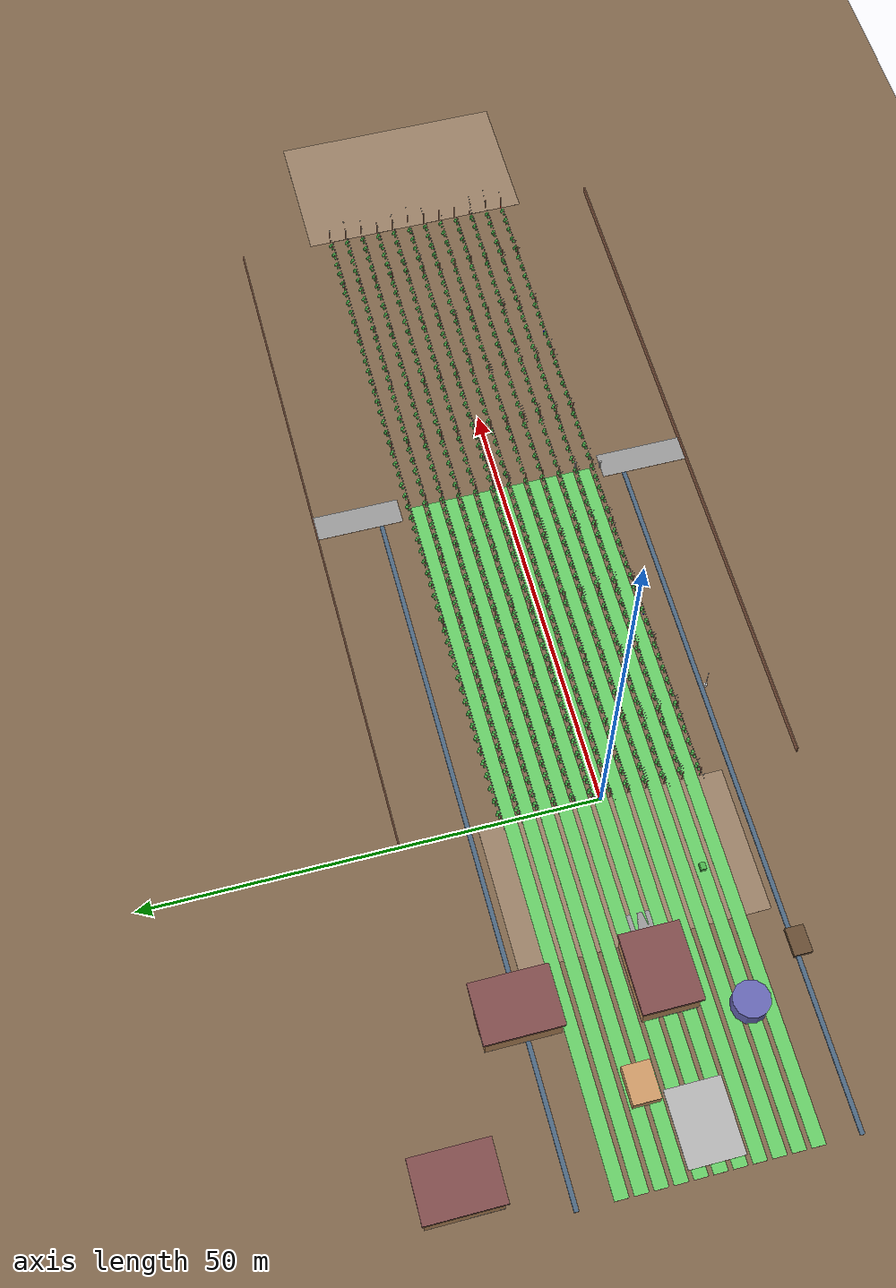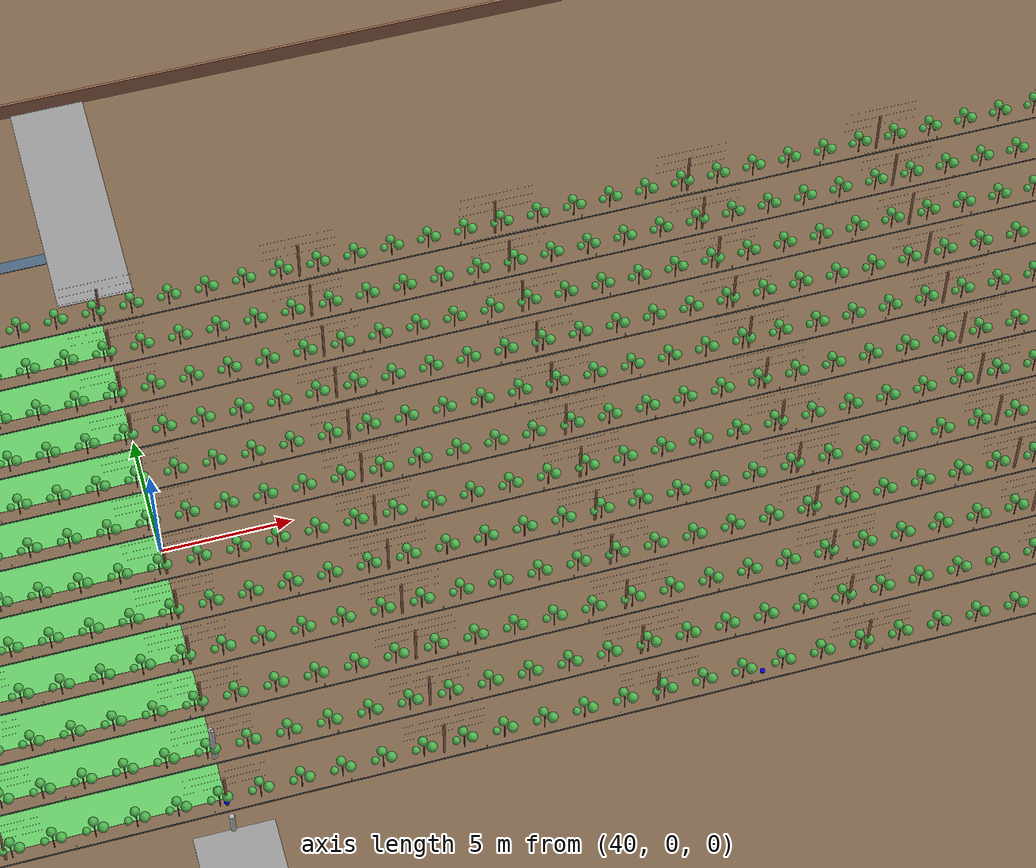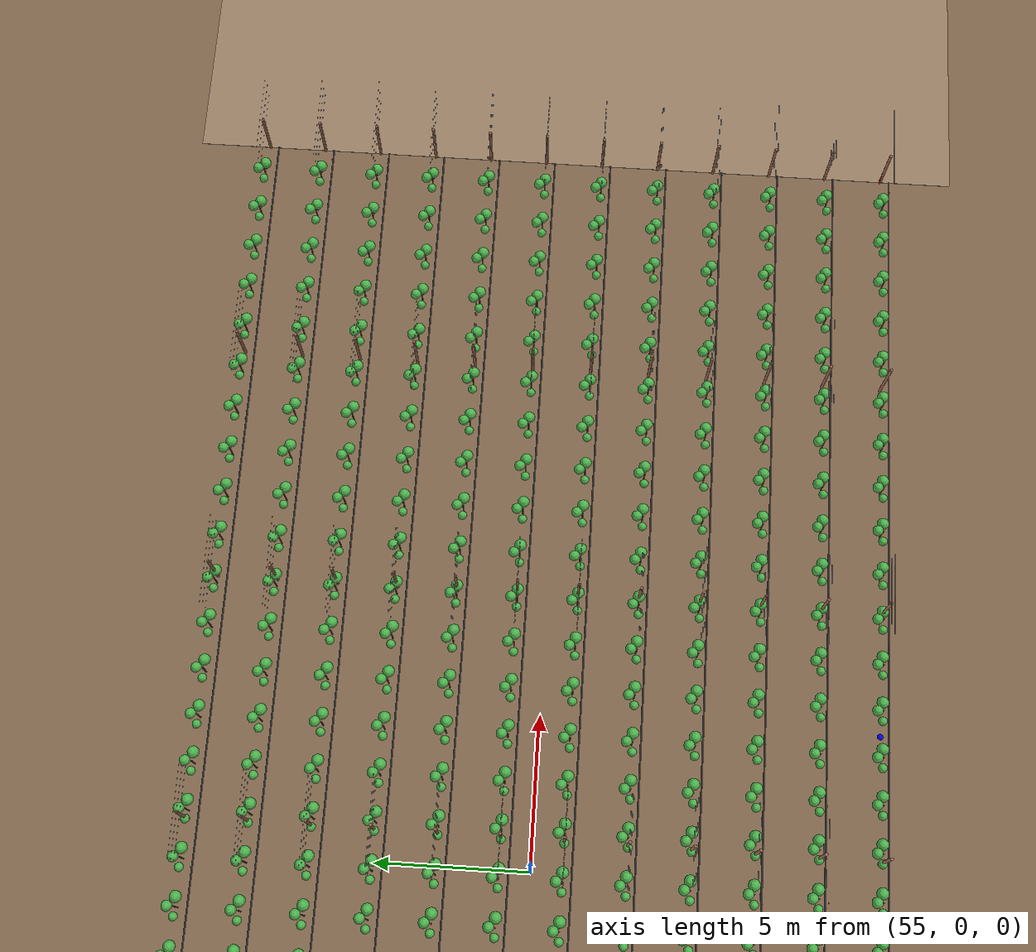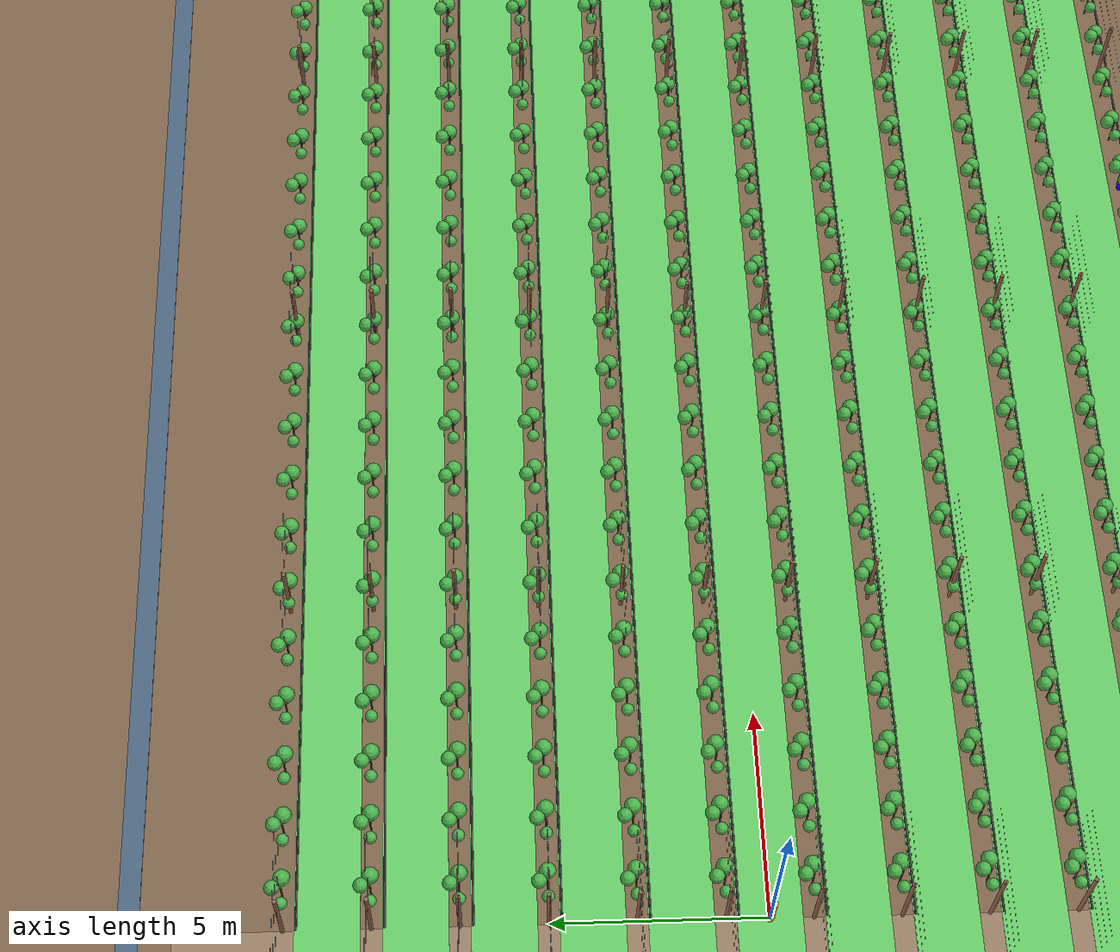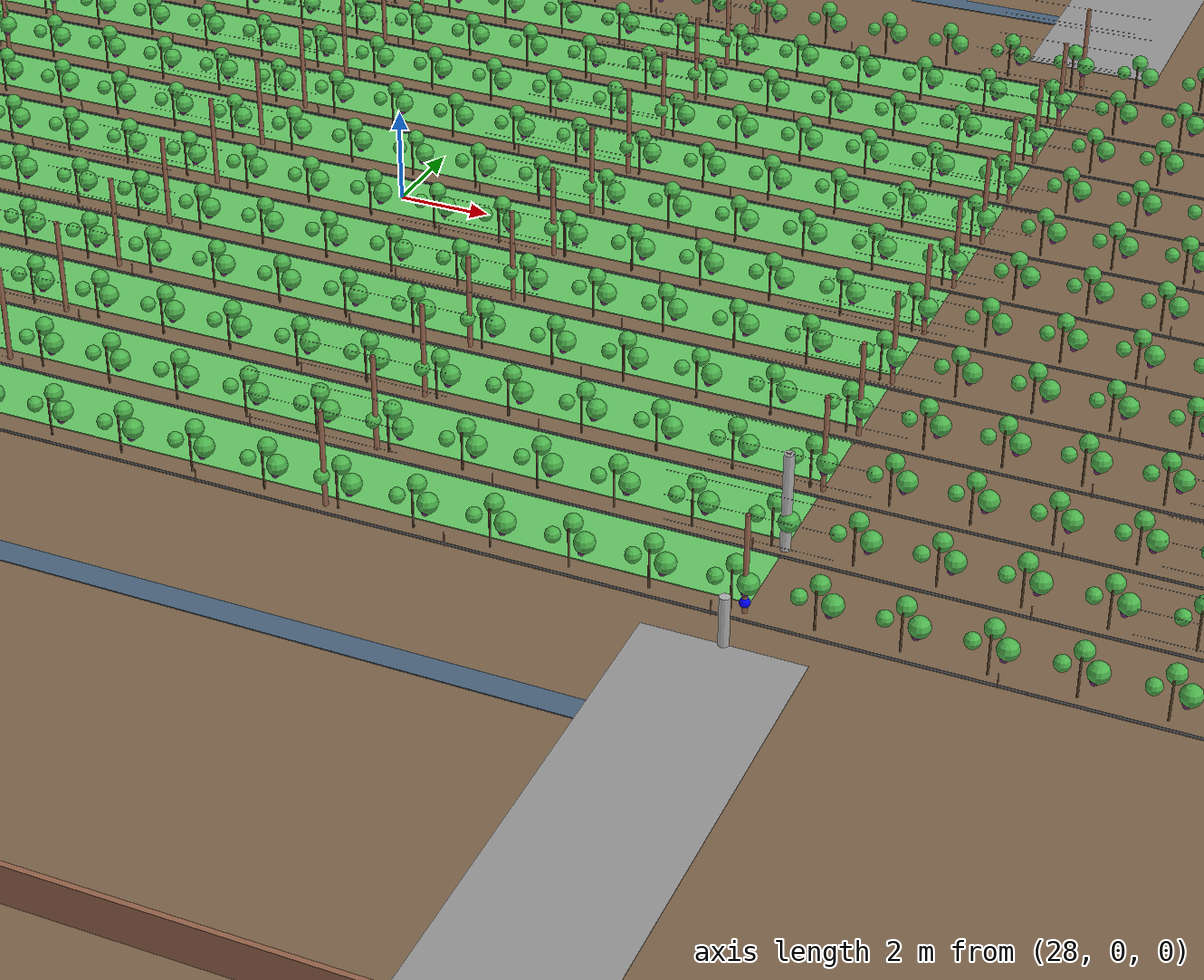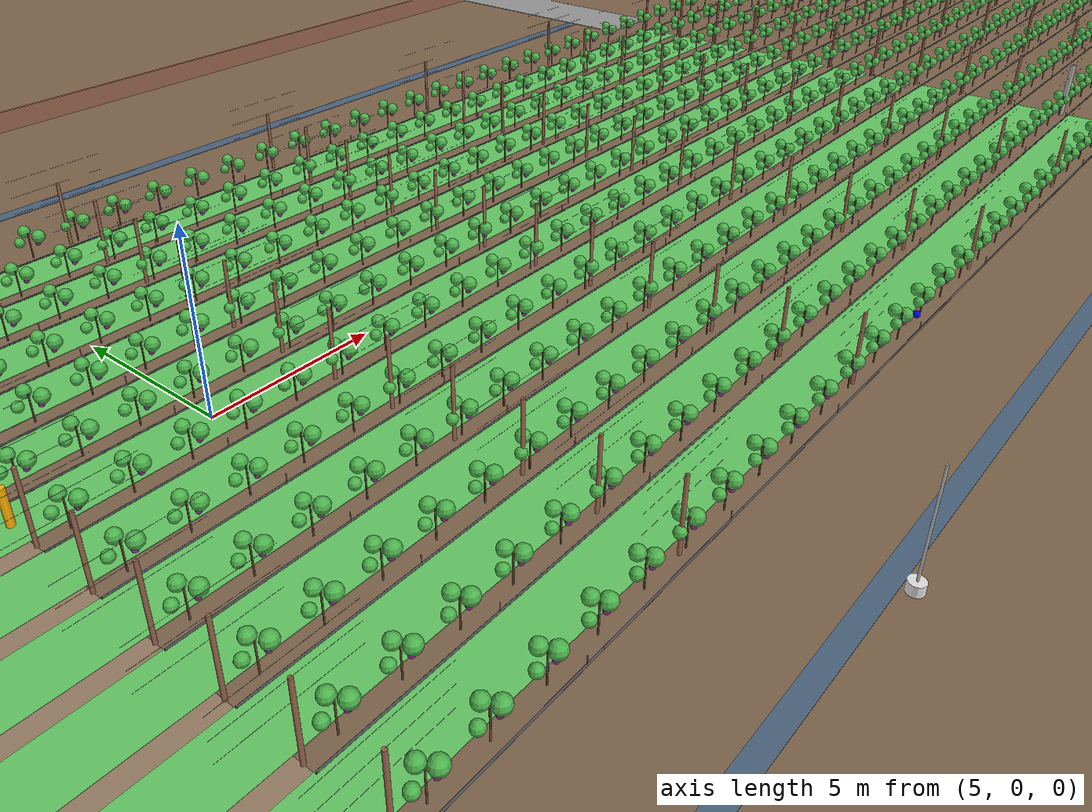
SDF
<?xml version="1.0" ?>
<sdf version="1.8">
  <world name="realistic_vineyard_world">
    <!-- Physics settings optimized for outdoor simulation -->
    <physics name="1ms" type="ignored">
      <max_step_size>0.001</max_step_size>
      <real_time_factor>1.0</real_time_factor>
    </physics>

    <!-- Required system plugins -->
    <plugin filename="gz-sim-physics-system" name="gz::sim::systems::Physics">
    </plugin>

    <plugin filename="gz-sim-sensors-system" name="gz::sim::systems::Sensors">
      <render_engine>ogre2</render_engine>
    </plugin>

    <plugin filename="gz-sim-scene-broadcaster-system" name="gz::sim::systems::SceneBroadcaster">
    </plugin>

    <plugin filename="gz-sim-user-commands-system" name="gz::sim::systems::UserCommands">
    </plugin>

    <plugin filename="gz-sim-imu-system" name="gz::sim::systems::Imu">
    </plugin>

    <!-- Wind system for realistic environmental effects -->
    <plugin filename="gz-sim-wind-effects-system" name="gz::sim::systems::WindEffects">
      <horizontal>
        <magnitude>
          <time_for_rise>10</time_for_rise>
          <sin>
            <amplitude_percent>0.05</amplitude_percent>
            <period>60</period>
          </sin>
        </magnitude>
        <direction>
          <time_for_rise>30</time_for_rise>
          <sin>
            <amplitude>5</amplitude>
            <period>20</period>
          </sin>
        </direction>
      </horizontal>
      <vertical>
        <noise type="gaussian">
          <mean>0</mean>
          <stddev>0.0002</stddev>
        </noise>
      </vertical>
    </plugin>

    <!-- Lighting setup for vineyard environment -->
    <light type="directional" name="sun">
      <cast_shadows>true</cast_shadows>
      <pose>0 0 10 0 0 0</pose>
      <diffuse>0.8 0.8 0.8 1</diffuse>
      <specular>0.5 0.5 0.5 1</specular>
      <direction>-0.5 0.1 -0.9</direction>
    </light>

    <!-- Additional ambient lighting -->
    <light type="directional" name="ambient_light">
      <cast_shadows>false</cast_shadows>
      <pose>0 0 10 0 0 0</pose>
      <diffuse>0.2 0.2 0.3 1</diffuse>
      <specular>0.1 0.1 0.1 1</specular>
      <direction>0 0 -1</direction>
    </light>

    <!-- Spot lights for key areas -->
    <light type="spot" name="vineyard_spotlight_1">
      <pose>0 -10 8 0 1.2 0</pose>
      <diffuse>0.6 0.6 0.4 1</diffuse>
      <specular>0.3 0.3 0.2 1</specular>
      <direction>0 0 -1</direction>
      <spot>
        <inner_angle>0.6</inner_angle>
        <outer_angle>1.0</outer_angle>
        <falloff>1</falloff>
      </spot>
      <cast_shadows>true</cast_shadows>
    </light>

    <light type="spot" name="vineyard_spotlight_2">
      <pose>50 0 8 0 1.2 0</pose>
      <diffuse>0.6 0.6 0.4 1</diffuse>
      <specular>0.3 0.3 0.2 1</specular>
      <direction>0 0 -1</direction>
      <spot>
        <inner_angle>0.6</inner_angle>
        <outer_angle>1.0</outer_angle>
        <falloff>1</falloff>
      </spot>
      <cast_shadows>true</cast_shadows>
    </light>

    <!-- Vineyard terrain with realistic features -->
    <model name="vineyard_terrain">
      <static>true</static>
      <link name="terrain_link">
        <!-- Main ground -->
        <collision name="ground_collision">
          <geometry>
            <plane>
              <normal>0 0 1</normal>
              <size>200 120</size>
            </plane>
          </geometry>
          <surface>
            <friction>
              <ode>
                <mu>0.8</mu>
                <mu2>0.7</mu2>
              </ode>
            </friction>
          </surface>
        </collision>
        <visual name="ground_visual">
          <geometry>
            <plane>
              <normal>0 0 1</normal>
              <size>200 120</size>
            </plane>
          </geometry>
          <material>
            <ambient>0.4 0.3 0.2 1</ambient>
            <diffuse>0.5 0.4 0.3 1</diffuse>
            <specular>0.1 0.1 0.1 1</specular>
          </material>
        </visual>

        <visual name="grass_strip_1">
          <pose>0 -10.0 0.01 0 0 0</pose>
          <geometry>
            <box>
              <size>80.0 1.5 0.02</size>
            </box>
          </geometry>
          <material>
            <ambient>0.3 0.6 0.3 1</ambient>
            <diffuse>0.4 0.8 0.4 1</diffuse>
          </material>
        </visual>
        <visual name="grass_strip_2">
          <pose>0 -8.0 0.01 0 0 0</pose>
          <geometry>
            <box>
              <size>80.0 1.5 0.02</size>
            </box>
          </geometry>
          <material>
            <ambient>0.3 0.6 0.3 1</ambient>
            <diffuse>0.4 0.8 0.4 1</diffuse>
          </material>
        </visual>
        <visual name="grass_strip_3">
          <pose>0 -6.0 0.01 0 0 0</pose>
          <geometry>
            <box>
              <size>80.0 1.5 0.02</size>
            </box>
          </geometry>
          <material>
            <ambient>0.3 0.6 0.3 1</ambient>
            <diffuse>0.4 0.8 0.4 1</diffuse>
          </material>
        </visual>
        <visual name="grass_strip_4">
          <pose>0 -4.0 0.01 0 0 0</pose>
          <geometry>
            <box>
              <size>80.0 1.5 0.02</size>
            </box>
          </geometry>
          <material>
            <ambient>0.3 0.6 0.3 1</ambient>
            <diffuse>0.4 0.8 0.4 1</diffuse>
          </material>
        </visual>
        <visual name="grass_strip_5">
          <pose>0 -2.0 0.01 0 0 0</pose>
          <geometry>
            <box>
              <size>80.0 1.5 0.02</size>
            </box>
          </geometry>
          <material>
            <ambient>0.3 0.6 0.3 1</ambient>
            <diffuse>0.4 0.8 0.4 1</diffuse>
          </material>
        </visual>
        <visual name="grass_strip_6">
          <pose>0 0.0 0.01 0 0 0</pose>
          <geometry>
            <box>
              <size>80.0 1.5 0.02</size>
            </box>
          </geometry>
          <material>
            <ambient>0.3 0.6 0.3 1</ambient>
            <diffuse>0.4 0.8 0.4 1</diffuse>
          </material>
        </visual>
        <visual name="grass_strip_7">
          <pose>0 2.0 0.01 0 0 0</pose>
          <geometry>
            <box>
              <size>80.0 1.5 0.02</size>
            </box>
          </geometry>
          <material>
            <ambient>0.3 0.6 0.3 1</ambient>
            <diffuse>0.4 0.8 0.4 1</diffuse>
          </material>
        </visual>
        <visual name="grass_strip_8">
          <pose>0 4.0 0.01 0 0 0</pose>
          <geometry>
            <box>
              <size>80.0 1.5 0.02</size>
            </box>
          </geometry>
          <material>
            <ambient>0.3 0.6 0.3 1</ambient>
            <diffuse>0.4 0.8 0.4 1</diffuse>
          </material>
        </visual>
        <visual name="grass_strip_9">
          <pose>0 6.0 0.01 0 0 0</pose>
          <geometry>
            <box>
              <size>80.0 1.5 0.02</size>
            </box>
          </geometry>
          <material>
            <ambient>0.3 0.6 0.3 1</ambient>
            <diffuse>0.4 0.8 0.4 1</diffuse>
          </material>
        </visual>
        <visual name="grass_strip_10">
          <pose>0 8.0 0.01 0 0 0</pose>
          <geometry>
            <box>
              <size>80.0 1.5 0.02</size>
            </box>
          </geometry>
          <material>
            <ambient>0.3 0.6 0.3 1</ambient>
            <diffuse>0.4 0.8 0.4 1</diffuse>
          </material>
        </visual>
        <visual name="grass_strip_11">
          <pose>0 10.0 0.01 0 0 0</pose>
          <geometry>
            <box>
              <size>80.0 1.5 0.02</size>
            </box>
          </geometry>
          <material>
            <ambient>0.3 0.6 0.3 1</ambient>
            <diffuse>0.4 0.8 0.4 1</diffuse>
          </material>
        </visual>

        <!-- Headland areas at row ends -->
        <visual name="headland_west">
          <pose>-8.0 0 0.005 0 0 0</pose>
          <geometry>
            <box>
              <size>16.0 27.0 0.01</size>
            </box>
          </geometry>
          <material>
            <ambient>0.5 0.4 0.3 1</ambient>
            <diffuse>0.6 0.5 0.4 1</diffuse>
          </material>
        </visual>

        <visual name="headland_east">
          <pose>88.0 0 0.005 0 0 0</pose>
          <geometry>
            <box>
              <size>16.0 27.0 0.01</size>
            </box>
          </geometry>
          <material>
            <ambient>0.5 0.4 0.3 1</ambient>
            <diffuse>0.6 0.5 0.4 1</diffuse>
          </material>
        </visual>

        <!-- Access roads -->
        <visual name="access_road_main">
          <pose>-18.0 0 0.01 0 0 0</pose>
          <geometry>
            <box>
              <size>10 3 0.02</size>
            </box>
          </geometry>
          <material>
            <ambient>0.4 0.4 0.4 1</ambient>
            <diffuse>0.6 0.6 0.6 1</diffuse>
          </material>
        </visual>

        <visual name="access_road_north">
          <pose>40.0 -17.0 0.01 0 0 1.57</pose>
          <geometry>
            <box>
              <size>10 3 0.02</size>
            </box>
          </geometry>
          <material>
            <ambient>0.4 0.4 0.4 1</ambient>
            <diffuse>0.6 0.6 0.6 1</diffuse>
          </material>
        </visual>

        <visual name="access_road_south">
          <pose>40.0 17.0 0.01 0 0 1.57</pose>
          <geometry>
            <box>
              <size>10 3 0.02</size>
            </box>
          </geometry>
          <material>
            <ambient>0.4 0.4 0.4 1</ambient>
            <diffuse>0.6 0.6 0.6 1</diffuse>
          </material>
        </visual>

        <!-- Drainage ditches -->
        <visual name="drainage_north">
          <pose>0 -14.5 -0.1 0 0 0</pose>
          <geometry>
            <box>
              <size>80.0 0.5 0.2</size>
            </box>
          </geometry>
          <material>
            <ambient>0.2 0.3 0.4 1</ambient>
            <diffuse>0.3 0.4 0.5 1</diffuse>
          </material>
        </visual>

        <visual name="drainage_south">
          <pose>0 14.5 -0.1 0 0 0</pose>
          <geometry>
            <box>
              <size>80.0 0.5 0.2</size>
            </box>
          </geometry>
          <material>
            <ambient>0.2 0.3 0.4 1</ambient>
            <diffuse>0.3 0.4 0.5 1</diffuse>
          </material>
        </visual>
      </link>
    </model>

    <!-- Generated Vineyard Rows -->
    <!-- Vineyard Row 1 -->
    <model name="vineyard_row_1">
      <static>true</static>
      <pose>0 -11.0 0 0 0 0</pose>

      <include>
        <uri>model://home/sam/vinmo/src/vineyard_mower_gazebo/models/vineyard_post</uri>
        <pose>0.0 0 1.0 0 0 0</pose>
        <name>post_1_1</name>
      </include>

      <include>
        <uri>model://home/sam/vinmo/src/vineyard_mower_gazebo/models/vineyard_post</uri>
        <pose>8.0 0 1.0 0 0 0</pose>
        <name>post_1_2</name>
      </include>

      <include>
        <uri>model://home/sam/vinmo/src/vineyard_mower_gazebo/models/vineyard_post</uri>
        <pose>16.0 0 1.0 0 0 0</pose>
        <name>post_1_3</name>
      </include>

      <include>
        <uri>model://home/sam/vinmo/src/vineyard_mower_gazebo/models/vineyard_post</uri>
        <pose>24.0 0 1.0 0 0 0</pose>
        <name>post_1_4</name>
      </include>

      <include>
        <uri>model://home/sam/vinmo/src/vineyard_mower_gazebo/models/vineyard_post</uri>
        <pose>32.0 0 1.0 0 0 0</pose>
        <name>post_1_5</name>
      </include>

      <include>
        <uri>model://home/sam/vinmo/src/vineyard_mower_gazebo/models/vineyard_post</uri>
        <pose>40.0 0 1.0 0 0 0</pose>
        <name>post_1_6</name>
      </include>

      <include>
        <uri>model://home/sam/vinmo/src/vineyard_mower_gazebo/models/vineyard_post</uri>
        <pose>48.0 0 1.0 0 0 0</pose>
        <name>post_1_7</name>
      </include>

      <include>
        <uri>model://home/sam/vinmo/src/vineyard_mower_gazebo/models/vineyard_post</uri>
        <pose>56.0 0 1.0 0 0 0</pose>
        <name>post_1_8</name>
      </include>

      <include>
        <uri>model://home/sam/vinmo/src/vineyard_mower_gazebo/models/vineyard_post</uri>
        <pose>64.0 0 1.0 0 0 0</pose>
        <name>post_1_9</name>
      </include>

      <include>
        <uri>model://home/sam/vinmo/src/vineyard_mower_gazebo/models/vineyard_post</uri>
        <pose>72.0 0 1.0 0 0 0</pose>
        <name>post_1_10</name>
      </include>

      <include>
        <uri>model://home/sam/vinmo/src/vineyard_mower_gazebo/models/vineyard_post</uri>
        <pose>80.0 0 1.0 0 0 0</pose>
        <name>post_1_11</name>
      </include>

      <include>
        <uri>model://home/sam/vinmo/src/vineyard_mower_gazebo/models/vine_plant</uri>
        <pose>0.75 0 0 0 0 0</pose>
        <name>vine_1_1</name>
      </include>

      <include>
        <uri>model://home/sam/vinmo/src/vineyard_mower_gazebo/models/vine_plant</uri>
        <pose>2.25 0 0 0 0 0</pose>
        <name>vine_1_2</name>
      </include>

      <include>
        <uri>model://home/sam/vinmo/src/vineyard_mower_gazebo/models/vine_plant</uri>
        <pose>3.75 0 0 0 0 0</pose>
        <name>vine_1_3</name>
      </include>

      <include>
        <uri>model://home/sam/vinmo/src/vineyard_mower_gazebo/models/vine_plant</uri>
        <pose>5.25 0 0 0 0 0</pose>
        <name>vine_1_4</name>
      </include>

      <include>
        <uri>model://home/sam/vinmo/src/vineyard_mower_gazebo/models/vine_plant</uri>
        <pose>6.75 0 0 0 0 0</pose>
        <name>vine_1_5</name>
      </include>

      <include>
        <uri>model://home/sam/vinmo/src/vineyard_mower_gazebo/models/vine_plant</uri>
        <pose>8.25 0 0 0 0 0</pose>
        <name>vine_1_6</name>
      </include>

      <include>
        <uri>model://home/sam/vinmo/src/vineyard_mower_gazebo/models/vine_plant</uri>
        <pose>9.75 0 0 0 0 0</pose>
        <name>vine_1_7</name>
      </include>

      <include>
        <uri>model://home/sam/vinmo/src/vineyard_mower_gazebo/models/vine_plant</uri>
        <pose>11.25 0 0 0 0 0</pose>
        <name>vine_1_8</name>
      </include>

      <include>
        <uri>model://home/sam/vinmo/src/vineyard_mower_gazebo/models/vine_plant</uri>
        <pose>12.75 0 0 0 0 0</pose>
        <name>vine_1_9</name>
      </include>

      <include>
        <uri>model://home/sam/vinmo/src/vineyard_mower_gazebo/models/vine_plant</uri>
        <pose>14.25 0 0 0 0 0</pose>
        <name>vine_1_10</name>
      </include>

      <include>
        <uri>model://home/sam/vinmo/src/vineyard_mower_gazebo/models/vine_plant</uri>
        <pose>15.75 0 0 0 0 0</pose>
        <name>vine_1_11</name>
      </include>

      <include>
        <uri>model://home/sam/vinmo/src/vineyard_mower_gazebo/models/vine_plant</uri>
        <pose>17.25 0 0 0 0 0</pose>
        <name>vine_1_12</name>
      </include>

      <include>
        <uri>model://home/sam/vinmo/src/vineyard_mower_gazebo/models/vine_plant</uri>
        <pose>18.75 0 0 0 0 0</pose>
        <name>vine_1_13</name>
      </include>

      <include>
        <uri>model://home/sam/vinmo/src/vineyard_mower_gazebo/models/vine_plant</uri>
        <pose>20.25 0 0 0 0 0</pose>
        <name>vine_1_14</name>
      </include>

      <include>
        <uri>model://home/sam/vinmo/src/vineyard_mower_gazebo/models/vine_plant</uri>
        <pose>21.75 0 0 0 0 0</pose>
        <name>vine_1_15</name>
      </include>

      <include>
        <uri>model://home/sam/vinmo/src/vineyard_mower_gazebo/models/vine_plant</uri>
        <pose>23.25 0 0 0 0 0</pose>
        <name>vine_1_16</name>
      </include>

      <include>
        <uri>model://home/sam/vinmo/src/vineyard_mower_gazebo/models/vine_plant</uri>
        <pose>24.75 0 0 0 0 0</pose>
        <name>vine_1_17</name>
      </include>

      <include>
        <uri>model://home/sam/vinmo/src/vineyard_mower_gazebo/models/vine_plant</uri>
        <pose>26.25 0 0 0 0 0</pose>
        <name>vine_1_18</name>
      </include>

      <include>
        <uri>model://home/sam/vinmo/src/vineyard_mower_gazebo/models/vine_plant</uri>
        <pose>27.75 0 0 0 0 0</pose>
        <name>vine_1_19</name>
      </include>

      <include>
        <uri>model://home/sam/vinmo/src/vineyard_mower_gazebo/models/vine_plant</uri>
        <pose>29.25 0 0 0 0 0</pose>
        <name>vine_1_20</name>
      </include>

      <include>
        <uri>model://home/sam/vinmo/src/vineyard_mower_gazebo/models/vine_plant</uri>
        <pose>30.75 0 0 0 0 0</pose>
        <name>vine_1_21</name>
      </include>

      <include>
        <uri>model://home/sam/vinmo/src/vineyard_mower_gazebo/models/vine_plant</uri>
        <pose>32.25 0 0 0 0 0</pose>
        <name>vine_1_22</name>
      </include>

      <include>
        <uri>model://home/sam/vinmo/src/vineyard_mower_gazebo/models/vine_plant</uri>
        <pose>33.75 0 0 0 0 0</pose>
        <name>vine_1_23</name>
      </include>

      <include>
        <uri>model://home/sam/vinmo/src/vineyard_mower_gazebo/models/vine_plant</uri>
        <pose>35.25 0 0 0 0 0</pose>
        <name>vine_1_24</name>
      </include>

      <include>
        <uri>model://home/sam/vinmo/src/vineyard_mower_gazebo/models/vine_plant</uri>
        <pose>36.75 0 0 0 0 0</pose>
        <name>vine_1_25</name>
      </include>

      <include>
        <uri>model://home/sam/vinmo/src/vineyard_mower_gazebo/models/vine_plant</uri>
        <pose>38.25 0 0 0 0 0</pose>
        <name>vine_1_26</name>
      </include>

      <include>
        <uri>model://home/sam/vinmo/src/vineyard_mower_gazebo/models/vine_plant</uri>
        <pose>39.75 0 0 0 0 0</pose>
        <name>vine_1_27</name>
      </include>

      <include>
        <uri>model://home/sam/vinmo/src/vineyard_mower_gazebo/models/vine_plant</uri>
        <pose>41.25 0 0 0 0 0</pose>
        <name>vine_1_28</name>
      </include>

      <include>
        <uri>model://home/sam/vinmo/src/vineyard_mower_gazebo/models/vine_plant</uri>
        <pose>42.75 0 0 0 0 0</pose>
        <name>vine_1_29</name>
      </include>

      <include>
        <uri>model://home/sam/vinmo/src/vineyard_mower_gazebo/models/vine_plant</uri>
        <pose>44.25 0 0 0 0 0</pose>
        <name>vine_1_30</name>
      </include>

      <include>
        <uri>model://home/sam/vinmo/src/vineyard_mower_gazebo/models/vine_plant</uri>
        <pose>45.75 0 0 0 0 0</pose>
        <name>vine_1_31</name>
      </include>

      <include>
        <uri>model://home/sam/vinmo/src/vineyard_mower_gazebo/models/vine_plant</uri>
        <pose>47.25 0 0 0 0 0</pose>
        <name>vine_1_32</name>
      </include>

      <include>
        <uri>model://home/sam/vinmo/src/vineyard_mower_gazebo/models/vine_plant</uri>
        <pose>48.75 0 0 0 0 0</pose>
        <name>vine_1_33</name>
      </include>

      <include>
        <uri>model://home/sam/vinmo/src/vineyard_mower_gazebo/models/vine_plant</uri>
        <pose>50.25 0 0 0 0 0</pose>
        <name>vine_1_34</name>
      </include>

      <include>
        <uri>model://home/sam/vinmo/src/vineyard_mower_gazebo/models/vine_plant</uri>
        <pose>51.75 0 0 0 0 0</pose>
        <name>vine_1_35</name>
      </include>

      <include>
        <uri>model://home/sam/vinmo/src/vineyard_mower_gazebo/models/vine_plant</uri>
        <pose>53.25 0 0 0 0 0</pose>
        <name>vine_1_36</name>
      </include>

      <include>
        <uri>model://home/sam/vinmo/src/vineyard_mower_gazebo/models/vine_plant</uri>
        <pose>54.75 0 0 0 0 0</pose>
        <name>vine_1_37</name>
      </include>

      <include>
        <uri>model://home/sam/vinmo/src/vineyard_mower_gazebo/models/vine_plant</uri>
        <pose>56.25 0 0 0 0 0</pose>
        <name>vine_1_38</name>
      </include>

      <include>
        <uri>model://home/sam/vinmo/src/vineyard_mower_gazebo/models/vine_plant</uri>
        <pose>57.75 0 0 0 0 0</pose>
        <name>vine_1_39</name>
      </include>

      <include>
        <uri>model://home/sam/vinmo/src/vineyard_mower_gazebo/models/vine_plant</uri>
        <pose>59.25 0 0 0 0 0</pose>
        <name>vine_1_40</name>
      </include>

      <include>
        <uri>model://home/sam/vinmo/src/vineyard_mower_gazebo/models/vine_plant</uri>
        <pose>60.75 0 0 0 0 0</pose>
        <name>vine_1_41</name>
      </include>

      <include>
        <uri>model://home/sam/vinmo/src/vineyard_mower_gazebo/models/vine_plant</uri>
        <pose>62.25 0 0 0 0 0</pose>
        <name>vine_1_42</name>
      </include>

      <include>
        <uri>model://home/sam/vinmo/src/vineyard_mower_gazebo/models/vine_plant</uri>
        <pose>63.75 0 0 0 0 0</pose>
        <name>vine_1_43</name>
      </include>

      <include>
        <uri>model://home/sam/vinmo/src/vineyard_mower_gazebo/models/vine_plant</uri>
        <pose>65.25 0 0 0 0 0</pose>
        <name>vine_1_44</name>
      </include>

      <include>
        <uri>model://home/sam/vinmo/src/vineyard_mower_gazebo/models/vine_plant</uri>
        <pose>66.75 0 0 0 0 0</pose>
        <name>vine_1_45</name>
      </include>

      <include>
        <uri>model://home/sam/vinmo/src/vineyard_mower_gazebo/models/vine_plant</uri>
        <pose>68.25 0 0 0 0 0</pose>
        <name>vine_1_46</name>
      </include>

      <include>
        <uri>model://home/sam/vinmo/src/vineyard_mower_gazebo/models/vine_plant</uri>
        <pose>69.75 0 0 0 0 0</pose>
        <name>vine_1_47</name>
      </include>

      <include>
        <uri>model://home/sam/vinmo/src/vineyard_mower_gazebo/models/vine_plant</uri>
        <pose>71.25 0 0 0 0 0</pose>
        <name>vine_1_48</name>
      </include>

      <include>
        <uri>model://home/sam/vinmo/src/vineyard_mower_gazebo/models/vine_plant</uri>
        <pose>72.75 0 0 0 0 0</pose>
        <name>vine_1_49</name>
      </include>

      <include>
        <uri>model://home/sam/vinmo/src/vineyard_mower_gazebo/models/vine_plant</uri>
        <pose>74.25 0 0 0 0 0</pose>
        <name>vine_1_50</name>
      </include>

      <include>
        <uri>model://home/sam/vinmo/src/vineyard_mower_gazebo/models/vine_plant</uri>
        <pose>75.75 0 0 0 0 0</pose>
        <name>vine_1_51</name>
      </include>

      <include>
        <uri>model://home/sam/vinmo/src/vineyard_mower_gazebo/models/vine_plant</uri>
        <pose>77.25 0 0 0 0 0</pose>
        <name>vine_1_52</name>
      </include>

      <include>
        <uri>model://home/sam/vinmo/src/vineyard_mower_gazebo/models/vine_plant</uri>
        <pose>78.75 0 0 0 0 0</pose>
        <name>vine_1_53</name>
      </include>

      <include>
        <uri>model://home/sam/vinmo/src/vineyard_mower_gazebo/models/irrigation_pipe</uri>
        <pose>2.5 -0.3 0 0 0 0</pose>
        <name>irrigation_1_1</name>
      </include>

      <include>
        <uri>model://home/sam/vinmo/src/vineyard_mower_gazebo/models/irrigation_pipe</uri>
        <pose>7.5 -0.3 0 0 0 0</pose>
        <name>irrigation_1_2</name>
      </include>

      <include>
        <uri>model://home/sam/vinmo/src/vineyard_mower_gazebo/models/irrigation_pipe</uri>
        <pose>12.5 -0.3 0 0 0 0</pose>
        <name>irrigation_1_3</name>
      </include>

      <include>
        <uri>model://home/sam/vinmo/src/vineyard_mower_gazebo/models/irrigation_pipe</uri>
        <pose>17.5 -0.3 0 0 0 0</pose>
        <name>irrigation_1_4</name>
      </include>

      <include>
        <uri>model://home/sam/vinmo/src/vineyard_mower_gazebo/models/irrigation_pipe</uri>
        <pose>22.5 -0.3 0 0 0 0</pose>
        <name>irrigation_1_5</name>
      </include>

      <include>
        <uri>model://home/sam/vinmo/src/vineyard_mower_gazebo/models/irrigation_pipe</uri>
        <pose>27.5 -0.3 0 0 0 0</pose>
        <name>irrigation_1_6</name>
      </include>

      <include>
        <uri>model://home/sam/vinmo/src/vineyard_mower_gazebo/models/irrigation_pipe</uri>
        <pose>32.5 -0.3 0 0 0 0</pose>
        <name>irrigation_1_7</name>
      </include>

      <include>
        <uri>model://home/sam/vinmo/src/vineyard_mower_gazebo/models/irrigation_pipe</uri>
        <pose>37.5 -0.3 0 0 0 0</pose>
        <name>irrigation_1_8</name>
      </include>

      <include>
        <uri>model://home/sam/vinmo/src/vineyard_mower_gazebo/models/irrigation_pipe</uri>
        <pose>42.5 -0.3 0 0 0 0</pose>
        <name>irrigation_1_9</name>
      </include>

      <include>
        <uri>model://home/sam/vinmo/src/vineyard_mower_gazebo/models/irrigation_pipe</uri>
        <pose>47.5 -0.3 0 0 0 0</pose>
        <name>irrigation_1_10</name>
      </include>

      <include>
        <uri>model://home/sam/vinmo/src/vineyard_mower_gazebo/models/irrigation_pipe</uri>
        <pose>52.5 -0.3 0 0 0 0</pose>
        <name>irrigation_1_11</name>
      </include>

      <include>
        <uri>model://home/sam/vinmo/src/vineyard_mower_gazebo/models/irrigation_pipe</uri>
        <pose>57.5 -0.3 0 0 0 0</pose>
        <name>irrigation_1_12</name>
      </include>

      <include>
        <uri>model://home/sam/vinmo/src/vineyard_mower_gazebo/models/irrigation_pipe</uri>
        <pose>62.5 -0.3 0 0 0 0</pose>
        <name>irrigation_1_13</name>
      </include>

      <include>
        <uri>model://home/sam/vinmo/src/vineyard_mower_gazebo/models/irrigation_pipe</uri>
        <pose>67.5 -0.3 0 0 0 0</pose>
        <name>irrigation_1_14</name>
      </include>

      <include>
        <uri>model://home/sam/vinmo/src/vineyard_mower_gazebo/models/irrigation_pipe</uri>
        <pose>72.5 -0.3 0 0 0 0</pose>
        <name>irrigation_1_15</name>
      </include>

      <include>
        <uri>model://home/sam/vinmo/src/vineyard_mower_gazebo/models/irrigation_pipe</uri>
        <pose>77.5 -0.3 0 0 0 0</pose>
        <name>irrigation_1_16</name>
      </include>

    </model>

    <!-- Vineyard Row 2 -->
    <model name="vineyard_row_2">
      <static>true</static>
      <pose>0 -9.0 0 0 0 0</pose>

      <include>
        <uri>model://home/sam/vinmo/src/vineyard_mower_gazebo/models/vineyard_post</uri>
        <pose>0.0 0 1.0 0 0 0</pose>
        <name>post_2_1</name>
      </include>

      <include>
        <uri>model://home/sam/vinmo/src/vineyard_mower_gazebo/models/vineyard_post</uri>
        <pose>8.0 0 1.0 0 0 0</pose>
        <name>post_2_2</name>
      </include>

      <include>
        <uri>model://home/sam/vinmo/src/vineyard_mower_gazebo/models/vineyard_post</uri>
        <pose>16.0 0 1.0 0 0 0</pose>
        <name>post_2_3</name>
      </include>

      <include>
        <uri>model://home/sam/vinmo/src/vineyard_mower_gazebo/models/vineyard_post</uri>
        <pose>24.0 0 1.0 0 0 0</pose>
        <name>post_2_4</name>
      </include>

      <include>
        <uri>model://home/sam/vinmo/src/vineyard_mower_gazebo/models/vineyard_post</uri>
        <pose>32.0 0 1.0 0 0 0</pose>
        <name>post_2_5</name>
      </include>

      <include>
        <uri>model://home/sam/vinmo/src/vineyard_mower_gazebo/models/vineyard_post</uri>
        <pose>40.0 0 1.0 0 0 0</pose>
        <name>post_2_6</name>
      </include>

      <include>
        <uri>model://home/sam/vinmo/src/vineyard_mower_gazebo/models/vineyard_post</uri>
        <pose>48.0 0 1.0 0 0 0</pose>
        <name>post_2_7</name>
      </include>

      <include>
        <uri>model://home/sam/vinmo/src/vineyard_mower_gazebo/models/vineyard_post</uri>
        <pose>56.0 0 1.0 0 0 0</pose>
        <name>post_2_8</name>
      </include>

      <include>
        <uri>model://home/sam/vinmo/src/vineyard_mower_gazebo/models/vineyard_post</uri>
        <pose>64.0 0 1.0 0 0 0</pose>
        <name>post_2_9</name>
      </include>

      <include>
        <uri>model://home/sam/vinmo/src/vineyard_mower_gazebo/models/vineyard_post</uri>
        <pose>72.0 0 1.0 0 0 0</pose>
        <name>post_2_10</name>
      </include>

      <include>
        <uri>model://home/sam/vinmo/src/vineyard_mower_gazebo/models/vineyard_post</uri>
        <pose>80.0 0 1.0 0 0 0</pose>
        <name>post_2_11</name>
      </include>

      <include>
        <uri>model://home/sam/vinmo/src/vineyard_mower_gazebo/models/vine_plant</uri>
        <pose>0.75 0 0 0 0 0</pose>
        <name>vine_2_1</name>
      </include>

      <include>
        <uri>model://home/sam/vinmo/src/vineyard_mower_gazebo/models/vine_plant</uri>
        <pose>2.25 0 0 0 0 0</pose>
        <name>vine_2_2</name>
      </include>

      <include>
        <uri>model://home/sam/vinmo/src/vineyard_mower_gazebo/models/vine_plant</uri>
        <pose>3.75 0 0 0 0 0</pose>
        <name>vine_2_3</name>
      </include>

      <include>
        <uri>model://home/sam/vinmo/src/vineyard_mower_gazebo/models/vine_plant</uri>
        <pose>5.25 0 0 0 0 0</pose>
        <name>vine_2_4</name>
      </include>

      <include>
        <uri>model://home/sam/vinmo/src/vineyard_mower_gazebo/models/vine_plant</uri>
        <pose>6.75 0 0 0 0 0</pose>
        <name>vine_2_5</name>
      </include>

      <include>
        <uri>model://home/sam/vinmo/src/vineyard_mower_gazebo/models/vine_plant</uri>
        <pose>8.25 0 0 0 0 0</pose>
        <name>vine_2_6</name>
      </include>

      <include>
        <uri>model://home/sam/vinmo/src/vineyard_mower_gazebo/models/vine_plant</uri>
        <pose>9.75 0 0 0 0 0</pose>
        <name>vine_2_7</name>
      </include>

      <include>
        <uri>model://home/sam/vinmo/src/vineyard_mower_gazebo/models/vine_plant</uri>
        <pose>11.25 0 0 0 0 0</pose>
        <name>vine_2_8</name>
      </include>

      <include>
        <uri>model://home/sam/vinmo/src/vineyard_mower_gazebo/models/vine_plant</uri>
        <pose>12.75 0 0 0 0 0</pose>
        <name>vine_2_9</name>
      </include>

      <include>
        <uri>model://home/sam/vinmo/src/vineyard_mower_gazebo/models/vine_plant</uri>
        <pose>14.25 0 0 0 0 0</pose>
        <name>vine_2_10</name>
      </include>

      <include>
        <uri>model://home/sam/vinmo/src/vineyard_mower_gazebo/models/vine_plant</uri>
        <pose>15.75 0 0 0 0 0</pose>
        <name>vine_2_11</name>
      </include>

      <include>
        <uri>model://home/sam/vinmo/src/vineyard_mower_gazebo/models/vine_plant</uri>
        <pose>17.25 0 0 0 0 0</pose>
        <name>vine_2_12</name>
      </include>

      <include>
        <uri>model://home/sam/vinmo/src/vineyard_mower_gazebo/models/vine_plant</uri>
        <pose>18.75 0 0 0 0 0</pose>
        <name>vine_2_13</name>
      </include>

      <include>
        <uri>model://home/sam/vinmo/src/vineyard_mower_gazebo/models/vine_plant</uri>
        <pose>20.25 0 0 0 0 0</pose>
        <name>vine_2_14</name>
      </include>

      <include>
        <uri>model://home/sam/vinmo/src/vineyard_mower_gazebo/models/vine_plant</uri>
        <pose>21.75 0 0 0 0 0</pose>
        <name>vine_2_15</name>
      </include>

      <include>
        <uri>model://home/sam/vinmo/src/vineyard_mower_gazebo/models/vine_plant</uri>
        <pose>23.25 0 0 0 0 0</pose>
        <name>vine_2_16</name>
      </include>

      <include>
        <uri>model://home/sam/vinmo/src/vineyard_mower_gazebo/models/vine_plant</uri>
        <pose>24.75 0 0 0 0 0</pose>
        <name>vine_2_17</name>
      </include>

      <include>
        <uri>model://home/sam/vinmo/src/vineyard_mower_gazebo/models/vine_plant</uri>
        <pose>26.25 0 0 0 0 0</pose>
        <name>vine_2_18</name>
      </include>

      <include>
        <uri>model://home/sam/vinmo/src/vineyard_mower_gazebo/models/vine_plant</uri>
        <pose>27.75 0 0 0 0 0</pose>
        <name>vine_2_19</name>
      </include>

      <include>
        <uri>model://home/sam/vinmo/src/vineyard_mower_gazebo/models/vine_plant</uri>
        <pose>29.25 0 0 0 0 0</pose>
        <name>vine_2_20</name>
      </include>

      <include>
        <uri>model://home/sam/vinmo/src/vineyard_mower_gazebo/models/vine_plant</uri>
        <pose>30.75 0 0 0 0 0</pose>
        <name>vine_2_21</name>
      </include>

      <include>
        <uri>model://home/sam/vinmo/src/vineyard_mower_gazebo/models/vine_plant</uri>
        <pose>32.25 0 0 0 0 0</pose>
        <name>vine_2_22</name>
      </include>

      <include>
        <uri>model://home/sam/vinmo/src/vineyard_mower_gazebo/models/vine_plant</uri>
        <pose>33.75 0 0 0 0 0</pose>
        <name>vine_2_23</name>
      </include>

      <include>
        <uri>model://home/sam/vinmo/src/vineyard_mower_gazebo/models/vine_plant</uri>
        <pose>35.25 0 0 0 0 0</pose>
        <name>vine_2_24</name>
      </include>

      <include>
        <uri>model://home/sam/vinmo/src/vineyard_mower_gazebo/models/vine_plant</uri>
        <pose>36.75 0 0 0 0 0</pose>
        <name>vine_2_25</name>
      </include>

      <include>
        <uri>model://home/sam/vinmo/src/vineyard_mower_gazebo/models/vine_plant</uri>
        <pose>38.25 0 0 0 0 0</pose>
        <name>vine_2_26</name>
      </include>

      <include>
        <uri>model://home/sam/vinmo/src/vineyard_mower_gazebo/models/vine_plant</uri>
        <pose>39.75 0 0 0 0 0</pose>
        <name>vine_2_27</name>
      </include>

      <include>
        <uri>model://home/sam/vinmo/src/vineyard_mower_gazebo/models/vine_plant</uri>
        <pose>41.25 0 0 0 0 0</pose>
        <name>vine_2_28</name>
      </include>

      <include>
        <uri>model://home/sam/vinmo/src/vineyard_mower_gazebo/models/vine_plant</uri>
        <pose>42.75 0 0 0 0 0</pose>
        <name>vine_2_29</name>
      </include>

      <include>
        <uri>model://home/sam/vinmo/src/vineyard_mower_gazebo/models/vine_plant</uri>
        <pose>44.25 0 0 0 0 0</pose>
        <name>vine_2_30</name>
      </include>

      <include>
        <uri>model://home/sam/vinmo/src/vineyard_mower_gazebo/models/vine_plant</uri>
        <pose>45.75 0 0 0 0 0</pose>
        <name>vine_2_31</name>
      </include>

      <include>
        <uri>model://home/sam/vinmo/src/vineyard_mower_gazebo/models/vine_plant</uri>
        <pose>47.25 0 0 0 0 0</pose>
        <name>vine_2_32</name>
      </include>

      <include>
        <uri>model://home/sam/vinmo/src/vineyard_mower_gazebo/models/vine_plant</uri>
        <pose>48.75 0 0 0 0 0</pose>
        <name>vine_2_33</name>
      </include>

      <include>
        <uri>model://home/sam/vinmo/src/vineyard_mower_gazebo/models/vine_plant</uri>
        <pose>50.25 0 0 0 0 0</pose>
        <name>vine_2_34</name>
      </include>

      <include>
        <uri>model://home/sam/vinmo/src/vineyard_mower_gazebo/models/vine_plant</uri>
        <pose>51.75 0 0 0 0 0</pose>
        <name>vine_2_35</name>
      </include>

      <include>
        <uri>model://home/sam/vinmo/src/vineyard_mower_gazebo/models/vine_plant</uri>
        <pose>53.25 0 0 0 0 0</pose>
        <name>vine_2_36</name>
      </include>

      <include>
        <uri>model://home/sam/vinmo/src/vineyard_mower_gazebo/models/vine_plant</uri>
        <pose>54.75 0 0 0 0 0</pose>
        <name>vine_2_37</name>
      </include>

      <include>
        <uri>model://home/sam/vinmo/src/vineyard_mower_gazebo/models/vine_plant</uri>
        <pose>56.25 0 0 0 0 0</pose>
        <name>vine_2_38</name>
      </include>

      <include>
        <uri>model://home/sam/vinmo/src/vineyard_mower_gazebo/models/vine_plant</uri>
        <pose>57.75 0 0 0 0 0</pose>
        <name>vine_2_39</name>
      </include>

      <include>
        <uri>model://home/sam/vinmo/src/vineyard_mower_gazebo/models/vine_plant</uri>
        <pose>59.25 0 0 0 0 0</pose>
        <name>vine_2_40</name>
      </include>

      <include>
        <uri>model://home/sam/vinmo/src/vineyard_mower_gazebo/models/vine_plant</uri>
        <pose>60.75 0 0 0 0 0</pose>
        <name>vine_2_41</name>
      </include>

      <include>
        <uri>model://home/sam/vinmo/src/vineyard_mower_gazebo/models/vine_plant</uri>
        <pose>62.25 0 0 0 0 0</pose>
        <name>vine_2_42</name>
      </include>

      <include>
        <uri>model://home/sam/vinmo/src/vineyard_mower_gazebo/models/vine_plant</uri>
        <pose>63.75 0 0 0 0 0</pose>
        <name>vine_2_43</name>
      </include>

      <include>
        <uri>model://home/sam/vinmo/src/vineyard_mower_gazebo/models/vine_plant</uri>
        <pose>65.25 0 0 0 0 0</pose>
        <name>vine_2_44</name>
      </include>

      <include>
        <uri>model://home/sam/vinmo/src/vineyard_mower_gazebo/models/vine_plant</uri>
        <pose>66.75 0 0 0 0 0</pose>
        <name>vine_2_45</name>
      </include>

      <include>
        <uri>model://home/sam/vinmo/src/vineyard_mower_gazebo/models/vine_plant</uri>
        <pose>68.25 0 0 0 0 0</pose>
        <name>vine_2_46</name>
      </include>

      <include>
        <uri>model://home/sam/vinmo/src/vineyard_mower_gazebo/models/vine_plant</uri>
        <pose>69.75 0 0 0 0 0</pose>
        <name>vine_2_47</name>
      </include>

      <include>
        <uri>model://home/sam/vinmo/src/vineyard_mower_gazebo/models/vine_plant</uri>
        <pose>71.25 0 0 0 0 0</pose>
        <name>vine_2_48</name>
      </include>

      <include>
        <uri>model://home/sam/vinmo/src/vineyard_mower_gazebo/models/vine_plant</uri>
        <pose>72.75 0 0 0 0 0</pose>
        <name>vine_2_49</name>
      </include>

      <include>
        <uri>model://home/sam/vinmo/src/vineyard_mower_gazebo/models/vine_plant</uri>
        <pose>74.25 0 0 0 0 0</pose>
        <name>vine_2_50</name>
      </include>

      <include>
        <uri>model://home/sam/vinmo/src/vineyard_mower_gazebo/models/vine_plant</uri>
        <pose>75.75 0 0 0 0 0</pose>
        <name>vine_2_51</name>
      </include>

      <include>
        <uri>model://home/sam/vinmo/src/vineyard_mower_gazebo/models/vine_plant</uri>
        <pose>77.25 0 0 0 0 0</pose>
        <name>vine_2_52</name>
      </include>

      <include>
        <uri>model://home/sam/vinmo/src/vineyard_mower_gazebo/models/vine_plant</uri>
        <pose>78.75 0 0 0 0 0</pose>
        <name>vine_2_53</name>
      </include>

      <include>
        <uri>model://home/sam/vinmo/src/vineyard_mower_gazebo/models/irrigation_pipe</uri>
        <pose>2.5 -0.3 0 0 0 0</pose>
        <name>irrigation_2_1</name>
      </include>

      <include>
        <uri>model://home/sam/vinmo/src/vineyard_mower_gazebo/models/irrigation_pipe</uri>
        <pose>7.5 -0.3 0 0 0 0</pose>
        <name>irrigation_2_2</name>
      </include>

      <include>
        <uri>model://home/sam/vinmo/src/vineyard_mower_gazebo/models/irrigation_pipe</uri>
        <pose>12.5 -0.3 0 0 0 0</pose>
        <name>irrigation_2_3</name>
      </include>

      <include>
        <uri>model://home/sam/vinmo/src/vineyard_mower_gazebo/models/irrigation_pipe</uri>
        <pose>17.5 -0.3 0 0 0 0</pose>
        <name>irrigation_2_4</name>
      </include>

      <include>
        <uri>model://home/sam/vinmo/src/vineyard_mower_gazebo/models/irrigation_pipe</uri>
        <pose>22.5 -0.3 0 0 0 0</pose>
        <name>irrigation_2_5</name>
      </include>

      <include>
        <uri>model://home/sam/vinmo/src/vineyard_mower_gazebo/models/irrigation_pipe</uri>
        <pose>27.5 -0.3 0 0 0 0</pose>
        <name>irrigation_2_6</name>
      </include>

      <include>
        <uri>model://home/sam/vinmo/src/vineyard_mower_gazebo/models/irrigation_pipe</uri>
        <pose>32.5 -0.3 0 0 0 0</pose>
        <name>irrigation_2_7</name>
      </include>

      <include>
        <uri>model://home/sam/vinmo/src/vineyard_mower_gazebo/models/irrigation_pipe</uri>
        <pose>37.5 -0.3 0 0 0 0</pose>
        <name>irrigation_2_8</name>
      </include>

      <include>
        <uri>model://home/sam/vinmo/src/vineyard_mower_gazebo/models/irrigation_pipe</uri>
        <pose>42.5 -0.3 0 0 0 0</pose>
        <name>irrigation_2_9</name>
      </include>

      <include>
        <uri>model://home/sam/vinmo/src/vineyard_mower_gazebo/models/irrigation_pipe</uri>
        <pose>47.5 -0.3 0 0 0 0</pose>
        <name>irrigation_2_10</name>
      </include>

      <include>
        <uri>model://home/sam/vinmo/src/vineyard_mower_gazebo/models/irrigation_pipe</uri>
        <pose>52.5 -0.3 0 0 0 0</pose>
        <name>irrigation_2_11</name>
      </include>

      <include>
        <uri>model://home/sam/vinmo/src/vineyard_mower_gazebo/models/irrigation_pipe</uri>
        <pose>57.5 -0.3 0 0 0 0</pose>
        <name>irrigation_2_12</name>
      </include>

      <include>
        <uri>model://home/sam/vinmo/src/vineyard_mower_gazebo/models/irrigation_pipe</uri>
        <pose>62.5 -0.3 0 0 0 0</pose>
        <name>irrigation_2_13</name>
      </include>

      <include>
        <uri>model://home/sam/vinmo/src/vineyard_mower_gazebo/models/irrigation_pipe</uri>
        <pose>67.5 -0.3 0 0 0 0</pose>
        <name>irrigation_2_14</name>
      </include>

      <include>
        <uri>model://home/sam/vinmo/src/vineyard_mower_gazebo/models/irrigation_pipe</uri>
        <pose>72.5 -0.3 0 0 0 0</pose>
        <name>irrigation_2_15</name>
      </include>

      <include>
        <uri>model://home/sam/vinmo/src/vineyard_mower_gazebo/models/irrigation_pipe</uri>
        <pose>77.5 -0.3 0 0 0 0</pose>
        <name>irrigation_2_16</name>
      </include>

    </model>

    <!-- Vineyard Row 3 -->
    <model name="vineyard_row_3">
      <static>true</static>
      <pose>0 -7.0 0 0 0 0</pose>

      <include>
        <uri>model://home/sam/vinmo/src/vineyard_mower_gazebo/models/vineyard_post</uri>
        <pose>0.0 0 1.0 0 0 0</pose>
        <name>post_3_1</name>
      </include>

      <include>
        <uri>model://home/sam/vinmo/src/vineyard_mower_gazebo/models/vineyard_post</uri>
        <pose>8.0 0 1.0 0 0 0</pose>
        <name>post_3_2</name>
      </include>

      <include>
        <uri>model://home/sam/vinmo/src/vineyard_mower_gazebo/models/vineyard_post</uri>
        <pose>16.0 0 1.0 0 0 0</pose>
        <name>post_3_3</name>
      </include>

      <include>
        <uri>model://home/sam/vinmo/src/vineyard_mower_gazebo/models/vineyard_post</uri>
        <pose>24.0 0 1.0 0 0 0</pose>
        <name>post_3_4</name>
      </include>

      <include>
        <uri>model://home/sam/vinmo/src/vineyard_mower_gazebo/models/vineyard_post</uri>
        <pose>32.0 0 1.0 0 0 0</pose>
        <name>post_3_5</name>
      </include>

      <include>
        <uri>model://home/sam/vinmo/src/vineyard_mower_gazebo/models/vineyard_post</uri>
        <pose>40.0 0 1.0 0 0 0</pose>
        <name>post_3_6</name>
      </include>

      <include>
        <uri>model://home/sam/vinmo/src/vineyard_mower_gazebo/models/vineyard_post</uri>
        <pose>48.0 0 1.0 0 0 0</pose>
        <name>post_3_7</name>
      </include>

      <include>
        <uri>model://home/sam/vinmo/src/vineyard_mower_gazebo/models/vineyard_post</uri>
        <pose>56.0 0 1.0 0 0 0</pose>
        <name>post_3_8</name>
      </include>

      <include>
        <uri>model://home/sam/vinmo/src/vineyard_mower_gazebo/models/vineyard_post</uri>
        <pose>64.0 0 1.0 0 0 0</pose>
        <name>post_3_9</name>
      </include>

      <include>
        <uri>model://home/sam/vinmo/src/vineyard_mower_gazebo/models/vineyard_post</uri>
        <pose>72.0 0 1.0 0 0 0</pose>
        <name>post_3_10</name>
      </include>

      <include>
        <uri>model://home/sam/vinmo/src/vineyard_mower_gazebo/models/vineyard_post</uri>
        <pose>80.0 0 1.0 0 0 0</pose>
        <name>post_3_11</name>
      </include>

      <include>
        <uri>model://home/sam/vinmo/src/vineyard_mower_gazebo/models/vine_plant</uri>
        <pose>0.75 0 0 0 0 0</pose>
        <name>vine_3_1</name>
      </include>

      <include>
        <uri>model://home/sam/vinmo/src/vineyard_mower_gazebo/models/vine_plant</uri>
        <pose>2.25 0 0 0 0 0</pose>
        <name>vine_3_2</name>
      </include>

      <include>
        <uri>model://home/sam/vinmo/src/vineyard_mower_gazebo/models/vine_plant</uri>
        <pose>3.75 0 0 0 0 0</pose>
        <name>vine_3_3</name>
      </include>

      <include>
        <uri>model://home/sam/vinmo/src/vineyard_mower_gazebo/models/vine_plant</uri>
        <pose>5.25 0 0 0 0 0</pose>
        <name>vine_3_4</name>
      </include>

      <include>
        <uri>model://home/sam/vinmo/src/vineyard_mower_gazebo/models/vine_plant</uri>
        <pose>6.75 0 0 0 0 0</pose>
        <name>vine_3_5</name>
      </include>

      <include>
        <uri>model://home/sam/vinmo/src/vineyard_mower_gazebo/models/vine_plant</uri>
        <pose>8.25 0 0 0 0 0</pose>
        <name>vine_3_6</name>
      </include>

      <include>
        <uri>model://home/sam/vinmo/src/vineyard_mower_gazebo/models/vine_plant</uri>
        <pose>9.75 0 0 0 0 0</pose>
        <name>vine_3_7</name>
      </include>

      <include>
        <uri>model://home/sam/vinmo/src/vineyard_mower_gazebo/models/vine_plant</uri>
        <pose>11.25 0 0 0 0 0</pose>
        <name>vine_3_8</name>
      </include>

      <include>
        <uri>model://home/sam/vinmo/src/vineyard_mower_gazebo/models/vine_plant</uri>
        <pose>12.75 0 0 0 0 0</pose>
        <name>vine_3_9</name>
      </include>

      <include>
        <uri>model://home/sam/vinmo/src/vineyard_mower_gazebo/models/vine_plant</uri>
        <pose>14.25 0 0 0 0 0</pose>
        <name>vine_3_10</name>
      </include>

      <include>
        <uri>model://home/sam/vinmo/src/vineyard_mower_gazebo/models/vine_plant</uri>
        <pose>15.75 0 0 0 0 0</pose>
        <name>vine_3_11</name>
      </include>

      <include>
        <uri>model://home/sam/vinmo/src/vineyard_mower_gazebo/models/vine_plant</uri>
        <pose>17.25 0 0 0 0 0</pose>
        <name>vine_3_12</name>
      </include>

      <include>
        <uri>model://home/sam/vinmo/src/vineyard_mower_gazebo/models/vine_plant</uri>
        <pose>18.75 0 0 0 0 0</pose>
        <name>vine_3_13</name>
      </include>

      <include>
        <uri>model://home/sam/vinmo/src/vineyard_mower_gazebo/models/vine_plant</uri>
        <pose>20.25 0 0 0 0 0</pose>
        <name>vine_3_14</name>
      </include>

      <include>
        <uri>model://home/sam/vinmo/src/vineyard_mower_gazebo/models/vine_plant</uri>
        <pose>21.75 0 0 0 0 0</pose>
        <name>vine_3_15</name>
      </include>

      <include>
        <uri>model://home/sam/vinmo/src/vineyard_mower_gazebo/models/vine_plant</uri>
        <pose>23.25 0 0 0 0 0</pose>
        <name>vine_3_16</name>
      </include>

      <include>
        <uri>model://home/sam/vinmo/src/vineyard_mower_gazebo/models/vine_plant</uri>
        <pose>24.75 0 0 0 0 0</pose>
        <name>vine_3_17</name>
      </include>

      <include>
        <uri>model://home/sam/vinmo/src/vineyard_mower_gazebo/models/vine_plant</uri>
        <pose>26.25 0 0 0 0 0</pose>
        <name>vine_3_18</name>
      </include>

      <include>
        <uri>model://home/sam/vinmo/src/vineyard_mower_gazebo/models/vine_plant</uri>
        <pose>27.75 0 0 0 0 0</pose>
        <name>vine_3_19</name>
      </include>

      <include>
        <uri>model://home/sam/vinmo/src/vineyard_mower_gazebo/models/vine_plant</uri>
        <pose>29.25 0 0 0 0 0</pose>
        <name>vine_3_20</name>
      </include>

      <include>
        <uri>model://home/sam/vinmo/src/vineyard_mower_gazebo/models/vine_plant</uri>
        <pose>30.75 0 0 0 0 0</pose>
        <name>vine_3_21</name>
      </include>

      <include>
        <uri>model://home/sam/vinmo/src/vineyard_mower_gazebo/models/vine_plant</uri>
        <pose>32.25 0 0 0 0 0</pose>
        <name>vine_3_22</name>
      </include>

      <include>
        <uri>model://home/sam/vinmo/src/vineyard_mower_gazebo/models/vine_plant</uri>
        <pose>33.75 0 0 0 0 0</pose>
        <name>vine_3_23</name>
      </include>

      <include>
        <uri>model://home/sam/vinmo/src/vineyard_mower_gazebo/models/vine_plant</uri>
        <pose>35.25 0 0 0 0 0</pose>
        <name>vine_3_24</name>
      </include>

      <include>
        <uri>model://home/sam/vinmo/src/vineyard_mower_gazebo/models/vine_plant</uri>
        <pose>36.75 0 0 0 0 0</pose>
        <name>vine_3_25</name>
      </include>

      <include>
        <uri>model://home/sam/vinmo/src/vineyard_mower_gazebo/models/vine_plant</uri>
        <pose>38.25 0 0 0 0 0</pose>
        <name>vine_3_26</name>
      </include>

      <include>
        <uri>model://home/sam/vinmo/src/vineyard_mower_gazebo/models/vine_plant</uri>
        <pose>39.75 0 0 0 0 0</pose>
        <name>vine_3_27</name>
      </include>

      <include>
        <uri>model://home/sam/vinmo/src/vineyard_mower_gazebo/models/vine_plant</uri>
        <pose>41.25 0 0 0 0 0</pose>
        <name>vine_3_28</name>
      </include>

      <include>
        <uri>model://home/sam/vinmo/src/vineyard_mower_gazebo/models/vine_plant</uri>
        <pose>42.75 0 0 0 0 0</pose>
        <name>vine_3_29</name>
      </include>

      <include>
        <uri>model://home/sam/vinmo/src/vineyard_mower_gazebo/models/vine_plant</uri>
        <pose>44.25 0 0 0 0 0</pose>
        <name>vine_3_30</name>
      </include>

      <include>
        <uri>model://home/sam/vinmo/src/vineyard_mower_gazebo/models/vine_plant</uri>
        <pose>45.75 0 0 0 0 0</pose>
        <name>vine_3_31</name>
      </include>

      <include>
        <uri>model://home/sam/vinmo/src/vineyard_mower_gazebo/models/vine_plant</uri>
        <pose>47.25 0 0 0 0 0</pose>
        <name>vine_3_32</name>
      </include>

      <include>
        <uri>model://home/sam/vinmo/src/vineyard_mower_gazebo/models/vine_plant</uri>
        <pose>48.75 0 0 0 0 0</pose>
        <name>vine_3_33</name>
      </include>

      <include>
        <uri>model://home/sam/vinmo/src/vineyard_mower_gazebo/models/vine_plant</uri>
        <pose>50.25 0 0 0 0 0</pose>
        <name>vine_3_34</name>
      </include>

      <include>
        <uri>model://home/sam/vinmo/src/vineyard_mower_gazebo/models/vine_plant</uri>
        <pose>51.75 0 0 0 0 0</pose>
        <name>vine_3_35</name>
      </include>

      <include>
        <uri>model://home/sam/vinmo/src/vineyard_mower_gazebo/models/vine_plant</uri>
        <pose>53.25 0 0 0 0 0</pose>
        <name>vine_3_36</name>
      </include>

      <include>
        <uri>model://home/sam/vinmo/src/vineyard_mower_gazebo/models/vine_plant</uri>
        <pose>54.75 0 0 0 0 0</pose>
        <name>vine_3_37</name>
      </include>

      <include>
        <uri>model://home/sam/vinmo/src/vineyard_mower_gazebo/models/vine_plant</uri>
        <pose>56.25 0 0 0 0 0</pose>
        <name>vine_3_38</name>
      </include>

      <include>
        <uri>model://home/sam/vinmo/src/vineyard_mower_gazebo/models/vine_plant</uri>
        <pose>57.75 0 0 0 0 0</pose>
        <name>vine_3_39</name>
      </include>

      <include>
        <uri>model://home/sam/vinmo/src/vineyard_mower_gazebo/models/vine_plant</uri>
        <pose>59.25 0 0 0 0 0</pose>
        <name>vine_3_40</name>
      </include>

      <include>
        <uri>model://home/sam/vinmo/src/vineyard_mower_gazebo/models/vine_plant</uri>
        <pose>60.75 0 0 0 0 0</pose>
        <name>vine_3_41</name>
      </include>

      <include>
        <uri>model://home/sam/vinmo/src/vineyard_mower_gazebo/models/vine_plant</uri>
        <pose>62.25 0 0 0 0 0</pose>
        <name>vine_3_42</name>
      </include>

      <include>
        <uri>model://home/sam/vinmo/src/vineyard_mower_gazebo/models/vine_plant</uri>
        <pose>63.75 0 0 0 0 0</pose>
        <name>vine_3_43</name>
      </include>

      <include>
        <uri>model://home/sam/vinmo/src/vineyard_mower_gazebo/models/vine_plant</uri>
        <pose>65.25 0 0 0 0 0</pose>
        <name>vine_3_44</name>
      </include>

      <include>
        <uri>model://home/sam/vinmo/src/vineyard_mower_gazebo/models/vine_plant</uri>
        <pose>66.75 0 0 0 0 0</pose>
        <name>vine_3_45</name>
      </include>

      <include>
        <uri>model://home/sam/vinmo/src/vineyard_mower_gazebo/models/vine_plant</uri>
        <pose>68.25 0 0 0 0 0</pose>
        <name>vine_3_46</name>
      </include>

      <include>
        <uri>model://home/sam/vinmo/src/vineyard_mower_gazebo/models/vine_plant</uri>
        <pose>69.75 0 0 0 0 0</pose>
        <name>vine_3_47</name>
      </include>

      <include>
        <uri>model://home/sam/vinmo/src/vineyard_mower_gazebo/models/vine_plant</uri>
        <pose>71.25 0 0 0 0 0</pose>
        <name>vine_3_48</name>
      </include>

      <include>
        <uri>model://home/sam/vinmo/src/vineyard_mower_gazebo/models/vine_plant</uri>
        <pose>72.75 0 0 0 0 0</pose>
        <name>vine_3_49</name>
      </include>

      <include>
        <uri>model://home/sam/vinmo/src/vineyard_mower_gazebo/models/vine_plant</uri>
        <pose>74.25 0 0 0 0 0</pose>
        <name>vine_3_50</name>
      </include>

      <include>
        <uri>model://home/sam/vinmo/src/vineyard_mower_gazebo/models/vine_plant</uri>
        <pose>75.75 0 0 0 0 0</pose>
        <name>vine_3_51</name>
      </include>

      <include>
        <uri>model://home/sam/vinmo/src/vineyard_mower_gazebo/models/vine_plant</uri>
        <pose>77.25 0 0 0 0 0</pose>
        <name>vine_3_52</name>
      </include>

      <include>
        <uri>model://home/sam/vinmo/src/vineyard_mower_gazebo/models/vine_plant</uri>
        <pose>78.75 0 0 0 0 0</pose>
        <name>vine_3_53</name>
      </include>

      <include>
        <uri>model://home/sam/vinmo/src/vineyard_mower_gazebo/models/irrigation_pipe</uri>
        <pose>2.5 -0.3 0 0 0 0</pose>
        <name>irrigation_3_1</name>
      </include>

      <include>
        <uri>model://home/sam/vinmo/src/vineyard_mower_gazebo/models/irrigation_pipe</uri>
        <pose>7.5 -0.3 0 0 0 0</pose>
        <name>irrigation_3_2</name>
      </include>

      <include>
        <uri>model://home/sam/vinmo/src/vineyard_mower_gazebo/models/irrigation_pipe</uri>
        <pose>12.5 -0.3 0 0 0 0</pose>
        <name>irrigation_3_3</name>
      </include>

      <include>
        <uri>model://home/sam/vinmo/src/vineyard_mower_gazebo/models/irrigation_pipe</uri>
        <pose>17.5 -0.3 0 0 0 0</pose>
        <name>irrigation_3_4</name>
      </include>

      <include>
        <uri>model://home/sam/vinmo/src/vineyard_mower_gazebo/models/irrigation_pipe</uri>
        <pose>22.5 -0.3 0 0 0 0</pose>
        <name>irrigation_3_5</name>
      </include>

      <include>
        <uri>model://home/sam/vinmo/src/vineyard_mower_gazebo/models/irrigation_pipe</uri>
        <pose>27.5 -0.3 0 0 0 0</pose>
        <name>irrigation_3_6</name>
      </include>

      <include>
        <uri>model://home/sam/vinmo/src/vineyard_mower_gazebo/models/irrigation_pipe</uri>
        <pose>32.5 -0.3 0 0 0 0</pose>
        <name>irrigation_3_7</name>
      </include>

      <include>
        <uri>model://home/sam/vinmo/src/vineyard_mower_gazebo/models/irrigation_pipe</uri>
        <pose>37.5 -0.3 0 0 0 0</pose>
        <name>irrigation_3_8</name>
      </include>

      <include>
        <uri>model://home/sam/vinmo/src/vineyard_mower_gazebo/models/irrigation_pipe</uri>
        <pose>42.5 -0.3 0 0 0 0</pose>
        <name>irrigation_3_9</name>
      </include>

      <include>
        <uri>model://home/sam/vinmo/src/vineyard_mower_gazebo/models/irrigation_pipe</uri>
        <pose>47.5 -0.3 0 0 0 0</pose>
        <name>irrigation_3_10</name>
      </include>

      <include>
        <uri>model://home/sam/vinmo/src/vineyard_mower_gazebo/models/irrigation_pipe</uri>
        <pose>52.5 -0.3 0 0 0 0</pose>
        <name>irrigation_3_11</name>
      </include>

      <include>
        <uri>model://home/sam/vinmo/src/vineyard_mower_gazebo/models/irrigation_pipe</uri>
        <pose>57.5 -0.3 0 0 0 0</pose>
        <name>irrigation_3_12</name>
      </include>

      <include>
        <uri>model://home/sam/vinmo/src/vineyard_mower_gazebo/models/irrigation_pipe</uri>
        <pose>62.5 -0.3 0 0 0 0</pose>
        <name>irrigation_3_13</name>
      </include>

      <include>
        <uri>model://home/sam/vinmo/src/vineyard_mower_gazebo/models/irrigation_pipe</uri>
        <pose>67.5 -0.3 0 0 0 0</pose>
        <name>irrigation_3_14</name>
      </include>

      <include>
        <uri>model://home/sam/vinmo/src/vineyard_mower_gazebo/models/irrigation_pipe</uri>
        <pose>72.5 -0.3 0 0 0 0</pose>
        <name>irrigation_3_15</name>
      </include>

      <include>
        <uri>model://home/sam/vinmo/src/vineyard_mower_gazebo/models/irrigation_pipe</uri>
        <pose>77.5 -0.3 0 0 0 0</pose>
        <name>irrigation_3_16</name>
      </include>

    </model>

    <!-- Vineyard Row 4 -->
    <model name="vineyard_row_4">
      <static>true</static>
      <pose>0 -5.0 0 0 0 0</pose>

      <include>
        <uri>model://home/sam/vinmo/src/vineyard_mower_gazebo/models/vineyard_post</uri>
        <pose>0.0 0 1.0 0 0 0</pose>
        <name>post_4_1</name>
      </include>

      <include>
        <uri>model://home/sam/vinmo/src/vineyard_mower_gazebo/models/vineyard_post</uri>
        <pose>8.0 0 1.0 0 0 0</pose>
        <name>post_4_2</name>
      </include>

      <include>
        <uri>model://home/sam/vinmo/src/vineyard_mower_gazebo/models/vineyard_post</uri>
        <pose>16.0 0 1.0 0 0 0</pose>
        <name>post_4_3</name>
      </include>

      <include>
        <uri>model://home/sam/vinmo/src/vineyard_mower_gazebo/models/vineyard_post</uri>
        <pose>24.0 0 1.0 0 0 0</pose>
        <name>post_4_4</name>
      </include>

      <include>
        <uri>model://home/sam/vinmo/src/vineyard_mower_gazebo/models/vineyard_post</uri>
        <pose>32.0 0 1.0 0 0 0</pose>
        <name>post_4_5</name>
      </include>

      <include>
        <uri>model://home/sam/vinmo/src/vineyard_mower_gazebo/models/vineyard_post</uri>
        <pose>40.0 0 1.0 0 0 0</pose>
        <name>post_4_6</name>
      </include>

      <include>
        <uri>model://home/sam/vinmo/src/vineyard_mower_gazebo/models/vineyard_post</uri>
        <pose>48.0 0 1.0 0 0 0</pose>
        <name>post_4_7</name>
      </include>

      <include>
        <uri>model://home/sam/vinmo/src/vineyard_mower_gazebo/models/vineyard_post</uri>
        <pose>56.0 0 1.0 0 0 0</pose>
        <name>post_4_8</name>
      </include>

      <include>
        <uri>model://home/sam/vinmo/src/vineyard_mower_gazebo/models/vineyard_post</uri>
        <pose>64.0 0 1.0 0 0 0</pose>
        <name>post_4_9</name>
      </include>

      <include>
        <uri>model://home/sam/vinmo/src/vineyard_mower_gazebo/models/vineyard_post</uri>
        <pose>72.0 0 1.0 0 0 0</pose>
        <name>post_4_10</name>
      </include>

      <include>
        <uri>model://home/sam/vinmo/src/vineyard_mower_gazebo/models/vineyard_post</uri>
        <pose>80.0 0 1.0 0 0 0</pose>
        <name>post_4_11</name>
      </include>

      <include>
        <uri>model://home/sam/vinmo/src/vineyard_mower_gazebo/models/vine_plant</uri>
        <pose>0.75 0 0 0 0 0</pose>
        <name>vine_4_1</name>
      </include>

      <include>
        <uri>model://home/sam/vinmo/src/vineyard_mower_gazebo/models/vine_plant</uri>
        <pose>2.25 0 0 0 0 0</pose>
        <name>vine_4_2</name>
      </include>

      <include>
        <uri>model://home/sam/vinmo/src/vineyard_mower_gazebo/models/vine_plant</uri>
        <pose>3.75 0 0 0 0 0</pose>
        <name>vine_4_3</name>
      </include>

      <include>
        <uri>model://home/sam/vinmo/src/vineyard_mower_gazebo/models/vine_plant</uri>
        <pose>5.25 0 0 0 0 0</pose>
        <name>vine_4_4</name>
      </include>

      <include>
        <uri>model://home/sam/vinmo/src/vineyard_mower_gazebo/models/vine_plant</uri>
        <pose>6.75 0 0 0 0 0</pose>
        <name>vine_4_5</name>
      </include>

      <include>
        <uri>model://home/sam/vinmo/src/vineyard_mower_gazebo/models/vine_plant</uri>
        <pose>8.25 0 0 0 0 0</pose>
        <name>vine_4_6</name>
      </include>

      <include>
        <uri>model://home/sam/vinmo/src/vineyard_mower_gazebo/models/vine_plant</uri>
        <pose>9.75 0 0 0 0 0</pose>
        <name>vine_4_7</name>
      </include>

      <include>
        <uri>model://home/sam/vinmo/src/vineyard_mower_gazebo/models/vine_plant</uri>
        <pose>11.25 0 0 0 0 0</pose>
        <name>vine_4_8</name>
      </include>

      <include>
        <uri>model://home/sam/vinmo/src/vineyard_mower_gazebo/models/vine_plant</uri>
        <pose>12.75 0 0 0 0 0</pose>
        <name>vine_4_9</name>
      </include>

      <include>
        <uri>model://home/sam/vinmo/src/vineyard_mower_gazebo/models/vine_plant</uri>
        <pose>14.25 0 0 0 0 0</pose>
        <name>vine_4_10</name>
      </include>

      <include>
        <uri>model://home/sam/vinmo/src/vineyard_mower_gazebo/models/vine_plant</uri>
        <pose>15.75 0 0 0 0 0</pose>
        <name>vine_4_11</name>
      </include>

      <include>
        <uri>model://home/sam/vinmo/src/vineyard_mower_gazebo/models/vine_plant</uri>
        <pose>17.25 0 0 0 0 0</pose>
        <name>vine_4_12</name>
      </include>

      <include>
        <uri>model://home/sam/vinmo/src/vineyard_mower_gazebo/models/vine_plant</uri>
        <pose>18.75 0 0 0 0 0</pose>
        <name>vine_4_13</name>
      </include>

      <include>
        <uri>model://home/sam/vinmo/src/vineyard_mower_gazebo/models/vine_plant</uri>
        <pose>20.25 0 0 0 0 0</pose>
        <name>vine_4_14</name>
      </include>

      <include>
        <uri>model://home/sam/vinmo/src/vineyard_mower_gazebo/models/vine_plant</uri>
        <pose>21.75 0 0 0 0 0</pose>
        <name>vine_4_15</name>
      </include>

      <include>
        <uri>model://home/sam/vinmo/src/vineyard_mower_gazebo/models/vine_plant</uri>
        <pose>23.25 0 0 0 0 0</pose>
        <name>vine_4_16</name>
      </include>

      <include>
        <uri>model://home/sam/vinmo/src/vineyard_mower_gazebo/models/vine_plant</uri>
        <pose>24.75 0 0 0 0 0</pose>
        <name>vine_4_17</name>
      </include>

      <include>
        <uri>model://home/sam/vinmo/src/vineyard_mower_gazebo/models/vine_plant</uri>
        <pose>26.25 0 0 0 0 0</pose>
        <name>vine_4_18</name>
      </include>

      <include>
        <uri>model://home/sam/vinmo/src/vineyard_mower_gazebo/models/vine_plant</uri>
        <pose>27.75 0 0 0 0 0</pose>
        <name>vine_4_19</name>
      </include>

      <include>
        <uri>model://home/sam/vinmo/src/vineyard_mower_gazebo/models/vine_plant</uri>
        <pose>29.25 0 0 0 0 0</pose>
        <name>vine_4_20</name>
      </include>

      <include>
        <uri>model://home/sam/vinmo/src/vineyard_mower_gazebo/models/vine_plant</uri>
        <pose>30.75 0 0 0 0 0</pose>
        <name>vine_4_21</name>
      </include>

      <include>
        <uri>model://home/sam/vinmo/src/vineyard_mower_gazebo/models/vine_plant</uri>
        <pose>32.25 0 0 0 0 0</pose>
        <name>vine_4_22</name>
      </include>

      <include>
        <uri>model://home/sam/vinmo/src/vineyard_mower_gazebo/models/vine_plant</uri>
        <pose>33.75 0 0 0 0 0</pose>
        <name>vine_4_23</name>
      </include>

      <include>
        <uri>model://home/sam/vinmo/src/vineyard_mower_gazebo/models/vine_plant</uri>
        <pose>35.25 0 0 0 0 0</pose>
        <name>vine_4_24</name>
      </include>

      <include>
        <uri>model://home/sam/vinmo/src/vineyard_mower_gazebo/models/vine_plant</uri>
        <pose>36.75 0 0 0 0 0</pose>
        <name>vine_4_25</name>
      </include>

      <include>
        <uri>model://home/sam/vinmo/src/vineyard_mower_gazebo/models/vine_plant</uri>
        <pose>38.25 0 0 0 0 0</pose>
        <name>vine_4_26</name>
      </include>

      <include>
        <uri>model://home/sam/vinmo/src/vineyard_mower_gazebo/models/vine_plant</uri>
        <pose>39.75 0 0 0 0 0</pose>
        <name>vine_4_27</name>
      </include>

      <include>
        <uri>model://home/sam/vinmo/src/vineyard_mower_gazebo/models/vine_plant</uri>
        <pose>41.25 0 0 0 0 0</pose>
        <name>vine_4_28</name>
      </include>

      <include>
        <uri>model://home/sam/vinmo/src/vineyard_mower_gazebo/models/vine_plant</uri>
        <pose>42.75 0 0 0 0 0</pose>
        <name>vine_4_29</name>
      </include>

      <include>
        <uri>model://home/sam/vinmo/src/vineyard_mower_gazebo/models/vine_plant</uri>
        <pose>44.25 0 0 0 0 0</pose>
        <name>vine_4_30</name>
      </include>

      <include>
        <uri>model://home/sam/vinmo/src/vineyard_mower_gazebo/models/vine_plant</uri>
        <pose>45.75 0 0 0 0 0</pose>
        <name>vine_4_31</name>
      </include>

      <include>
        <uri>model://home/sam/vinmo/src/vineyard_mower_gazebo/models/vine_plant</uri>
        <pose>47.25 0 0 0 0 0</pose>
        <name>vine_4_32</name>
      </include>

      <include>
        <uri>model://home/sam/vinmo/src/vineyard_mower_gazebo/models/vine_plant</uri>
        <pose>48.75 0 0 0 0 0</pose>
        <name>vine_4_33</name>
      </include>

      <include>
        <uri>model://home/sam/vinmo/src/vineyard_mower_gazebo/models/vine_plant</uri>
        <pose>50.25 0 0 0 0 0</pose>
        <name>vine_4_34</name>
      </include>

      <include>
        <uri>model://home/sam/vinmo/src/vineyard_mower_gazebo/models/vine_plant</uri>
        <pose>51.75 0 0 0 0 0</pose>
        <name>vine_4_35</name>
      </include>

      <include>
        <uri>model://home/sam/vinmo/src/vineyard_mower_gazebo/models/vine_plant</uri>
        <pose>53.25 0 0 0 0 0</pose>
        <name>vine_4_36</name>
      </include>

      <include>
        <uri>model://home/sam/vinmo/src/vineyard_mower_gazebo/models/vine_plant</uri>
        <pose>54.75 0 0 0 0 0</pose>
        <name>vine_4_37</name>
      </include>

      <include>
        <uri>model://home/sam/vinmo/src/vineyard_mower_gazebo/models/vine_plant</uri>
        <pose>56.25 0 0 0 0 0</pose>
        <name>vine_4_38</name>
      </include>

      <include>
        <uri>model://home/sam/vinmo/src/vineyard_mower_gazebo/models/vine_plant</uri>
        <pose>57.75 0 0 0 0 0</pose>
        <name>vine_4_39</name>
      </include>

      <include>
        <uri>model://home/sam/vinmo/src/vineyard_mower_gazebo/models/vine_plant</uri>
        <pose>59.25 0 0 0 0 0</pose>
        <name>vine_4_40</name>
      </include>

      <include>
        <uri>model://home/sam/vinmo/src/vineyard_mower_gazebo/models/vine_plant</uri>
        <pose>60.75 0 0 0 0 0</pose>
        <name>vine_4_41</name>
      </include>

      <include>
        <uri>model://home/sam/vinmo/src/vineyard_mower_gazebo/models/vine_plant</uri>
        <pose>62.25 0 0 0 0 0</pose>
        <name>vine_4_42</name>
      </include>

      <include>
        <uri>model://home/sam/vinmo/src/vineyard_mower_gazebo/models/vine_plant</uri>
        <pose>63.75 0 0 0 0 0</pose>
        <name>vine_4_43</name>
      </include>

      <include>
        <uri>model://home/sam/vinmo/src/vineyard_mower_gazebo/models/vine_plant</uri>
        <pose>65.25 0 0 0 0 0</pose>
        <name>vine_4_44</name>
      </include>

      <include>
        <uri>model://home/sam/vinmo/src/vineyard_mower_gazebo/models/vine_plant</uri>
        <pose>66.75 0 0 0 0 0</pose>
        <name>vine_4_45</name>
      </include>

      <include>
        <uri>model://home/sam/vinmo/src/vineyard_mower_gazebo/models/vine_plant</uri>
        <pose>68.25 0 0 0 0 0</pose>
        <name>vine_4_46</name>
      </include>

      <include>
        <uri>model://home/sam/vinmo/src/vineyard_mower_gazebo/models/vine_plant</uri>
        <pose>69.75 0 0 0 0 0</pose>
        <name>vine_4_47</name>
      </include>

      <include>
        <uri>model://home/sam/vinmo/src/vineyard_mower_gazebo/models/vine_plant</uri>
        <pose>71.25 0 0 0 0 0</pose>
        <name>vine_4_48</name>
      </include>

      <include>
        <uri>model://home/sam/vinmo/src/vineyard_mower_gazebo/models/vine_plant</uri>
        <pose>72.75 0 0 0 0 0</pose>
        <name>vine_4_49</name>
      </include>

      <include>
        <uri>model://home/sam/vinmo/src/vineyard_mower_gazebo/models/vine_plant</uri>
        <pose>74.25 0 0 0 0 0</pose>
        <name>vine_4_50</name>
      </include>

      <include>
        <uri>model://home/sam/vinmo/src/vineyard_mower_gazebo/models/vine_plant</uri>
        <pose>75.75 0 0 0 0 0</pose>
        <name>vine_4_51</name>
      </include>

      <include>
        <uri>model://home/sam/vinmo/src/vineyard_mower_gazebo/models/vine_plant</uri>
        <pose>77.25 0 0 0 0 0</pose>
        <name>vine_4_52</name>
      </include>

      <include>
        <uri>model://home/sam/vinmo/src/vineyard_mower_gazebo/models/vine_plant</uri>
        <pose>78.75 0 0 0 0 0</pose>
        <name>vine_4_53</name>
      </include>

      <include>
        <uri>model://home/sam/vinmo/src/vineyard_mower_gazebo/models/irrigation_pipe</uri>
        <pose>2.5 -0.3 0 0 0 0</pose>
        <name>irrigation_4_1</name>
      </include>

      <include>
        <uri>model://home/sam/vinmo/src/vineyard_mower_gazebo/models/irrigation_pipe</uri>
        <pose>7.5 -0.3 0 0 0 0</pose>
        <name>irrigation_4_2</name>
      </include>

      <include>
        <uri>model://home/sam/vinmo/src/vineyard_mower_gazebo/models/irrigation_pipe</uri>
        <pose>12.5 -0.3 0 0 0 0</pose>
        <name>irrigation_4_3</name>
      </include>

      <include>
        <uri>model://home/sam/vinmo/src/vineyard_mower_gazebo/models/irrigation_pipe</uri>
        <pose>17.5 -0.3 0 0 0 0</pose>
        <name>irrigation_4_4</name>
      </include>

      <include>
        <uri>model://home/sam/vinmo/src/vineyard_mower_gazebo/models/irrigation_pipe</uri>
        <pose>22.5 -0.3 0 0 0 0</pose>
        <name>irrigation_4_5</name>
      </include>

      <include>
        <uri>model://home/sam/vinmo/src/vineyard_mower_gazebo/models/irrigation_pipe</uri>
        <pose>27.5 -0.3 0 0 0 0</pose>
        <name>irrigation_4_6</name>
      </include>

      <include>
        <uri>model://home/sam/vinmo/src/vineyard_mower_gazebo/models/irrigation_pipe</uri>
        <pose>32.5 -0.3 0 0 0 0</pose>
        <name>irrigation_4_7</name>
      </include>

      <include>
        <uri>model://home/sam/vinmo/src/vineyard_mower_gazebo/models/irrigation_pipe</uri>
        <pose>37.5 -0.3 0 0 0 0</pose>
        <name>irrigation_4_8</name>
      </include>

      <include>
        <uri>model://home/sam/vinmo/src/vineyard_mower_gazebo/models/irrigation_pipe</uri>
        <pose>42.5 -0.3 0 0 0 0</pose>
        <name>irrigation_4_9</name>
      </include>

      <include>
        <uri>model://home/sam/vinmo/src/vineyard_mower_gazebo/models/irrigation_pipe</uri>
        <pose>47.5 -0.3 0 0 0 0</pose>
        <name>irrigation_4_10</name>
      </include>

      <include>
        <uri>model://home/sam/vinmo/src/vineyard_mower_gazebo/models/irrigation_pipe</uri>
        <pose>52.5 -0.3 0 0 0 0</pose>
        <name>irrigation_4_11</name>
      </include>

      <include>
        <uri>model://home/sam/vinmo/src/vineyard_mower_gazebo/models/irrigation_pipe</uri>
        <pose>57.5 -0.3 0 0 0 0</pose>
        <name>irrigation_4_12</name>
      </include>

      <include>
        <uri>model://home/sam/vinmo/src/vineyard_mower_gazebo/models/irrigation_pipe</uri>
        <pose>62.5 -0.3 0 0 0 0</pose>
        <name>irrigation_4_13</name>
      </include>

      <include>
        <uri>model://home/sam/vinmo/src/vineyard_mower_gazebo/models/irrigation_pipe</uri>
        <pose>67.5 -0.3 0 0 0 0</pose>
        <name>irrigation_4_14</name>
      </include>

      <include>
        <uri>model://home/sam/vinmo/src/vineyard_mower_gazebo/models/irrigation_pipe</uri>
        <pose>72.5 -0.3 0 0 0 0</pose>
        <name>irrigation_4_15</name>
      </include>

      <include>
        <uri>model://home/sam/vinmo/src/vineyard_mower_gazebo/models/irrigation_pipe</uri>
        <pose>77.5 -0.3 0 0 0 0</pose>
        <name>irrigation_4_16</name>
      </include>

    </model>

    <!-- Vineyard Row 5 -->
    <model name="vineyard_row_5">
      <static>true</static>
      <pose>0 -3.0 0 0 0 0</pose>

      <include>
        <uri>model://home/sam/vinmo/src/vineyard_mower_gazebo/models/vineyard_post</uri>
        <pose>0.0 0 1.0 0 0 0</pose>
        <name>post_5_1</name>
      </include>

      <include>
        <uri>model://home/sam/vinmo/src/vineyard_mower_gazebo/models/vineyard_post</uri>
        <pose>8.0 0 1.0 0 0 0</pose>
        <name>post_5_2</name>
      </include>

      <include>
        <uri>model://home/sam/vinmo/src/vineyard_mower_gazebo/models/vineyard_post</uri>
        <pose>16.0 0 1.0 0 0 0</pose>
        <name>post_5_3</name>
      </include>

      <include>
        <uri>model://home/sam/vinmo/src/vineyard_mower_gazebo/models/vineyard_post</uri>
        <pose>24.0 0 1.0 0 0 0</pose>
        <name>post_5_4</name>
      </include>

      <include>
        <uri>model://home/sam/vinmo/src/vineyard_mower_gazebo/models/vineyard_post</uri>
        <pose>32.0 0 1.0 0 0 0</pose>
        <name>post_5_5</name>
      </include>

      <include>
        <uri>model://home/sam/vinmo/src/vineyard_mower_gazebo/models/vineyard_post</uri>
        <pose>40.0 0 1.0 0 0 0</pose>
        <name>post_5_6</name>
      </include>

      <include>
        <uri>model://home/sam/vinmo/src/vineyard_mower_gazebo/models/vineyard_post</uri>
        <pose>48.0 0 1.0 0 0 0</pose>
        <name>post_5_7</name>
      </include>

      <include>
        <uri>model://home/sam/vinmo/src/vineyard_mower_gazebo/models/vineyard_post</uri>
        <pose>56.0 0 1.0 0 0 0</pose>
        <name>post_5_8</name>
      </include>

      <include>
        <uri>model://home/sam/vinmo/src/vineyard_mower_gazebo/models/vineyard_post</uri>
        <pose>64.0 0 1.0 0 0 0</pose>
        <name>post_5_9</name>
      </include>

      <include>
        <uri>model://home/sam/vinmo/src/vineyard_mower_gazebo/models/vineyard_post</uri>
        <pose>72.0 0 1.0 0 0 0</pose>
        <name>post_5_10</name>
      </include>

      <include>
        <uri>model://home/sam/vinmo/src/vineyard_mower_gazebo/models/vineyard_post</uri>
        <pose>80.0 0 1.0 0 0 0</pose>
        <name>post_5_11</name>
      </include>

      <include>
        <uri>model://home/sam/vinmo/src/vineyard_mower_gazebo/models/vine_plant</uri>
        <pose>0.75 0 0 0 0 0</pose>
        <name>vine_5_1</name>
      </include>

      <include>
        <uri>model://home/sam/vinmo/src/vineyard_mower_gazebo/models/vine_plant</uri>
        <pose>2.25 0 0 0 0 0</pose>
        <name>vine_5_2</name>
      </include>

      <include>
        <uri>model://home/sam/vinmo/src/vineyard_mower_gazebo/models/vine_plant</uri>
        <pose>3.75 0 0 0 0 0</pose>
        <name>vine_5_3</name>
      </include>

      <include>
        <uri>model://home/sam/vinmo/src/vineyard_mower_gazebo/models/vine_plant</uri>
        <pose>5.25 0 0 0 0 0</pose>
        <name>vine_5_4</name>
      </include>

      <include>
        <uri>model://home/sam/vinmo/src/vineyard_mower_gazebo/models/vine_plant</uri>
        <pose>6.75 0 0 0 0 0</pose>
        <name>vine_5_5</name>
      </include>

      <include>
        <uri>model://home/sam/vinmo/src/vineyard_mower_gazebo/models/vine_plant</uri>
        <pose>8.25 0 0 0 0 0</pose>
        <name>vine_5_6</name>
      </include>

      <include>
        <uri>model://home/sam/vinmo/src/vineyard_mower_gazebo/models/vine_plant</uri>
        <pose>9.75 0 0 0 0 0</pose>
        <name>vine_5_7</name>
      </include>

      <include>
        <uri>model://home/sam/vinmo/src/vineyard_mower_gazebo/models/vine_plant</uri>
        <pose>11.25 0 0 0 0 0</pose>
        <name>vine_5_8</name>
      </include>

      <include>
        <uri>model://home/sam/vinmo/src/vineyard_mower_gazebo/models/vine_plant</uri>
        <pose>12.75 0 0 0 0 0</pose>
        <name>vine_5_9</name>
      </include>

      <include>
        <uri>model://home/sam/vinmo/src/vineyard_mower_gazebo/models/vine_plant</uri>
        <pose>14.25 0 0 0 0 0</pose>
        <name>vine_5_10</name>
      </include>

      <include>
        <uri>model://home/sam/vinmo/src/vineyard_mower_gazebo/models/vine_plant</uri>
        <pose>15.75 0 0 0 0 0</pose>
        <name>vine_5_11</name>
      </include>

      <include>
        <uri>model://home/sam/vinmo/src/vineyard_mower_gazebo/models/vine_plant</uri>
        <pose>17.25 0 0 0 0 0</pose>
        <name>vine_5_12</name>
      </include>

      <include>
        <uri>model://home/sam/vinmo/src/vineyard_mower_gazebo/models/vine_plant</uri>
        <pose>18.75 0 0 0 0 0</pose>
        <name>vine_5_13</name>
      </include>

      <include>
        <uri>model://home/sam/vinmo/src/vineyard_mower_gazebo/models/vine_plant</uri>
        <pose>20.25 0 0 0 0 0</pose>
        <name>vine_5_14</name>
      </include>

      <include>
        <uri>model://home/sam/vinmo/src/vineyard_mower_gazebo/models/vine_plant</uri>
        <pose>21.75 0 0 0 0 0</pose>
        <name>vine_5_15</name>
      </include>

      <include>
        <uri>model://home/sam/vinmo/src/vineyard_mower_gazebo/models/vine_plant</uri>
        <pose>23.25 0 0 0 0 0</pose>
        <name>vine_5_16</name>
      </include>

      <include>
        <uri>model://home/sam/vinmo/src/vineyard_mower_gazebo/models/vine_plant</uri>
        <pose>24.75 0 0 0 0 0</pose>
        <name>vine_5_17</name>
      </include>

      <include>
        <uri>model://home/sam/vinmo/src/vineyard_mower_gazebo/models/vine_plant</uri>
        <pose>26.25 0 0 0 0 0</pose>
        <name>vine_5_18</name>
      </include>

      <include>
        <uri>model://home/sam/vinmo/src/vineyard_mower_gazebo/models/vine_plant</uri>
        <pose>27.75 0 0 0 0 0</pose>
        <name>vine_5_19</name>
      </include>

      <include>
        <uri>model://home/sam/vinmo/src/vineyard_mower_gazebo/models/vine_plant</uri>
        <pose>29.25 0 0 0 0 0</pose>
        <name>vine_5_20</name>
      </include>

      <include>
        <uri>model://home/sam/vinmo/src/vineyard_mower_gazebo/models/vine_plant</uri>
        <pose>30.75 0 0 0 0 0</pose>
        <name>vine_5_21</name>
      </include>

      <include>
        <uri>model://home/sam/vinmo/src/vineyard_mower_gazebo/models/vine_plant</uri>
        <pose>32.25 0 0 0 0 0</pose>
        <name>vine_5_22</name>
      </include>

      <include>
        <uri>model://home/sam/vinmo/src/vineyard_mower_gazebo/models/vine_plant</uri>
        <pose>33.75 0 0 0 0 0</pose>
        <name>vine_5_23</name>
      </include>

      <include>
        <uri>model://home/sam/vinmo/src/vineyard_mower_gazebo/models/vine_plant</uri>
        <pose>35.25 0 0 0 0 0</pose>
        <name>vine_5_24</name>
      </include>

      <include>
        <uri>model://home/sam/vinmo/src/vineyard_mower_gazebo/models/vine_plant</uri>
        <pose>36.75 0 0 0 0 0</pose>
        <name>vine_5_25</name>
      </include>

      <include>
        <uri>model://home/sam/vinmo/src/vineyard_mower_gazebo/models/vine_plant</uri>
        <pose>38.25 0 0 0 0 0</pose>
        <name>vine_5_26</name>
      </include>

      <include>
        <uri>model://home/sam/vinmo/src/vineyard_mower_gazebo/models/vine_plant</uri>
        <pose>39.75 0 0 0 0 0</pose>
        <name>vine_5_27</name>
      </include>

      <include>
        <uri>model://home/sam/vinmo/src/vineyard_mower_gazebo/models/vine_plant</uri>
        <pose>41.25 0 0 0 0 0</pose>
        <name>vine_5_28</name>
      </include>

      <include>
        <uri>model://home/sam/vinmo/src/vineyard_mower_gazebo/models/vine_plant</uri>
        <pose>42.75 0 0 0 0 0</pose>
        <name>vine_5_29</name>
      </include>

      <include>
        <uri>model://home/sam/vinmo/src/vineyard_mower_gazebo/models/vine_plant</uri>
        <pose>44.25 0 0 0 0 0</pose>
        <name>vine_5_30</name>
      </include>

      <include>
        <uri>model://home/sam/vinmo/src/vineyard_mower_gazebo/models/vine_plant</uri>
        <pose>45.75 0 0 0 0 0</pose>
        <name>vine_5_31</name>
      </include>

      <include>
        <uri>model://home/sam/vinmo/src/vineyard_mower_gazebo/models/vine_plant</uri>
        <pose>47.25 0 0 0 0 0</pose>
        <name>vine_5_32</name>
      </include>

      <include>
        <uri>model://home/sam/vinmo/src/vineyard_mower_gazebo/models/vine_plant</uri>
        <pose>48.75 0 0 0 0 0</pose>
        <name>vine_5_33</name>
      </include>

      <include>
        <uri>model://home/sam/vinmo/src/vineyard_mower_gazebo/models/vine_plant</uri>
        <pose>50.25 0 0 0 0 0</pose>
        <name>vine_5_34</name>
      </include>

      <include>
        <uri>model://home/sam/vinmo/src/vineyard_mower_gazebo/models/vine_plant</uri>
        <pose>51.75 0 0 0 0 0</pose>
        <name>vine_5_35</name>
      </include>

      <include>
        <uri>model://home/sam/vinmo/src/vineyard_mower_gazebo/models/vine_plant</uri>
        <pose>53.25 0 0 0 0 0</pose>
        <name>vine_5_36</name>
      </include>

      <include>
        <uri>model://home/sam/vinmo/src/vineyard_mower_gazebo/models/vine_plant</uri>
        <pose>54.75 0 0 0 0 0</pose>
        <name>vine_5_37</name>
      </include>

      <include>
        <uri>model://home/sam/vinmo/src/vineyard_mower_gazebo/models/vine_plant</uri>
        <pose>56.25 0 0 0 0 0</pose>
        <name>vine_5_38</name>
      </include>

      <include>
        <uri>model://home/sam/vinmo/src/vineyard_mower_gazebo/models/vine_plant</uri>
        <pose>57.75 0 0 0 0 0</pose>
        <name>vine_5_39</name>
      </include>

      <include>
        <uri>model://home/sam/vinmo/src/vineyard_mower_gazebo/models/vine_plant</uri>
        <pose>59.25 0 0 0 0 0</pose>
        <name>vine_5_40</name>
      </include>

      <include>
        <uri>model://home/sam/vinmo/src/vineyard_mower_gazebo/models/vine_plant</uri>
        <pose>60.75 0 0 0 0 0</pose>
        <name>vine_5_41</name>
      </include>

      <include>
        <uri>model://home/sam/vinmo/src/vineyard_mower_gazebo/models/vine_plant</uri>
        <pose>62.25 0 0 0 0 0</pose>
        <name>vine_5_42</name>
      </include>

      <include>
        <uri>model://home/sam/vinmo/src/vineyard_mower_gazebo/models/vine_plant</uri>
        <pose>63.75 0 0 0 0 0</pose>
        <name>vine_5_43</name>
      </include>

      <include>
        <uri>model://home/sam/vinmo/src/vineyard_mower_gazebo/models/vine_plant</uri>
        <pose>65.25 0 0 0 0 0</pose>
        <name>vine_5_44</name>
      </include>

      <include>
        <uri>model://home/sam/vinmo/src/vineyard_mower_gazebo/models/vine_plant</uri>
        <pose>66.75 0 0 0 0 0</pose>
        <name>vine_5_45</name>
      </include>

      <include>
        <uri>model://home/sam/vinmo/src/vineyard_mower_gazebo/models/vine_plant</uri>
        <pose>68.25 0 0 0 0 0</pose>
        <name>vine_5_46</name>
      </include>

      <include>
        <uri>model://home/sam/vinmo/src/vineyard_mower_gazebo/models/vine_plant</uri>
        <pose>69.75 0 0 0 0 0</pose>
        <name>vine_5_47</name>
      </include>

      <include>
        <uri>model://home/sam/vinmo/src/vineyard_mower_gazebo/models/vine_plant</uri>
        <pose>71.25 0 0 0 0 0</pose>
        <name>vine_5_48</name>
      </include>

      <include>
        <uri>model://home/sam/vinmo/src/vineyard_mower_gazebo/models/vine_plant</uri>
        <pose>72.75 0 0 0 0 0</pose>
        <name>vine_5_49</name>
      </include>

      <include>
        <uri>model://home/sam/vinmo/src/vineyard_mower_gazebo/models/vine_plant</uri>
        <pose>74.25 0 0 0 0 0</pose>
        <name>vine_5_50</name>
      </include>

      <include>
        <uri>model://home/sam/vinmo/src/vineyard_mower_gazebo/models/vine_plant</uri>
        <pose>75.75 0 0 0 0 0</pose>
        <name>vine_5_51</name>
      </include>

      <include>
        <uri>model://home/sam/vinmo/src/vineyard_mower_gazebo/models/vine_plant</uri>
        <pose>77.25 0 0 0 0 0</pose>
        <name>vine_5_52</name>
      </include>

      <include>
        <uri>model://home/sam/vinmo/src/vineyard_mower_gazebo/models/vine_plant</uri>
        <pose>78.75 0 0 0 0 0</pose>
        <name>vine_5_53</name>
      </include>

      <include>
        <uri>model://home/sam/vinmo/src/vineyard_mower_gazebo/models/irrigation_pipe</uri>
        <pose>2.5 -0.3 0 0 0 0</pose>
        <name>irrigation_5_1</name>
      </include>

      <include>
        <uri>model://home/sam/vinmo/src/vineyard_mower_gazebo/models/irrigation_pipe</uri>
        <pose>7.5 -0.3 0 0 0 0</pose>
        <name>irrigation_5_2</name>
      </include>

      <include>
        <uri>model://home/sam/vinmo/src/vineyard_mower_gazebo/models/irrigation_pipe</uri>
        <pose>12.5 -0.3 0 0 0 0</pose>
        <name>irrigation_5_3</name>
      </include>

      <include>
        <uri>model://home/sam/vinmo/src/vineyard_mower_gazebo/models/irrigation_pipe</uri>
        <pose>17.5 -0.3 0 0 0 0</pose>
        <name>irrigation_5_4</name>
      </include>

      <include>
        <uri>model://home/sam/vinmo/src/vineyard_mower_gazebo/models/irrigation_pipe</uri>
        <pose>22.5 -0.3 0 0 0 0</pose>
        <name>irrigation_5_5</name>
      </include>

      <include>
        <uri>model://home/sam/vinmo/src/vineyard_mower_gazebo/models/irrigation_pipe</uri>
        <pose>27.5 -0.3 0 0 0 0</pose>
        <name>irrigation_5_6</name>
      </include>

      <include>
        <uri>model://home/sam/vinmo/src/vineyard_mower_gazebo/models/irrigation_pipe</uri>
        <pose>32.5 -0.3 0 0 0 0</pose>
        <name>irrigation_5_7</name>
      </include>

      <include>
        <uri>model://home/sam/vinmo/src/vineyard_mower_gazebo/models/irrigation_pipe</uri>
        <pose>37.5 -0.3 0 0 0 0</pose>
        <name>irrigation_5_8</name>
      </include>

      <include>
        <uri>model://home/sam/vinmo/src/vineyard_mower_gazebo/models/irrigation_pipe</uri>
        <pose>42.5 -0.3 0 0 0 0</pose>
        <name>irrigation_5_9</name>
      </include>

      <include>
        <uri>model://home/sam/vinmo/src/vineyard_mower_gazebo/models/irrigation_pipe</uri>
        <pose>47.5 -0.3 0 0 0 0</pose>
        <name>irrigation_5_10</name>
      </include>

      <include>
        <uri>model://home/sam/vinmo/src/vineyard_mower_gazebo/models/irrigation_pipe</uri>
        <pose>52.5 -0.3 0 0 0 0</pose>
        <name>irrigation_5_11</name>
      </include>

      <include>
        <uri>model://home/sam/vinmo/src/vineyard_mower_gazebo/models/irrigation_pipe</uri>
        <pose>57.5 -0.3 0 0 0 0</pose>
        <name>irrigation_5_12</name>
      </include>

      <include>
        <uri>model://home/sam/vinmo/src/vineyard_mower_gazebo/models/irrigation_pipe</uri>
        <pose>62.5 -0.3 0 0 0 0</pose>
        <name>irrigation_5_13</name>
      </include>

      <include>
        <uri>model://home/sam/vinmo/src/vineyard_mower_gazebo/models/irrigation_pipe</uri>
        <pose>67.5 -0.3 0 0 0 0</pose>
        <name>irrigation_5_14</name>
      </include>

      <include>
        <uri>model://home/sam/vinmo/src/vineyard_mower_gazebo/models/irrigation_pipe</uri>
        <pose>72.5 -0.3 0 0 0 0</pose>
        <name>irrigation_5_15</name>
      </include>

      <include>
        <uri>model://home/sam/vinmo/src/vineyard_mower_gazebo/models/irrigation_pipe</uri>
        <pose>77.5 -0.3 0 0 0 0</pose>
        <name>irrigation_5_16</name>
      </include>

    </model>

    <!-- Vineyard Row 6 -->
    <model name="vineyard_row_6">
      <static>true</static>
      <pose>0 -1.0 0 0 0 0</pose>

      <include>
        <uri>model://home/sam/vinmo/src/vineyard_mower_gazebo/models/vineyard_post</uri>
        <pose>0.0 0 1.0 0 0 0</pose>
        <name>post_6_1</name>
      </include>

      <include>
        <uri>model://home/sam/vinmo/src/vineyard_mower_gazebo/models/vineyard_post</uri>
        <pose>8.0 0 1.0 0 0 0</pose>
        <name>post_6_2</name>
      </include>

      <include>
        <uri>model://home/sam/vinmo/src/vineyard_mower_gazebo/models/vineyard_post</uri>
        <pose>16.0 0 1.0 0 0 0</pose>
        <name>post_6_3</name>
      </include>

      <include>
        <uri>model://home/sam/vinmo/src/vineyard_mower_gazebo/models/vineyard_post</uri>
        <pose>24.0 0 1.0 0 0 0</pose>
        <name>post_6_4</name>
      </include>

      <include>
        <uri>model://home/sam/vinmo/src/vineyard_mower_gazebo/models/vineyard_post</uri>
        <pose>32.0 0 1.0 0 0 0</pose>
        <name>post_6_5</name>
      </include>

      <include>
        <uri>model://home/sam/vinmo/src/vineyard_mower_gazebo/models/vineyard_post</uri>
        <pose>40.0 0 1.0 0 0 0</pose>
        <name>post_6_6</name>
      </include>

      <include>
        <uri>model://home/sam/vinmo/src/vineyard_mower_gazebo/models/vineyard_post</uri>
        <pose>48.0 0 1.0 0 0 0</pose>
        <name>post_6_7</name>
      </include>

      <include>
        <uri>model://home/sam/vinmo/src/vineyard_mower_gazebo/models/vineyard_post</uri>
        <pose>56.0 0 1.0 0 0 0</pose>
        <name>post_6_8</name>
      </include>

      <include>
        <uri>model://home/sam/vinmo/src/vineyard_mower_gazebo/models/vineyard_post</uri>
        <pose>64.0 0 1.0 0 0 0</pose>
        <name>post_6_9</name>
      </include>

      <include>
        <uri>model://home/sam/vinmo/src/vineyard_mower_gazebo/models/vineyard_post</uri>
        <pose>72.0 0 1.0 0 0 0</pose>
        <name>post_6_10</name>
      </include>

      <include>
        <uri>model://home/sam/vinmo/src/vineyard_mower_gazebo/models/vineyard_post</uri>
        <pose>80.0 0 1.0 0 0 0</pose>
        <name>post_6_11</name>
      </include>

      <include>
        <uri>model://home/sam/vinmo/src/vineyard_mower_gazebo/models/vine_plant</uri>
        <pose>0.75 0 0 0 0 0</pose>
        <name>vine_6_1</name>
      </include>

      <include>
        <uri>model://home/sam/vinmo/src/vineyard_mower_gazebo/models/vine_plant</uri>
        <pose>2.25 0 0 0 0 0</pose>
        <name>vine_6_2</name>
      </include>

      <include>
        <uri>model://home/sam/vinmo/src/vineyard_mower_gazebo/models/vine_plant</uri>
        <pose>3.75 0 0 0 0 0</pose>
        <name>vine_6_3</name>
      </include>

      <include>
        <uri>model://home/sam/vinmo/src/vineyard_mower_gazebo/models/vine_plant</uri>
        <pose>5.25 0 0 0 0 0</pose>
        <name>vine_6_4</name>
      </include>

      <include>
        <uri>model://home/sam/vinmo/src/vineyard_mower_gazebo/models/vine_plant</uri>
        <pose>6.75 0 0 0 0 0</pose>
        <name>vine_6_5</name>
      </include>

      <include>
        <uri>model://home/sam/vinmo/src/vineyard_mower_gazebo/models/vine_plant</uri>
        <pose>8.25 0 0 0 0 0</pose>
        <name>vine_6_6</name>
      </include>

      <include>
        <uri>model://home/sam/vinmo/src/vineyard_mower_gazebo/models/vine_plant</uri>
        <pose>9.75 0 0 0 0 0</pose>
        <name>vine_6_7</name>
      </include>

      <include>
        <uri>model://home/sam/vinmo/src/vineyard_mower_gazebo/models/vine_plant</uri>
        <pose>11.25 0 0 0 0 0</pose>
        <name>vine_6_8</name>
      </include>

      <include>
        <uri>model://home/sam/vinmo/src/vineyard_mower_gazebo/models/vine_plant</uri>
        <pose>12.75 0 0 0 0 0</pose>
        <name>vine_6_9</name>
      </include>

      <include>
        <uri>model://home/sam/vinmo/src/vineyard_mower_gazebo/models/vine_plant</uri>
        <pose>14.25 0 0 0 0 0</pose>
        <name>vine_6_10</name>
      </include>

      <include>
        <uri>model://home/sam/vinmo/src/vineyard_mower_gazebo/models/vine_plant</uri>
        <pose>15.75 0 0 0 0 0</pose>
        <name>vine_6_11</name>
      </include>

      <include>
        <uri>model://home/sam/vinmo/src/vineyard_mower_gazebo/models/vine_plant</uri>
        <pose>17.25 0 0 0 0 0</pose>
        <name>vine_6_12</name>
      </include>

      <include>
        <uri>model://home/sam/vinmo/src/vineyard_mower_gazebo/models/vine_plant</uri>
        <pose>18.75 0 0 0 0 0</pose>
        <name>vine_6_13</name>
      </include>

      <include>
        <uri>model://home/sam/vinmo/src/vineyard_mower_gazebo/models/vine_plant</uri>
        <pose>20.25 0 0 0 0 0</pose>
        <name>vine_6_14</name>
      </include>

      <include>
        <uri>model://home/sam/vinmo/src/vineyard_mower_gazebo/models/vine_plant</uri>
        <pose>21.75 0 0 0 0 0</pose>
        <name>vine_6_15</name>
      </include>

      <include>
        <uri>model://home/sam/vinmo/src/vineyard_mower_gazebo/models/vine_plant</uri>
        <pose>23.25 0 0 0 0 0</pose>
        <name>vine_6_16</name>
      </include>

      <include>
        <uri>model://home/sam/vinmo/src/vineyard_mower_gazebo/models/vine_plant</uri>
        <pose>24.75 0 0 0 0 0</pose>
        <name>vine_6_17</name>
      </include>

      <include>
        <uri>model://home/sam/vinmo/src/vineyard_mower_gazebo/models/vine_plant</uri>
        <pose>26.25 0 0 0 0 0</pose>
        <name>vine_6_18</name>
      </include>

      <include>
        <uri>model://home/sam/vinmo/src/vineyard_mower_gazebo/models/vine_plant</uri>
        <pose>27.75 0 0 0 0 0</pose>
        <name>vine_6_19</name>
      </include>

      <include>
        <uri>model://home/sam/vinmo/src/vineyard_mower_gazebo/models/vine_plant</uri>
        <pose>29.25 0 0 0 0 0</pose>
        <name>vine_6_20</name>
      </include>

      <include>
        <uri>model://home/sam/vinmo/src/vineyard_mower_gazebo/models/vine_plant</uri>
        <pose>30.75 0 0 0 0 0</pose>
        <name>vine_6_21</name>
      </include>

      <include>
        <uri>model://home/sam/vinmo/src/vineyard_mower_gazebo/models/vine_plant</uri>
        <pose>32.25 0 0 0 0 0</pose>
        <name>vine_6_22</name>
      </include>

      <include>
        <uri>model://home/sam/vinmo/src/vineyard_mower_gazebo/models/vine_plant</uri>
        <pose>33.75 0 0 0 0 0</pose>
        <name>vine_6_23</name>
      </include>

      <include>
        <uri>model://home/sam/vinmo/src/vineyard_mower_gazebo/models/vine_plant</uri>
        <pose>35.25 0 0 0 0 0</pose>
        <name>vine_6_24</name>
      </include>

      <include>
        <uri>model://home/sam/vinmo/src/vineyard_mower_gazebo/models/vine_plant</uri>
        <pose>36.75 0 0 0 0 0</pose>
        <name>vine_6_25</name>
      </include>

      <include>
        <uri>model://home/sam/vinmo/src/vineyard_mower_gazebo/models/vine_plant</uri>
        <pose>38.25 0 0 0 0 0</pose>
        <name>vine_6_26</name>
      </include>

      <include>
        <uri>model://home/sam/vinmo/src/vineyard_mower_gazebo/models/vine_plant</uri>
        <pose>39.75 0 0 0 0 0</pose>
        <name>vine_6_27</name>
      </include>

      <include>
        <uri>model://home/sam/vinmo/src/vineyard_mower_gazebo/models/vine_plant</uri>
        <pose>41.25 0 0 0 0 0</pose>
        <name>vine_6_28</name>
      </include>

      <include>
        <uri>model://home/sam/vinmo/src/vineyard_mower_gazebo/models/vine_plant</uri>
        <pose>42.75 0 0 0 0 0</pose>
        <name>vine_6_29</name>
      </include>

      <include>
        <uri>model://home/sam/vinmo/src/vineyard_mower_gazebo/models/vine_plant</uri>
        <pose>44.25 0 0 0 0 0</pose>
        <name>vine_6_30</name>
      </include>

      <include>
        <uri>model://home/sam/vinmo/src/vineyard_mower_gazebo/models/vine_plant</uri>
        <pose>45.75 0 0 0 0 0</pose>
        <name>vine_6_31</name>
      </include>

      <include>
        <uri>model://home/sam/vinmo/src/vineyard_mower_gazebo/models/vine_plant</uri>
        <pose>47.25 0 0 0 0 0</pose>
        <name>vine_6_32</name>
      </include>

      <include>
        <uri>model://home/sam/vinmo/src/vineyard_mower_gazebo/models/vine_plant</uri>
        <pose>48.75 0 0 0 0 0</pose>
        <name>vine_6_33</name>
      </include>

      <include>
        <uri>model://home/sam/vinmo/src/vineyard_mower_gazebo/models/vine_plant</uri>
        <pose>50.25 0 0 0 0 0</pose>
        <name>vine_6_34</name>
      </include>

      <include>
        <uri>model://home/sam/vinmo/src/vineyard_mower_gazebo/models/vine_plant</uri>
        <pose>51.75 0 0 0 0 0</pose>
        <name>vine_6_35</name>
      </include>

      <include>
        <uri>model://home/sam/vinmo/src/vineyard_mower_gazebo/models/vine_plant</uri>
        <pose>53.25 0 0 0 0 0</pose>
        <name>vine_6_36</name>
      </include>

      <include>
        <uri>model://home/sam/vinmo/src/vineyard_mower_gazebo/models/vine_plant</uri>
        <pose>54.75 0 0 0 0 0</pose>
        <name>vine_6_37</name>
      </include>

      <include>
        <uri>model://home/sam/vinmo/src/vineyard_mower_gazebo/models/vine_plant</uri>
        <pose>56.25 0 0 0 0 0</pose>
        <name>vine_6_38</name>
      </include>

      <include>
        <uri>model://home/sam/vinmo/src/vineyard_mower_gazebo/models/vine_plant</uri>
        <pose>57.75 0 0 0 0 0</pose>
        <name>vine_6_39</name>
      </include>

      <include>
        <uri>model://home/sam/vinmo/src/vineyard_mower_gazebo/models/vine_plant</uri>
        <pose>59.25 0 0 0 0 0</pose>
        <name>vine_6_40</name>
      </include>

      <include>
        <uri>model://home/sam/vinmo/src/vineyard_mower_gazebo/models/vine_plant</uri>
        <pose>60.75 0 0 0 0 0</pose>
        <name>vine_6_41</name>
      </include>

      <include>
        <uri>model://home/sam/vinmo/src/vineyard_mower_gazebo/models/vine_plant</uri>
        <pose>62.25 0 0 0 0 0</pose>
        <name>vine_6_42</name>
      </include>

      <include>
        <uri>model://home/sam/vinmo/src/vineyard_mower_gazebo/models/vine_plant</uri>
        <pose>63.75 0 0 0 0 0</pose>
        <name>vine_6_43</name>
      </include>

      <include>
        <uri>model://home/sam/vinmo/src/vineyard_mower_gazebo/models/vine_plant</uri>
        <pose>65.25 0 0 0 0 0</pose>
        <name>vine_6_44</name>
      </include>

      <include>
        <uri>model://home/sam/vinmo/src/vineyard_mower_gazebo/models/vine_plant</uri>
        <pose>66.75 0 0 0 0 0</pose>
        <name>vine_6_45</name>
      </include>

      <include>
        <uri>model://home/sam/vinmo/src/vineyard_mower_gazebo/models/vine_plant</uri>
        <pose>68.25 0 0 0 0 0</pose>
        <name>vine_6_46</name>
      </include>

      <include>
        <uri>model://home/sam/vinmo/src/vineyard_mower_gazebo/models/vine_plant</uri>
        <pose>69.75 0 0 0 0 0</pose>
        <name>vine_6_47</name>
      </include>

      <include>
        <uri>model://home/sam/vinmo/src/vineyard_mower_gazebo/models/vine_plant</uri>
        <pose>71.25 0 0 0 0 0</pose>
        <name>vine_6_48</name>
      </include>

      <include>
        <uri>model://home/sam/vinmo/src/vineyard_mower_gazebo/models/vine_plant</uri>
        <pose>72.75 0 0 0 0 0</pose>
        <name>vine_6_49</name>
      </include>

      <include>
        <uri>model://home/sam/vinmo/src/vineyard_mower_gazebo/models/vine_plant</uri>
        <pose>74.25 0 0 0 0 0</pose>
        <name>vine_6_50</name>
      </include>

      <include>
        <uri>model://home/sam/vinmo/src/vineyard_mower_gazebo/models/vine_plant</uri>
        <pose>75.75 0 0 0 0 0</pose>
        <name>vine_6_51</name>
      </include>

      <include>
        <uri>model://home/sam/vinmo/src/vineyard_mower_gazebo/models/vine_plant</uri>
        <pose>77.25 0 0 0 0 0</pose>
        <name>vine_6_52</name>
      </include>

      <include>
        <uri>model://home/sam/vinmo/src/vineyard_mower_gazebo/models/vine_plant</uri>
        <pose>78.75 0 0 0 0 0</pose>
        <name>vine_6_53</name>
      </include>

      <include>
        <uri>model://home/sam/vinmo/src/vineyard_mower_gazebo/models/irrigation_pipe</uri>
        <pose>2.5 -0.3 0 0 0 0</pose>
        <name>irrigation_6_1</name>
      </include>

      <include>
        <uri>model://home/sam/vinmo/src/vineyard_mower_gazebo/models/irrigation_pipe</uri>
        <pose>7.5 -0.3 0 0 0 0</pose>
        <name>irrigation_6_2</name>
      </include>

      <include>
        <uri>model://home/sam/vinmo/src/vineyard_mower_gazebo/models/irrigation_pipe</uri>
        <pose>12.5 -0.3 0 0 0 0</pose>
        <name>irrigation_6_3</name>
      </include>

      <include>
        <uri>model://home/sam/vinmo/src/vineyard_mower_gazebo/models/irrigation_pipe</uri>
        <pose>17.5 -0.3 0 0 0 0</pose>
        <name>irrigation_6_4</name>
      </include>

      <include>
        <uri>model://home/sam/vinmo/src/vineyard_mower_gazebo/models/irrigation_pipe</uri>
        <pose>22.5 -0.3 0 0 0 0</pose>
        <name>irrigation_6_5</name>
      </include>

      <include>
        <uri>model://home/sam/vinmo/src/vineyard_mower_gazebo/models/irrigation_pipe</uri>
        <pose>27.5 -0.3 0 0 0 0</pose>
        <name>irrigation_6_6</name>
      </include>

      <include>
        <uri>model://home/sam/vinmo/src/vineyard_mower_gazebo/models/irrigation_pipe</uri>
        <pose>32.5 -0.3 0 0 0 0</pose>
        <name>irrigation_6_7</name>
      </include>

      <include>
        <uri>model://home/sam/vinmo/src/vineyard_mower_gazebo/models/irrigation_pipe</uri>
        <pose>37.5 -0.3 0 0 0 0</pose>
        <name>irrigation_6_8</name>
      </include>

      <include>
        <uri>model://home/sam/vinmo/src/vineyard_mower_gazebo/models/irrigation_pipe</uri>
        <pose>42.5 -0.3 0 0 0 0</pose>
        <name>irrigation_6_9</name>
      </include>

      <include>
        <uri>model://home/sam/vinmo/src/vineyard_mower_gazebo/models/irrigation_pipe</uri>
        <pose>47.5 -0.3 0 0 0 0</pose>
        <name>irrigation_6_10</name>
      </include>

      <include>
        <uri>model://home/sam/vinmo/src/vineyard_mower_gazebo/models/irrigation_pipe</uri>
        <pose>52.5 -0.3 0 0 0 0</pose>
        <name>irrigation_6_11</name>
      </include>

      <include>
        <uri>model://home/sam/vinmo/src/vineyard_mower_gazebo/models/irrigation_pipe</uri>
        <pose>57.5 -0.3 0 0 0 0</pose>
        <name>irrigation_6_12</name>
      </include>

      <include>
        <uri>model://home/sam/vinmo/src/vineyard_mower_gazebo/models/irrigation_pipe</uri>
        <pose>62.5 -0.3 0 0 0 0</pose>
        <name>irrigation_6_13</name>
      </include>

      <include>
        <uri>model://home/sam/vinmo/src/vineyard_mower_gazebo/models/irrigation_pipe</uri>
        <pose>67.5 -0.3 0 0 0 0</pose>
        <name>irrigation_6_14</name>
      </include>

      <include>
        <uri>model://home/sam/vinmo/src/vineyard_mower_gazebo/models/irrigation_pipe</uri>
        <pose>72.5 -0.3 0 0 0 0</pose>
        <name>irrigation_6_15</name>
      </include>

      <include>
        <uri>model://home/sam/vinmo/src/vineyard_mower_gazebo/models/irrigation_pipe</uri>
        <pose>77.5 -0.3 0 0 0 0</pose>
        <name>irrigation_6_16</name>
      </include>

    </model>

    <!-- Vineyard Row 7 -->
    <model name="vineyard_row_7">
      <static>true</static>
      <pose>0 1.0 0 0 0 0</pose>

      <include>
        <uri>model://home/sam/vinmo/src/vineyard_mower_gazebo/models/vineyard_post</uri>
        <pose>0.0 0 1.0 0 0 0</pose>
        <name>post_7_1</name>
      </include>

      <include>
        <uri>model://home/sam/vinmo/src/vineyard_mower_gazebo/models/vineyard_post</uri>
        <pose>8.0 0 1.0 0 0 0</pose>
        <name>post_7_2</name>
      </include>

      <include>
        <uri>model://home/sam/vinmo/src/vineyard_mower_gazebo/models/vineyard_post</uri>
        <pose>16.0 0 1.0 0 0 0</pose>
        <name>post_7_3</name>
      </include>

      <include>
        <uri>model://home/sam/vinmo/src/vineyard_mower_gazebo/models/vineyard_post</uri>
        <pose>24.0 0 1.0 0 0 0</pose>
        <name>post_7_4</name>
      </include>

      <include>
        <uri>model://home/sam/vinmo/src/vineyard_mower_gazebo/models/vineyard_post</uri>
        <pose>32.0 0 1.0 0 0 0</pose>
        <name>post_7_5</name>
      </include>

      <include>
        <uri>model://home/sam/vinmo/src/vineyard_mower_gazebo/models/vineyard_post</uri>
        <pose>40.0 0 1.0 0 0 0</pose>
        <name>post_7_6</name>
      </include>

      <include>
        <uri>model://home/sam/vinmo/src/vineyard_mower_gazebo/models/vineyard_post</uri>
        <pose>48.0 0 1.0 0 0 0</pose>
        <name>post_7_7</name>
      </include>

      <include>
        <uri>model://home/sam/vinmo/src/vineyard_mower_gazebo/models/vineyard_post</uri>
        <pose>56.0 0 1.0 0 0 0</pose>
        <name>post_7_8</name>
      </include>

      <include>
        <uri>model://home/sam/vinmo/src/vineyard_mower_gazebo/models/vineyard_post</uri>
        <pose>64.0 0 1.0 0 0 0</pose>
        <name>post_7_9</name>
      </include>

      <include>
        <uri>model://home/sam/vinmo/src/vineyard_mower_gazebo/models/vineyard_post</uri>
        <pose>72.0 0 1.0 0 0 0</pose>
        <name>post_7_10</name>
      </include>

      <include>
        <uri>model://home/sam/vinmo/src/vineyard_mower_gazebo/models/vineyard_post</uri>
        <pose>80.0 0 1.0 0 0 0</pose>
        <name>post_7_11</name>
      </include>

      <include>
        <uri>model://home/sam/vinmo/src/vineyard_mower_gazebo/models/vine_plant</uri>
        <pose>0.75 0 0 0 0 0</pose>
        <name>vine_7_1</name>
      </include>

      <include>
        <uri>model://home/sam/vinmo/src/vineyard_mower_gazebo/models/vine_plant</uri>
        <pose>2.25 0 0 0 0 0</pose>
        <name>vine_7_2</name>
      </include>

      <include>
        <uri>model://home/sam/vinmo/src/vineyard_mower_gazebo/models/vine_plant</uri>
        <pose>3.75 0 0 0 0 0</pose>
        <name>vine_7_3</name>
      </include>

      <include>
        <uri>model://home/sam/vinmo/src/vineyard_mower_gazebo/models/vine_plant</uri>
        <pose>5.25 0 0 0 0 0</pose>
        <name>vine_7_4</name>
      </include>

      <include>
        <uri>model://home/sam/vinmo/src/vineyard_mower_gazebo/models/vine_plant</uri>
        <pose>6.75 0 0 0 0 0</pose>
        <name>vine_7_5</name>
      </include>

      <include>
        <uri>model://home/sam/vinmo/src/vineyard_mower_gazebo/models/vine_plant</uri>
        <pose>8.25 0 0 0 0 0</pose>
        <name>vine_7_6</name>
      </include>

      <include>
        <uri>model://home/sam/vinmo/src/vineyard_mower_gazebo/models/vine_plant</uri>
        <pose>9.75 0 0 0 0 0</pose>
        <name>vine_7_7</name>
      </include>

      <include>
        <uri>model://home/sam/vinmo/src/vineyard_mower_gazebo/models/vine_plant</uri>
        <pose>11.25 0 0 0 0 0</pose>
        <name>vine_7_8</name>
      </include>

      <include>
        <uri>model://home/sam/vinmo/src/vineyard_mower_gazebo/models/vine_plant</uri>
        <pose>12.75 0 0 0 0 0</pose>
        <name>vine_7_9</name>
      </include>

      <include>
        <uri>model://home/sam/vinmo/src/vineyard_mower_gazebo/models/vine_plant</uri>
        <pose>14.25 0 0 0 0 0</pose>
        <name>vine_7_10</name>
      </include>

      <include>
        <uri>model://home/sam/vinmo/src/vineyard_mower_gazebo/models/vine_plant</uri>
        <pose>15.75 0 0 0 0 0</pose>
        <name>vine_7_11</name>
      </include>

      <include>
        <uri>model://home/sam/vinmo/src/vineyard_mower_gazebo/models/vine_plant</uri>
        <pose>17.25 0 0 0 0 0</pose>
        <name>vine_7_12</name>
      </include>

      <include>
        <uri>model://home/sam/vinmo/src/vineyard_mower_gazebo/models/vine_plant</uri>
        <pose>18.75 0 0 0 0 0</pose>
        <name>vine_7_13</name>
      </include>

      <include>
        <uri>model://home/sam/vinmo/src/vineyard_mower_gazebo/models/vine_plant</uri>
        <pose>20.25 0 0 0 0 0</pose>
        <name>vine_7_14</name>
      </include>

      <include>
        <uri>model://home/sam/vinmo/src/vineyard_mower_gazebo/models/vine_plant</uri>
        <pose>21.75 0 0 0 0 0</pose>
        <name>vine_7_15</name>
      </include>

      <include>
        <uri>model://home/sam/vinmo/src/vineyard_mower_gazebo/models/vine_plant</uri>
        <pose>23.25 0 0 0 0 0</pose>
        <name>vine_7_16</name>
      </include>

      <include>
        <uri>model://home/sam/vinmo/src/vineyard_mower_gazebo/models/vine_plant</uri>
        <pose>24.75 0 0 0 0 0</pose>
        <name>vine_7_17</name>
      </include>

      <include>
        <uri>model://home/sam/vinmo/src/vineyard_mower_gazebo/models/vine_plant</uri>
        <pose>26.25 0 0 0 0 0</pose>
        <name>vine_7_18</name>
      </include>

      <include>
        <uri>model://home/sam/vinmo/src/vineyard_mower_gazebo/models/vine_plant</uri>
        <pose>27.75 0 0 0 0 0</pose>
        <name>vine_7_19</name>
      </include>

      <include>
        <uri>model://home/sam/vinmo/src/vineyard_mower_gazebo/models/vine_plant</uri>
        <pose>29.25 0 0 0 0 0</pose>
        <name>vine_7_20</name>
      </include>

      <include>
        <uri>model://home/sam/vinmo/src/vineyard_mower_gazebo/models/vine_plant</uri>
        <pose>30.75 0 0 0 0 0</pose>
        <name>vine_7_21</name>
      </include>

      <include>
        <uri>model://home/sam/vinmo/src/vineyard_mower_gazebo/models/vine_plant</uri>
        <pose>32.25 0 0 0 0 0</pose>
        <name>vine_7_22</name>
      </include>

      <include>
        <uri>model://home/sam/vinmo/src/vineyard_mower_gazebo/models/vine_plant</uri>
        <pose>33.75 0 0 0 0 0</pose>
        <name>vine_7_23</name>
      </include>

      <include>
        <uri>model://home/sam/vinmo/src/vineyard_mower_gazebo/models/vine_plant</uri>
        <pose>35.25 0 0 0 0 0</pose>
        <name>vine_7_24</name>
      </include>

      <include>
        <uri>model://home/sam/vinmo/src/vineyard_mower_gazebo/models/vine_plant</uri>
        <pose>36.75 0 0 0 0 0</pose>
        <name>vine_7_25</name>
      </include>

      <include>
        <uri>model://home/sam/vinmo/src/vineyard_mower_gazebo/models/vine_plant</uri>
        <pose>38.25 0 0 0 0 0</pose>
        <name>vine_7_26</name>
      </include>

      <include>
        <uri>model://home/sam/vinmo/src/vineyard_mower_gazebo/models/vine_plant</uri>
        <pose>39.75 0 0 0 0 0</pose>
        <name>vine_7_27</name>
      </include>

      <include>
        <uri>model://home/sam/vinmo/src/vineyard_mower_gazebo/models/vine_plant</uri>
        <pose>41.25 0 0 0 0 0</pose>
        <name>vine_7_28</name>
      </include>

      <include>
        <uri>model://home/sam/vinmo/src/vineyard_mower_gazebo/models/vine_plant</uri>
        <pose>42.75 0 0 0 0 0</pose>
        <name>vine_7_29</name>
      </include>

      <include>
        <uri>model://home/sam/vinmo/src/vineyard_mower_gazebo/models/vine_plant</uri>
        <pose>44.25 0 0 0 0 0</pose>
        <name>vine_7_30</name>
      </include>

      <include>
        <uri>model://home/sam/vinmo/src/vineyard_mower_gazebo/models/vine_plant</uri>
        <pose>45.75 0 0 0 0 0</pose>
        <name>vine_7_31</name>
      </include>

      <include>
        <uri>model://home/sam/vinmo/src/vineyard_mower_gazebo/models/vine_plant</uri>
        <pose>47.25 0 0 0 0 0</pose>
        <name>vine_7_32</name>
      </include>

      <include>
        <uri>model://home/sam/vinmo/src/vineyard_mower_gazebo/models/vine_plant</uri>
        <pose>48.75 0 0 0 0 0</pose>
        <name>vine_7_33</name>
      </include>

      <include>
        <uri>model://home/sam/vinmo/src/vineyard_mower_gazebo/models/vine_plant</uri>
        <pose>50.25 0 0 0 0 0</pose>
        <name>vine_7_34</name>
      </include>

      <include>
        <uri>model://home/sam/vinmo/src/vineyard_mower_gazebo/models/vine_plant</uri>
        <pose>51.75 0 0 0 0 0</pose>
        <name>vine_7_35</name>
      </include>

      <include>
        <uri>model://home/sam/vinmo/src/vineyard_mower_gazebo/models/vine_plant</uri>
        <pose>53.25 0 0 0 0 0</pose>
        <name>vine_7_36</name>
      </include>

      <include>
        <uri>model://home/sam/vinmo/src/vineyard_mower_gazebo/models/vine_plant</uri>
        <pose>54.75 0 0 0 0 0</pose>
        <name>vine_7_37</name>
      </include>

      <include>
        <uri>model://home/sam/vinmo/src/vineyard_mower_gazebo/models/vine_plant</uri>
        <pose>56.25 0 0 0 0 0</pose>
        <name>vine_7_38</name>
      </include>

      <include>
        <uri>model://home/sam/vinmo/src/vineyard_mower_gazebo/models/vine_plant</uri>
        <pose>57.75 0 0 0 0 0</pose>
        <name>vine_7_39</name>
      </include>

      <include>
        <uri>model://home/sam/vinmo/src/vineyard_mower_gazebo/models/vine_plant</uri>
        <pose>59.25 0 0 0 0 0</pose>
        <name>vine_7_40</name>
      </include>

      <include>
        <uri>model://home/sam/vinmo/src/vineyard_mower_gazebo/models/vine_plant</uri>
        <pose>60.75 0 0 0 0 0</pose>
        <name>vine_7_41</name>
      </include>

      <include>
        <uri>model://home/sam/vinmo/src/vineyard_mower_gazebo/models/vine_plant</uri>
        <pose>62.25 0 0 0 0 0</pose>
        <name>vine_7_42</name>
      </include>

      <include>
        <uri>model://home/sam/vinmo/src/vineyard_mower_gazebo/models/vine_plant</uri>
        <pose>63.75 0 0 0 0 0</pose>
        <name>vine_7_43</name>
      </include>

      <include>
        <uri>model://home/sam/vinmo/src/vineyard_mower_gazebo/models/vine_plant</uri>
        <pose>65.25 0 0 0 0 0</pose>
        <name>vine_7_44</name>
      </include>

      <include>
        <uri>model://home/sam/vinmo/src/vineyard_mower_gazebo/models/vine_plant</uri>
        <pose>66.75 0 0 0 0 0</pose>
        <name>vine_7_45</name>
      </include>

      <include>
        <uri>model://home/sam/vinmo/src/vineyard_mower_gazebo/models/vine_plant</uri>
        <pose>68.25 0 0 0 0 0</pose>
        <name>vine_7_46</name>
      </include>

      <include>
        <uri>model://home/sam/vinmo/src/vineyard_mower_gazebo/models/vine_plant</uri>
        <pose>69.75 0 0 0 0 0</pose>
        <name>vine_7_47</name>
      </include>

      <include>
        <uri>model://home/sam/vinmo/src/vineyard_mower_gazebo/models/vine_plant</uri>
        <pose>71.25 0 0 0 0 0</pose>
        <name>vine_7_48</name>
      </include>

      <include>
        <uri>model://home/sam/vinmo/src/vineyard_mower_gazebo/models/vine_plant</uri>
        <pose>72.75 0 0 0 0 0</pose>
        <name>vine_7_49</name>
      </include>

      <include>
        <uri>model://home/sam/vinmo/src/vineyard_mower_gazebo/models/vine_plant</uri>
        <pose>74.25 0 0 0 0 0</pose>
        <name>vine_7_50</name>
      </include>

      <include>
        <uri>model://home/sam/vinmo/src/vineyard_mower_gazebo/models/vine_plant</uri>
        <pose>75.75 0 0 0 0 0</pose>
        <name>vine_7_51</name>
      </include>

      <include>
        <uri>model://home/sam/vinmo/src/vineyard_mower_gazebo/models/vine_plant</uri>
        <pose>77.25 0 0 0 0 0</pose>
        <name>vine_7_52</name>
      </include>

      <include>
        <uri>model://home/sam/vinmo/src/vineyard_mower_gazebo/models/vine_plant</uri>
        <pose>78.75 0 0 0 0 0</pose>
        <name>vine_7_53</name>
      </include>

      <include>
        <uri>model://home/sam/vinmo/src/vineyard_mower_gazebo/models/irrigation_pipe</uri>
        <pose>2.5 -0.3 0 0 0 0</pose>
        <name>irrigation_7_1</name>
      </include>

      <include>
        <uri>model://home/sam/vinmo/src/vineyard_mower_gazebo/models/irrigation_pipe</uri>
        <pose>7.5 -0.3 0 0 0 0</pose>
        <name>irrigation_7_2</name>
      </include>

      <include>
        <uri>model://home/sam/vinmo/src/vineyard_mower_gazebo/models/irrigation_pipe</uri>
        <pose>12.5 -0.3 0 0 0 0</pose>
        <name>irrigation_7_3</name>
      </include>

      <include>
        <uri>model://home/sam/vinmo/src/vineyard_mower_gazebo/models/irrigation_pipe</uri>
        <pose>17.5 -0.3 0 0 0 0</pose>
        <name>irrigation_7_4</name>
      </include>

      <include>
        <uri>model://home/sam/vinmo/src/vineyard_mower_gazebo/models/irrigation_pipe</uri>
        <pose>22.5 -0.3 0 0 0 0</pose>
        <name>irrigation_7_5</name>
      </include>

      <include>
        <uri>model://home/sam/vinmo/src/vineyard_mower_gazebo/models/irrigation_pipe</uri>
        <pose>27.5 -0.3 0 0 0 0</pose>
        <name>irrigation_7_6</name>
      </include>

      <include>
        <uri>model://home/sam/vinmo/src/vineyard_mower_gazebo/models/irrigation_pipe</uri>
        <pose>32.5 -0.3 0 0 0 0</pose>
        <name>irrigation_7_7</name>
      </include>

      <include>
        <uri>model://home/sam/vinmo/src/vineyard_mower_gazebo/models/irrigation_pipe</uri>
        <pose>37.5 -0.3 0 0 0 0</pose>
        <name>irrigation_7_8</name>
      </include>

      <include>
        <uri>model://home/sam/vinmo/src/vineyard_mower_gazebo/models/irrigation_pipe</uri>
        <pose>42.5 -0.3 0 0 0 0</pose>
        <name>irrigation_7_9</name>
      </include>

      <include>
        <uri>model://home/sam/vinmo/src/vineyard_mower_gazebo/models/irrigation_pipe</uri>
        <pose>47.5 -0.3 0 0 0 0</pose>
        <name>irrigation_7_10</name>
      </include>

      <include>
        <uri>model://home/sam/vinmo/src/vineyard_mower_gazebo/models/irrigation_pipe</uri>
        <pose>52.5 -0.3 0 0 0 0</pose>
        <name>irrigation_7_11</name>
      </include>

      <include>
        <uri>model://home/sam/vinmo/src/vineyard_mower_gazebo/models/irrigation_pipe</uri>
        <pose>57.5 -0.3 0 0 0 0</pose>
        <name>irrigation_7_12</name>
      </include>

      <include>
        <uri>model://home/sam/vinmo/src/vineyard_mower_gazebo/models/irrigation_pipe</uri>
        <pose>62.5 -0.3 0 0 0 0</pose>
        <name>irrigation_7_13</name>
      </include>

      <include>
        <uri>model://home/sam/vinmo/src/vineyard_mower_gazebo/models/irrigation_pipe</uri>
        <pose>67.5 -0.3 0 0 0 0</pose>
        <name>irrigation_7_14</name>
      </include>

      <include>
        <uri>model://home/sam/vinmo/src/vineyard_mower_gazebo/models/irrigation_pipe</uri>
        <pose>72.5 -0.3 0 0 0 0</pose>
        <name>irrigation_7_15</name>
      </include>

      <include>
        <uri>model://home/sam/vinmo/src/vineyard_mower_gazebo/models/irrigation_pipe</uri>
        <pose>77.5 -0.3 0 0 0 0</pose>
        <name>irrigation_7_16</name>
      </include>

    </model>

    <!-- Vineyard Row 8 -->
    <model name="vineyard_row_8">
      <static>true</static>
      <pose>0 3.0 0 0 0 0</pose>

      <include>
        <uri>model://home/sam/vinmo/src/vineyard_mower_gazebo/models/vineyard_post</uri>
        <pose>0.0 0 1.0 0 0 0</pose>
        <name>post_8_1</name>
      </include>

      <include>
        <uri>model://home/sam/vinmo/src/vineyard_mower_gazebo/models/vineyard_post</uri>
        <pose>8.0 0 1.0 0 0 0</pose>
        <name>post_8_2</name>
      </include>

      <include>
        <uri>model://home/sam/vinmo/src/vineyard_mower_gazebo/models/vineyard_post</uri>
        <pose>16.0 0 1.0 0 0 0</pose>
        <name>post_8_3</name>
      </include>

      <include>
        <uri>model://home/sam/vinmo/src/vineyard_mower_gazebo/models/vineyard_post</uri>
        <pose>24.0 0 1.0 0 0 0</pose>
        <name>post_8_4</name>
      </include>

      <include>
        <uri>model://home/sam/vinmo/src/vineyard_mower_gazebo/models/vineyard_post</uri>
        <pose>32.0 0 1.0 0 0 0</pose>
        <name>post_8_5</name>
      </include>

      <include>
        <uri>model://home/sam/vinmo/src/vineyard_mower_gazebo/models/vineyard_post</uri>
        <pose>40.0 0 1.0 0 0 0</pose>
        <name>post_8_6</name>
      </include>

      <include>
        <uri>model://home/sam/vinmo/src/vineyard_mower_gazebo/models/vineyard_post</uri>
        <pose>48.0 0 1.0 0 0 0</pose>
        <name>post_8_7</name>
      </include>

      <include>
        <uri>model://home/sam/vinmo/src/vineyard_mower_gazebo/models/vineyard_post</uri>
        <pose>56.0 0 1.0 0 0 0</pose>
        <name>post_8_8</name>
      </include>

      <include>
        <uri>model://home/sam/vinmo/src/vineyard_mower_gazebo/models/vineyard_post</uri>
        <pose>64.0 0 1.0 0 0 0</pose>
        <name>post_8_9</name>
      </include>

      <include>
        <uri>model://home/sam/vinmo/src/vineyard_mower_gazebo/models/vineyard_post</uri>
        <pose>72.0 0 1.0 0 0 0</pose>
        <name>post_8_10</name>
      </include>

      <include>
        <uri>model://home/sam/vinmo/src/vineyard_mower_gazebo/models/vineyard_post</uri>
        <pose>80.0 0 1.0 0 0 0</pose>
        <name>post_8_11</name>
      </include>

      <include>
        <uri>model://home/sam/vinmo/src/vineyard_mower_gazebo/models/vine_plant</uri>
        <pose>0.75 0 0 0 0 0</pose>
        <name>vine_8_1</name>
      </include>

      <include>
        <uri>model://home/sam/vinmo/src/vineyard_mower_gazebo/models/vine_plant</uri>
        <pose>2.25 0 0 0 0 0</pose>
        <name>vine_8_2</name>
      </include>

      <include>
        <uri>model://home/sam/vinmo/src/vineyard_mower_gazebo/models/vine_plant</uri>
        <pose>3.75 0 0 0 0 0</pose>
        <name>vine_8_3</name>
      </include>

      <include>
        <uri>model://home/sam/vinmo/src/vineyard_mower_gazebo/models/vine_plant</uri>
        <pose>5.25 0 0 0 0 0</pose>
        <name>vine_8_4</name>
      </include>

      <include>
        <uri>model://home/sam/vinmo/src/vineyard_mower_gazebo/models/vine_plant</uri>
        <pose>6.75 0 0 0 0 0</pose>
        <name>vine_8_5</name>
      </include>

      <include>
        <uri>model://home/sam/vinmo/src/vineyard_mower_gazebo/models/vine_plant</uri>
        <pose>8.25 0 0 0 0 0</pose>
        <name>vine_8_6</name>
      </include>

      <include>
        <uri>model://home/sam/vinmo/src/vineyard_mower_gazebo/models/vine_plant</uri>
        <pose>9.75 0 0 0 0 0</pose>
        <name>vine_8_7</name>
      </include>

      <include>
        <uri>model://home/sam/vinmo/src/vineyard_mower_gazebo/models/vine_plant</uri>
        <pose>11.25 0 0 0 0 0</pose>
        <name>vine_8_8</name>
      </include>

      <include>
        <uri>model://home/sam/vinmo/src/vineyard_mower_gazebo/models/vine_plant</uri>
        <pose>12.75 0 0 0 0 0</pose>
        <name>vine_8_9</name>
      </include>

      <include>
        <uri>model://home/sam/vinmo/src/vineyard_mower_gazebo/models/vine_plant</uri>
        <pose>14.25 0 0 0 0 0</pose>
        <name>vine_8_10</name>
      </include>

      <include>
        <uri>model://home/sam/vinmo/src/vineyard_mower_gazebo/models/vine_plant</uri>
        <pose>15.75 0 0 0 0 0</pose>
        <name>vine_8_11</name>
      </include>

      <include>
        <uri>model://home/sam/vinmo/src/vineyard_mower_gazebo/models/vine_plant</uri>
        <pose>17.25 0 0 0 0 0</pose>
        <name>vine_8_12</name>
      </include>

      <include>
        <uri>model://home/sam/vinmo/src/vineyard_mower_gazebo/models/vine_plant</uri>
        <pose>18.75 0 0 0 0 0</pose>
        <name>vine_8_13</name>
      </include>

      <include>
        <uri>model://home/sam/vinmo/src/vineyard_mower_gazebo/models/vine_plant</uri>
        <pose>20.25 0 0 0 0 0</pose>
        <name>vine_8_14</name>
      </include>

      <include>
        <uri>model://home/sam/vinmo/src/vineyard_mower_gazebo/models/vine_plant</uri>
        <pose>21.75 0 0 0 0 0</pose>
        <name>vine_8_15</name>
      </include>

      <include>
        <uri>model://home/sam/vinmo/src/vineyard_mower_gazebo/models/vine_plant</uri>
        <pose>23.25 0 0 0 0 0</pose>
        <name>vine_8_16</name>
      </include>

      <include>
        <uri>model://home/sam/vinmo/src/vineyard_mower_gazebo/models/vine_plant</uri>
        <pose>24.75 0 0 0 0 0</pose>
        <name>vine_8_17</name>
      </include>

      <include>
        <uri>model://home/sam/vinmo/src/vineyard_mower_gazebo/models/vine_plant</uri>
        <pose>26.25 0 0 0 0 0</pose>
        <name>vine_8_18</name>
      </include>

      <include>
        <uri>model://home/sam/vinmo/src/vineyard_mower_gazebo/models/vine_plant</uri>
        <pose>27.75 0 0 0 0 0</pose>
        <name>vine_8_19</name>
      </include>

      <include>
        <uri>model://home/sam/vinmo/src/vineyard_mower_gazebo/models/vine_plant</uri>
        <pose>29.25 0 0 0 0 0</pose>
        <name>vine_8_20</name>
      </include>

      <include>
        <uri>model://home/sam/vinmo/src/vineyard_mower_gazebo/models/vine_plant</uri>
        <pose>30.75 0 0 0 0 0</pose>
        <name>vine_8_21</name>
      </include>

      <include>
        <uri>model://home/sam/vinmo/src/vineyard_mower_gazebo/models/vine_plant</uri>
        <pose>32.25 0 0 0 0 0</pose>
        <name>vine_8_22</name>
      </include>

      <include>
        <uri>model://home/sam/vinmo/src/vineyard_mower_gazebo/models/vine_plant</uri>
        <pose>33.75 0 0 0 0 0</pose>
        <name>vine_8_23</name>
      </include>

      <include>
        <uri>model://home/sam/vinmo/src/vineyard_mower_gazebo/models/vine_plant</uri>
        <pose>35.25 0 0 0 0 0</pose>
        <name>vine_8_24</name>
      </include>

      <include>
        <uri>model://home/sam/vinmo/src/vineyard_mower_gazebo/models/vine_plant</uri>
        <pose>36.75 0 0 0 0 0</pose>
        <name>vine_8_25</name>
      </include>

      <include>
        <uri>model://home/sam/vinmo/src/vineyard_mower_gazebo/models/vine_plant</uri>
        <pose>38.25 0 0 0 0 0</pose>
        <name>vine_8_26</name>
      </include>

      <include>
        <uri>model://home/sam/vinmo/src/vineyard_mower_gazebo/models/vine_plant</uri>
        <pose>39.75 0 0 0 0 0</pose>
        <name>vine_8_27</name>
      </include>

      <include>
        <uri>model://home/sam/vinmo/src/vineyard_mower_gazebo/models/vine_plant</uri>
        <pose>41.25 0 0 0 0 0</pose>
        <name>vine_8_28</name>
      </include>

      <include>
        <uri>model://home/sam/vinmo/src/vineyard_mower_gazebo/models/vine_plant</uri>
        <pose>42.75 0 0 0 0 0</pose>
        <name>vine_8_29</name>
      </include>

      <include>
        <uri>model://home/sam/vinmo/src/vineyard_mower_gazebo/models/vine_plant</uri>
        <pose>44.25 0 0 0 0 0</pose>
        <name>vine_8_30</name>
      </include>

      <include>
        <uri>model://home/sam/vinmo/src/vineyard_mower_gazebo/models/vine_plant</uri>
        <pose>45.75 0 0 0 0 0</pose>
        <name>vine_8_31</name>
      </include>

      <include>
        <uri>model://home/sam/vinmo/src/vineyard_mower_gazebo/models/vine_plant</uri>
        <pose>47.25 0 0 0 0 0</pose>
        <name>vine_8_32</name>
      </include>

      <include>
        <uri>model://home/sam/vinmo/src/vineyard_mower_gazebo/models/vine_plant</uri>
        <pose>48.75 0 0 0 0 0</pose>
        <name>vine_8_33</name>
      </include>

      <include>
        <uri>model://home/sam/vinmo/src/vineyard_mower_gazebo/models/vine_plant</uri>
        <pose>50.25 0 0 0 0 0</pose>
        <name>vine_8_34</name>
      </include>

      <include>
        <uri>model://home/sam/vinmo/src/vineyard_mower_gazebo/models/vine_plant</uri>
        <pose>51.75 0 0 0 0 0</pose>
        <name>vine_8_35</name>
      </include>

      <include>
        <uri>model://home/sam/vinmo/src/vineyard_mower_gazebo/models/vine_plant</uri>
        <pose>53.25 0 0 0 0 0</pose>
        <name>vine_8_36</name>
      </include>

      <include>
        <uri>model://home/sam/vinmo/src/vineyard_mower_gazebo/models/vine_plant</uri>
        <pose>54.75 0 0 0 0 0</pose>
        <name>vine_8_37</name>
      </include>

      <include>
        <uri>model://home/sam/vinmo/src/vineyard_mower_gazebo/models/vine_plant</uri>
        <pose>56.25 0 0 0 0 0</pose>
        <name>vine_8_38</name>
      </include>

      <include>
        <uri>model://home/sam/vinmo/src/vineyard_mower_gazebo/models/vine_plant</uri>
        <pose>57.75 0 0 0 0 0</pose>
        <name>vine_8_39</name>
      </include>

      <include>
        <uri>model://home/sam/vinmo/src/vineyard_mower_gazebo/models/vine_plant</uri>
        <pose>59.25 0 0 0 0 0</pose>
        <name>vine_8_40</name>
      </include>

      <include>
        <uri>model://home/sam/vinmo/src/vineyard_mower_gazebo/models/vine_plant</uri>
        <pose>60.75 0 0 0 0 0</pose>
        <name>vine_8_41</name>
      </include>

      <include>
        <uri>model://home/sam/vinmo/src/vineyard_mower_gazebo/models/vine_plant</uri>
        <pose>62.25 0 0 0 0 0</pose>
        <name>vine_8_42</name>
      </include>

      <include>
        <uri>model://home/sam/vinmo/src/vineyard_mower_gazebo/models/vine_plant</uri>
        <pose>63.75 0 0 0 0 0</pose>
        <name>vine_8_43</name>
      </include>

      <include>
        <uri>model://home/sam/vinmo/src/vineyard_mower_gazebo/models/vine_plant</uri>
        <pose>65.25 0 0 0 0 0</pose>
        <name>vine_8_44</name>
      </include>

      <include>
        <uri>model://home/sam/vinmo/src/vineyard_mower_gazebo/models/vine_plant</uri>
        <pose>66.75 0 0 0 0 0</pose>
        <name>vine_8_45</name>
      </include>

      <include>
        <uri>model://home/sam/vinmo/src/vineyard_mower_gazebo/models/vine_plant</uri>
        <pose>68.25 0 0 0 0 0</pose>
        <name>vine_8_46</name>
      </include>

      <include>
        <uri>model://home/sam/vinmo/src/vineyard_mower_gazebo/models/vine_plant</uri>
        <pose>69.75 0 0 0 0 0</pose>
        <name>vine_8_47</name>
      </include>

      <include>
        <uri>model://home/sam/vinmo/src/vineyard_mower_gazebo/models/vine_plant</uri>
        <pose>71.25 0 0 0 0 0</pose>
        <name>vine_8_48</name>
      </include>

      <include>
        <uri>model://home/sam/vinmo/src/vineyard_mower_gazebo/models/vine_plant</uri>
        <pose>72.75 0 0 0 0 0</pose>
        <name>vine_8_49</name>
      </include>

      <include>
        <uri>model://home/sam/vinmo/src/vineyard_mower_gazebo/models/vine_plant</uri>
        <pose>74.25 0 0 0 0 0</pose>
        <name>vine_8_50</name>
      </include>

      <include>
        <uri>model://home/sam/vinmo/src/vineyard_mower_gazebo/models/vine_plant</uri>
        <pose>75.75 0 0 0 0 0</pose>
        <name>vine_8_51</name>
      </include>

      <include>
        <uri>model://home/sam/vinmo/src/vineyard_mower_gazebo/models/vine_plant</uri>
        <pose>77.25 0 0 0 0 0</pose>
        <name>vine_8_52</name>
      </include>

      <include>
        <uri>model://home/sam/vinmo/src/vineyard_mower_gazebo/models/vine_plant</uri>
        <pose>78.75 0 0 0 0 0</pose>
        <name>vine_8_53</name>
      </include>

      <include>
        <uri>model://home/sam/vinmo/src/vineyard_mower_gazebo/models/irrigation_pipe</uri>
        <pose>2.5 -0.3 0 0 0 0</pose>
        <name>irrigation_8_1</name>
      </include>

      <include>
        <uri>model://home/sam/vinmo/src/vineyard_mower_gazebo/models/irrigation_pipe</uri>
        <pose>7.5 -0.3 0 0 0 0</pose>
        <name>irrigation_8_2</name>
      </include>

      <include>
        <uri>model://home/sam/vinmo/src/vineyard_mower_gazebo/models/irrigation_pipe</uri>
        <pose>12.5 -0.3 0 0 0 0</pose>
        <name>irrigation_8_3</name>
      </include>

      <include>
        <uri>model://home/sam/vinmo/src/vineyard_mower_gazebo/models/irrigation_pipe</uri>
        <pose>17.5 -0.3 0 0 0 0</pose>
        <name>irrigation_8_4</name>
      </include>

      <include>
        <uri>model://home/sam/vinmo/src/vineyard_mower_gazebo/models/irrigation_pipe</uri>
        <pose>22.5 -0.3 0 0 0 0</pose>
        <name>irrigation_8_5</name>
      </include>

      <include>
        <uri>model://home/sam/vinmo/src/vineyard_mower_gazebo/models/irrigation_pipe</uri>
        <pose>27.5 -0.3 0 0 0 0</pose>
        <name>irrigation_8_6</name>
      </include>

      <include>
        <uri>model://home/sam/vinmo/src/vineyard_mower_gazebo/models/irrigation_pipe</uri>
        <pose>32.5 -0.3 0 0 0 0</pose>
        <name>irrigation_8_7</name>
      </include>

      <include>
        <uri>model://home/sam/vinmo/src/vineyard_mower_gazebo/models/irrigation_pipe</uri>
        <pose>37.5 -0.3 0 0 0 0</pose>
        <name>irrigation_8_8</name>
      </include>

      <include>
        <uri>model://home/sam/vinmo/src/vineyard_mower_gazebo/models/irrigation_pipe</uri>
        <pose>42.5 -0.3 0 0 0 0</pose>
        <name>irrigation_8_9</name>
      </include>

      <include>
        <uri>model://home/sam/vinmo/src/vineyard_mower_gazebo/models/irrigation_pipe</uri>
        <pose>47.5 -0.3 0 0 0 0</pose>
        <name>irrigation_8_10</name>
      </include>

      <include>
        <uri>model://home/sam/vinmo/src/vineyard_mower_gazebo/models/irrigation_pipe</uri>
        <pose>52.5 -0.3 0 0 0 0</pose>
        <name>irrigation_8_11</name>
      </include>

      <include>
        <uri>model://home/sam/vinmo/src/vineyard_mower_gazebo/models/irrigation_pipe</uri>
        <pose>57.5 -0.3 0 0 0 0</pose>
        <name>irrigation_8_12</name>
      </include>

      <include>
        <uri>model://home/sam/vinmo/src/vineyard_mower_gazebo/models/irrigation_pipe</uri>
        <pose>62.5 -0.3 0 0 0 0</pose>
        <name>irrigation_8_13</name>
      </include>

      <include>
        <uri>model://home/sam/vinmo/src/vineyard_mower_gazebo/models/irrigation_pipe</uri>
        <pose>67.5 -0.3 0 0 0 0</pose>
        <name>irrigation_8_14</name>
      </include>

      <include>
        <uri>model://home/sam/vinmo/src/vineyard_mower_gazebo/models/irrigation_pipe</uri>
        <pose>72.5 -0.3 0 0 0 0</pose>
        <name>irrigation_8_15</name>
      </include>

      <include>
        <uri>model://home/sam/vinmo/src/vineyard_mower_gazebo/models/irrigation_pipe</uri>
        <pose>77.5 -0.3 0 0 0 0</pose>
        <name>irrigation_8_16</name>
      </include>

    </model>

    <!-- Vineyard Row 9 -->
    <model name="vineyard_row_9">
      <static>true</static>
      <pose>0 5.0 0 0 0 0</pose>

      <include>
        <uri>model://home/sam/vinmo/src/vineyard_mower_gazebo/models/vineyard_post</uri>
        <pose>0.0 0 1.0 0 0 0</pose>
        <name>post_9_1</name>
      </include>

      <include>
        <uri>model://home/sam/vinmo/src/vineyard_mower_gazebo/models/vineyard_post</uri>
        <pose>8.0 0 1.0 0 0 0</pose>
        <name>post_9_2</name>
      </include>

      <include>
        <uri>model://home/sam/vinmo/src/vineyard_mower_gazebo/models/vineyard_post</uri>
        <pose>16.0 0 1.0 0 0 0</pose>
        <name>post_9_3</name>
      </include>

      <include>
        <uri>model://home/sam/vinmo/src/vineyard_mower_gazebo/models/vineyard_post</uri>
        <pose>24.0 0 1.0 0 0 0</pose>
        <name>post_9_4</name>
      </include>

      <include>
        <uri>model://home/sam/vinmo/src/vineyard_mower_gazebo/models/vineyard_post</uri>
        <pose>32.0 0 1.0 0 0 0</pose>
        <name>post_9_5</name>
      </include>

      <include>
        <uri>model://home/sam/vinmo/src/vineyard_mower_gazebo/models/vineyard_post</uri>
        <pose>40.0 0 1.0 0 0 0</pose>
        <name>post_9_6</name>
      </include>

      <include>
        <uri>model://home/sam/vinmo/src/vineyard_mower_gazebo/models/vineyard_post</uri>
        <pose>48.0 0 1.0 0 0 0</pose>
        <name>post_9_7</name>
      </include>

      <include>
        <uri>model://home/sam/vinmo/src/vineyard_mower_gazebo/models/vineyard_post</uri>
        <pose>56.0 0 1.0 0 0 0</pose>
        <name>post_9_8</name>
      </include>

      <include>
        <uri>model://home/sam/vinmo/src/vineyard_mower_gazebo/models/vineyard_post</uri>
        <pose>64.0 0 1.0 0 0 0</pose>
        <name>post_9_9</name>
      </include>

      <include>
        <uri>model://home/sam/vinmo/src/vineyard_mower_gazebo/models/vineyard_post</uri>
        <pose>72.0 0 1.0 0 0 0</pose>
        <name>post_9_10</name>
      </include>

      <include>
        <uri>model://home/sam/vinmo/src/vineyard_mower_gazebo/models/vineyard_post</uri>
        <pose>80.0 0 1.0 0 0 0</pose>
        <name>post_9_11</name>
      </include>

      <include>
        <uri>model://home/sam/vinmo/src/vineyard_mower_gazebo/models/vine_plant</uri>
        <pose>0.75 0 0 0 0 0</pose>
        <name>vine_9_1</name>
      </include>

      <include>
        <uri>model://home/sam/vinmo/src/vineyard_mower_gazebo/models/vine_plant</uri>
        <pose>2.25 0 0 0 0 0</pose>
        <name>vine_9_2</name>
      </include>

      <include>
        <uri>model://home/sam/vinmo/src/vineyard_mower_gazebo/models/vine_plant</uri>
        <pose>3.75 0 0 0 0 0</pose>
        <name>vine_9_3</name>
      </include>

      <include>
        <uri>model://home/sam/vinmo/src/vineyard_mower_gazebo/models/vine_plant</uri>
        <pose>5.25 0 0 0 0 0</pose>
        <name>vine_9_4</name>
      </include>

      <include>
        <uri>model://home/sam/vinmo/src/vineyard_mower_gazebo/models/vine_plant</uri>
        <pose>6.75 0 0 0 0 0</pose>
        <name>vine_9_5</name>
      </include>

      <include>
        <uri>model://home/sam/vinmo/src/vineyard_mower_gazebo/models/vine_plant</uri>
        <pose>8.25 0 0 0 0 0</pose>
        <name>vine_9_6</name>
      </include>

      <include>
        <uri>model://home/sam/vinmo/src/vineyard_mower_gazebo/models/vine_plant</uri>
        <pose>9.75 0 0 0 0 0</pose>
        <name>vine_9_7</name>
      </include>

      <include>
        <uri>model://home/sam/vinmo/src/vineyard_mower_gazebo/models/vine_plant</uri>
        <pose>11.25 0 0 0 0 0</pose>
        <name>vine_9_8</name>
      </include>

      <include>
        <uri>model://home/sam/vinmo/src/vineyard_mower_gazebo/models/vine_plant</uri>
        <pose>12.75 0 0 0 0 0</pose>
        <name>vine_9_9</name>
      </include>

      <include>
        <uri>model://home/sam/vinmo/src/vineyard_mower_gazebo/models/vine_plant</uri>
        <pose>14.25 0 0 0 0 0</pose>
        <name>vine_9_10</name>
      </include>

      <include>
        <uri>model://home/sam/vinmo/src/vineyard_mower_gazebo/models/vine_plant</uri>
        <pose>15.75 0 0 0 0 0</pose>
        <name>vine_9_11</name>
      </include>

      <include>
        <uri>model://home/sam/vinmo/src/vineyard_mower_gazebo/models/vine_plant</uri>
        <pose>17.25 0 0 0 0 0</pose>
        <name>vine_9_12</name>
      </include>

      <include>
        <uri>model://home/sam/vinmo/src/vineyard_mower_gazebo/models/vine_plant</uri>
        <pose>18.75 0 0 0 0 0</pose>
        <name>vine_9_13</name>
      </include>

      <include>
        <uri>model://home/sam/vinmo/src/vineyard_mower_gazebo/models/vine_plant</uri>
        <pose>20.25 0 0 0 0 0</pose>
        <name>vine_9_14</name>
      </include>

      <include>
        <uri>model://home/sam/vinmo/src/vineyard_mower_gazebo/models/vine_plant</uri>
        <pose>21.75 0 0 0 0 0</pose>
        <name>vine_9_15</name>
      </include>

      <include>
        <uri>model://home/sam/vinmo/src/vineyard_mower_gazebo/models/vine_plant</uri>
        <pose>23.25 0 0 0 0 0</pose>
        <name>vine_9_16</name>
      </include>

      <include>
        <uri>model://home/sam/vinmo/src/vineyard_mower_gazebo/models/vine_plant</uri>
        <pose>24.75 0 0 0 0 0</pose>
        <name>vine_9_17</name>
      </include>

      <include>
        <uri>model://home/sam/vinmo/src/vineyard_mower_gazebo/models/vine_plant</uri>
        <pose>26.25 0 0 0 0 0</pose>
        <name>vine_9_18</name>
      </include>

      <include>
        <uri>model://home/sam/vinmo/src/vineyard_mower_gazebo/models/vine_plant</uri>
        <pose>27.75 0 0 0 0 0</pose>
        <name>vine_9_19</name>
      </include>

      <include>
        <uri>model://home/sam/vinmo/src/vineyard_mower_gazebo/models/vine_plant</uri>
        <pose>29.25 0 0 0 0 0</pose>
        <name>vine_9_20</name>
      </include>

      <include>
        <uri>model://home/sam/vinmo/src/vineyard_mower_gazebo/models/vine_plant</uri>
        <pose>30.75 0 0 0 0 0</pose>
        <name>vine_9_21</name>
      </include>

      <include>
        <uri>model://home/sam/vinmo/src/vineyard_mower_gazebo/models/vine_plant</uri>
        <pose>32.25 0 0 0 0 0</pose>
        <name>vine_9_22</name>
      </include>

      <include>
        <uri>model://home/sam/vinmo/src/vineyard_mower_gazebo/models/vine_plant</uri>
        <pose>33.75 0 0 0 0 0</pose>
        <name>vine_9_23</name>
      </include>

      <include>
        <uri>model://home/sam/vinmo/src/vineyard_mower_gazebo/models/vine_plant</uri>
        <pose>35.25 0 0 0 0 0</pose>
        <name>vine_9_24</name>
      </include>

      <include>
        <uri>model://home/sam/vinmo/src/vineyard_mower_gazebo/models/vine_plant</uri>
        <pose>36.75 0 0 0 0 0</pose>
        <name>vine_9_25</name>
      </include>

      <include>
        <uri>model://home/sam/vinmo/src/vineyard_mower_gazebo/models/vine_plant</uri>
        <pose>38.25 0 0 0 0 0</pose>
        <name>vine_9_26</name>
      </include>

      <include>
        <uri>model://home/sam/vinmo/src/vineyard_mower_gazebo/models/vine_plant</uri>
        <pose>39.75 0 0 0 0 0</pose>
        <name>vine_9_27</name>
      </include>

      <include>
        <uri>model://home/sam/vinmo/src/vineyard_mower_gazebo/models/vine_plant</uri>
        <pose>41.25 0 0 0 0 0</pose>
        <name>vine_9_28</name>
      </include>

      <include>
        <uri>model://home/sam/vinmo/src/vineyard_mower_gazebo/models/vine_plant</uri>
        <pose>42.75 0 0 0 0 0</pose>
        <name>vine_9_29</name>
      </include>

      <include>
        <uri>model://home/sam/vinmo/src/vineyard_mower_gazebo/models/vine_plant</uri>
        <pose>44.25 0 0 0 0 0</pose>
        <name>vine_9_30</name>
      </include>

      <include>
        <uri>model://home/sam/vinmo/src/vineyard_mower_gazebo/models/vine_plant</uri>
        <pose>45.75 0 0 0 0 0</pose>
        <name>vine_9_31</name>
      </include>

      <include>
        <uri>model://home/sam/vinmo/src/vineyard_mower_gazebo/models/vine_plant</uri>
        <pose>47.25 0 0 0 0 0</pose>
        <name>vine_9_32</name>
      </include>

      <include>
        <uri>model://home/sam/vinmo/src/vineyard_mower_gazebo/models/vine_plant</uri>
        <pose>48.75 0 0 0 0 0</pose>
        <name>vine_9_33</name>
      </include>

      <include>
        <uri>model://home/sam/vinmo/src/vineyard_mower_gazebo/models/vine_plant</uri>
        <pose>50.25 0 0 0 0 0</pose>
        <name>vine_9_34</name>
      </include>

      <include>
        <uri>model://home/sam/vinmo/src/vineyard_mower_gazebo/models/vine_plant</uri>
        <pose>51.75 0 0 0 0 0</pose>
        <name>vine_9_35</name>
      </include>

      <include>
        <uri>model://home/sam/vinmo/src/vineyard_mower_gazebo/models/vine_plant</uri>
        <pose>53.25 0 0 0 0 0</pose>
        <name>vine_9_36</name>
      </include>

      <include>
        <uri>model://home/sam/vinmo/src/vineyard_mower_gazebo/models/vine_plant</uri>
        <pose>54.75 0 0 0 0 0</pose>
        <name>vine_9_37</name>
      </include>

      <include>
        <uri>model://home/sam/vinmo/src/vineyard_mower_gazebo/models/vine_plant</uri>
        <pose>56.25 0 0 0 0 0</pose>
        <name>vine_9_38</name>
      </include>

      <include>
        <uri>model://home/sam/vinmo/src/vineyard_mower_gazebo/models/vine_plant</uri>
        <pose>57.75 0 0 0 0 0</pose>
        <name>vine_9_39</name>
      </include>

      <include>
        <uri>model://home/sam/vinmo/src/vineyard_mower_gazebo/models/vine_plant</uri>
        <pose>59.25 0 0 0 0 0</pose>
        <name>vine_9_40</name>
      </include>

      <include>
        <uri>model://home/sam/vinmo/src/vineyard_mower_gazebo/models/vine_plant</uri>
        <pose>60.75 0 0 0 0 0</pose>
        <name>vine_9_41</name>
      </include>

      <include>
        <uri>model://home/sam/vinmo/src/vineyard_mower_gazebo/models/vine_plant</uri>
        <pose>62.25 0 0 0 0 0</pose>
        <name>vine_9_42</name>
      </include>

      <include>
        <uri>model://home/sam/vinmo/src/vineyard_mower_gazebo/models/vine_plant</uri>
        <pose>63.75 0 0 0 0 0</pose>
        <name>vine_9_43</name>
      </include>

      <include>
        <uri>model://home/sam/vinmo/src/vineyard_mower_gazebo/models/vine_plant</uri>
        <pose>65.25 0 0 0 0 0</pose>
        <name>vine_9_44</name>
      </include>

      <include>
        <uri>model://home/sam/vinmo/src/vineyard_mower_gazebo/models/vine_plant</uri>
        <pose>66.75 0 0 0 0 0</pose>
        <name>vine_9_45</name>
      </include>

      <include>
        <uri>model://home/sam/vinmo/src/vineyard_mower_gazebo/models/vine_plant</uri>
        <pose>68.25 0 0 0 0 0</pose>
        <name>vine_9_46</name>
      </include>

      <include>
        <uri>model://home/sam/vinmo/src/vineyard_mower_gazebo/models/vine_plant</uri>
        <pose>69.75 0 0 0 0 0</pose>
        <name>vine_9_47</name>
      </include>

      <include>
        <uri>model://home/sam/vinmo/src/vineyard_mower_gazebo/models/vine_plant</uri>
        <pose>71.25 0 0 0 0 0</pose>
        <name>vine_9_48</name>
      </include>

      <include>
        <uri>model://home/sam/vinmo/src/vineyard_mower_gazebo/models/vine_plant</uri>
        <pose>72.75 0 0 0 0 0</pose>
        <name>vine_9_49</name>
      </include>

      <include>
        <uri>model://home/sam/vinmo/src/vineyard_mower_gazebo/models/vine_plant</uri>
        <pose>74.25 0 0 0 0 0</pose>
        <name>vine_9_50</name>
      </include>

      <include>
        <uri>model://home/sam/vinmo/src/vineyard_mower_gazebo/models/vine_plant</uri>
        <pose>75.75 0 0 0 0 0</pose>
        <name>vine_9_51</name>
      </include>

      <include>
        <uri>model://home/sam/vinmo/src/vineyard_mower_gazebo/models/vine_plant</uri>
        <pose>77.25 0 0 0 0 0</pose>
        <name>vine_9_52</name>
      </include>

      <include>
        <uri>model://home/sam/vinmo/src/vineyard_mower_gazebo/models/vine_plant</uri>
        <pose>78.75 0 0 0 0 0</pose>
        <name>vine_9_53</name>
      </include>

      <include>
        <uri>model://home/sam/vinmo/src/vineyard_mower_gazebo/models/irrigation_pipe</uri>
        <pose>2.5 -0.3 0 0 0 0</pose>
        <name>irrigation_9_1</name>
      </include>

      <include>
        <uri>model://home/sam/vinmo/src/vineyard_mower_gazebo/models/irrigation_pipe</uri>
        <pose>7.5 -0.3 0 0 0 0</pose>
        <name>irrigation_9_2</name>
      </include>

      <include>
        <uri>model://home/sam/vinmo/src/vineyard_mower_gazebo/models/irrigation_pipe</uri>
        <pose>12.5 -0.3 0 0 0 0</pose>
        <name>irrigation_9_3</name>
      </include>

      <include>
        <uri>model://home/sam/vinmo/src/vineyard_mower_gazebo/models/irrigation_pipe</uri>
        <pose>17.5 -0.3 0 0 0 0</pose>
        <name>irrigation_9_4</name>
      </include>

      <include>
        <uri>model://home/sam/vinmo/src/vineyard_mower_gazebo/models/irrigation_pipe</uri>
        <pose>22.5 -0.3 0 0 0 0</pose>
        <name>irrigation_9_5</name>
      </include>

      <include>
        <uri>model://home/sam/vinmo/src/vineyard_mower_gazebo/models/irrigation_pipe</uri>
        <pose>27.5 -0.3 0 0 0 0</pose>
        <name>irrigation_9_6</name>
      </include>

      <include>
        <uri>model://home/sam/vinmo/src/vineyard_mower_gazebo/models/irrigation_pipe</uri>
        <pose>32.5 -0.3 0 0 0 0</pose>
        <name>irrigation_9_7</name>
      </include>

      <include>
        <uri>model://home/sam/vinmo/src/vineyard_mower_gazebo/models/irrigation_pipe</uri>
        <pose>37.5 -0.3 0 0 0 0</pose>
        <name>irrigation_9_8</name>
      </include>

      <include>
        <uri>model://home/sam/vinmo/src/vineyard_mower_gazebo/models/irrigation_pipe</uri>
        <pose>42.5 -0.3 0 0 0 0</pose>
        <name>irrigation_9_9</name>
      </include>

      <include>
        <uri>model://home/sam/vinmo/src/vineyard_mower_gazebo/models/irrigation_pipe</uri>
        <pose>47.5 -0.3 0 0 0 0</pose>
        <name>irrigation_9_10</name>
      </include>

      <include>
        <uri>model://home/sam/vinmo/src/vineyard_mower_gazebo/models/irrigation_pipe</uri>
        <pose>52.5 -0.3 0 0 0 0</pose>
        <name>irrigation_9_11</name>
      </include>

      <include>
        <uri>model://home/sam/vinmo/src/vineyard_mower_gazebo/models/irrigation_pipe</uri>
        <pose>57.5 -0.3 0 0 0 0</pose>
        <name>irrigation_9_12</name>
      </include>

      <include>
        <uri>model://home/sam/vinmo/src/vineyard_mower_gazebo/models/irrigation_pipe</uri>
        <pose>62.5 -0.3 0 0 0 0</pose>
        <name>irrigation_9_13</name>
      </include>

      <include>
        <uri>model://home/sam/vinmo/src/vineyard_mower_gazebo/models/irrigation_pipe</uri>
        <pose>67.5 -0.3 0 0 0 0</pose>
        <name>irrigation_9_14</name>
      </include>

      <include>
        <uri>model://home/sam/vinmo/src/vineyard_mower_gazebo/models/irrigation_pipe</uri>
        <pose>72.5 -0.3 0 0 0 0</pose>
        <name>irrigation_9_15</name>
      </include>

      <include>
        <uri>model://home/sam/vinmo/src/vineyard_mower_gazebo/models/irrigation_pipe</uri>
        <pose>77.5 -0.3 0 0 0 0</pose>
        <name>irrigation_9_16</name>
      </include>

    </model>

    <!-- Vineyard Row 10 -->
    <model name="vineyard_row_10">
      <static>true</static>
      <pose>0 7.0 0 0 0 0</pose>

      <include>
        <uri>model://home/sam/vinmo/src/vineyard_mower_gazebo/models/vineyard_post</uri>
        <pose>0.0 0 1.0 0 0 0</pose>
        <name>post_10_1</name>
      </include>

      <include>
        <uri>model://home/sam/vinmo/src/vineyard_mower_gazebo/models/vineyard_post</uri>
        <pose>8.0 0 1.0 0 0 0</pose>
        <name>post_10_2</name>
      </include>

      <include>
        <uri>model://home/sam/vinmo/src/vineyard_mower_gazebo/models/vineyard_post</uri>
        <pose>16.0 0 1.0 0 0 0</pose>
        <name>post_10_3</name>
      </include>

      <include>
        <uri>model://home/sam/vinmo/src/vineyard_mower_gazebo/models/vineyard_post</uri>
        <pose>24.0 0 1.0 0 0 0</pose>
        <name>post_10_4</name>
      </include>

      <include>
        <uri>model://home/sam/vinmo/src/vineyard_mower_gazebo/models/vineyard_post</uri>
        <pose>32.0 0 1.0 0 0 0</pose>
        <name>post_10_5</name>
      </include>

      <include>
        <uri>model://home/sam/vinmo/src/vineyard_mower_gazebo/models/vineyard_post</uri>
        <pose>40.0 0 1.0 0 0 0</pose>
        <name>post_10_6</name>
      </include>

      <include>
        <uri>model://home/sam/vinmo/src/vineyard_mower_gazebo/models/vineyard_post</uri>
        <pose>48.0 0 1.0 0 0 0</pose>
        <name>post_10_7</name>
      </include>

      <include>
        <uri>model://home/sam/vinmo/src/vineyard_mower_gazebo/models/vineyard_post</uri>
        <pose>56.0 0 1.0 0 0 0</pose>
        <name>post_10_8</name>
      </include>

      <include>
        <uri>model://home/sam/vinmo/src/vineyard_mower_gazebo/models/vineyard_post</uri>
        <pose>64.0 0 1.0 0 0 0</pose>
        <name>post_10_9</name>
      </include>

      <include>
        <uri>model://home/sam/vinmo/src/vineyard_mower_gazebo/models/vineyard_post</uri>
        <pose>72.0 0 1.0 0 0 0</pose>
        <name>post_10_10</name>
      </include>

      <include>
        <uri>model://home/sam/vinmo/src/vineyard_mower_gazebo/models/vineyard_post</uri>
        <pose>80.0 0 1.0 0 0 0</pose>
        <name>post_10_11</name>
      </include>

      <include>
        <uri>model://home/sam/vinmo/src/vineyard_mower_gazebo/models/vine_plant</uri>
        <pose>0.75 0 0 0 0 0</pose>
        <name>vine_10_1</name>
      </include>

      <include>
        <uri>model://home/sam/vinmo/src/vineyard_mower_gazebo/models/vine_plant</uri>
        <pose>2.25 0 0 0 0 0</pose>
        <name>vine_10_2</name>
      </include>

      <include>
        <uri>model://home/sam/vinmo/src/vineyard_mower_gazebo/models/vine_plant</uri>
        <pose>3.75 0 0 0 0 0</pose>
        <name>vine_10_3</name>
      </include>

      <include>
        <uri>model://home/sam/vinmo/src/vineyard_mower_gazebo/models/vine_plant</uri>
        <pose>5.25 0 0 0 0 0</pose>
        <name>vine_10_4</name>
      </include>

      <include>
        <uri>model://home/sam/vinmo/src/vineyard_mower_gazebo/models/vine_plant</uri>
        <pose>6.75 0 0 0 0 0</pose>
        <name>vine_10_5</name>
      </include>

      <include>
        <uri>model://home/sam/vinmo/src/vineyard_mower_gazebo/models/vine_plant</uri>
        <pose>8.25 0 0 0 0 0</pose>
        <name>vine_10_6</name>
      </include>

      <include>
        <uri>model://home/sam/vinmo/src/vineyard_mower_gazebo/models/vine_plant</uri>
        <pose>9.75 0 0 0 0 0</pose>
        <name>vine_10_7</name>
      </include>

      <include>
        <uri>model://home/sam/vinmo/src/vineyard_mower_gazebo/models/vine_plant</uri>
        <pose>11.25 0 0 0 0 0</pose>
        <name>vine_10_8</name>
      </include>

      <include>
        <uri>model://home/sam/vinmo/src/vineyard_mower_gazebo/models/vine_plant</uri>
        <pose>12.75 0 0 0 0 0</pose>
        <name>vine_10_9</name>
      </include>

      <include>
        <uri>model://home/sam/vinmo/src/vineyard_mower_gazebo/models/vine_plant</uri>
        <pose>14.25 0 0 0 0 0</pose>
        <name>vine_10_10</name>
      </include>

      <include>
        <uri>model://home/sam/vinmo/src/vineyard_mower_gazebo/models/vine_plant</uri>
        <pose>15.75 0 0 0 0 0</pose>
        <name>vine_10_11</name>
      </include>

      <include>
        <uri>model://home/sam/vinmo/src/vineyard_mower_gazebo/models/vine_plant</uri>
        <pose>17.25 0 0 0 0 0</pose>
        <name>vine_10_12</name>
      </include>

      <include>
        <uri>model://home/sam/vinmo/src/vineyard_mower_gazebo/models/vine_plant</uri>
        <pose>18.75 0 0 0 0 0</pose>
        <name>vine_10_13</name>
      </include>

      <include>
        <uri>model://home/sam/vinmo/src/vineyard_mower_gazebo/models/vine_plant</uri>
        <pose>20.25 0 0 0 0 0</pose>
        <name>vine_10_14</name>
      </include>

      <include>
        <uri>model://home/sam/vinmo/src/vineyard_mower_gazebo/models/vine_plant</uri>
        <pose>21.75 0 0 0 0 0</pose>
        <name>vine_10_15</name>
      </include>

      <include>
        <uri>model://home/sam/vinmo/src/vineyard_mower_gazebo/models/vine_plant</uri>
        <pose>23.25 0 0 0 0 0</pose>
        <name>vine_10_16</name>
      </include>

      <include>
        <uri>model://home/sam/vinmo/src/vineyard_mower_gazebo/models/vine_plant</uri>
        <pose>24.75 0 0 0 0 0</pose>
        <name>vine_10_17</name>
      </include>

      <include>
        <uri>model://home/sam/vinmo/src/vineyard_mower_gazebo/models/vine_plant</uri>
        <pose>26.25 0 0 0 0 0</pose>
        <name>vine_10_18</name>
      </include>

      <include>
        <uri>model://home/sam/vinmo/src/vineyard_mower_gazebo/models/vine_plant</uri>
        <pose>27.75 0 0 0 0 0</pose>
        <name>vine_10_19</name>
      </include>

      <include>
        <uri>model://home/sam/vinmo/src/vineyard_mower_gazebo/models/vine_plant</uri>
        <pose>29.25 0 0 0 0 0</pose>
        <name>vine_10_20</name>
      </include>

      <include>
        <uri>model://home/sam/vinmo/src/vineyard_mower_gazebo/models/vine_plant</uri>
        <pose>30.75 0 0 0 0 0</pose>
        <name>vine_10_21</name>
      </include>

      <include>
        <uri>model://home/sam/vinmo/src/vineyard_mower_gazebo/models/vine_plant</uri>
        <pose>32.25 0 0 0 0 0</pose>
        <name>vine_10_22</name>
      </include>

      <include>
        <uri>model://home/sam/vinmo/src/vineyard_mower_gazebo/models/vine_plant</uri>
        <pose>33.75 0 0 0 0 0</pose>
        <name>vine_10_23</name>
      </include>

      <include>
        <uri>model://home/sam/vinmo/src/vineyard_mower_gazebo/models/vine_plant</uri>
        <pose>35.25 0 0 0 0 0</pose>
        <name>vine_10_24</name>
      </include>

      <include>
        <uri>model://home/sam/vinmo/src/vineyard_mower_gazebo/models/vine_plant</uri>
        <pose>36.75 0 0 0 0 0</pose>
        <name>vine_10_25</name>
      </include>

      <include>
        <uri>model://home/sam/vinmo/src/vineyard_mower_gazebo/models/vine_plant</uri>
        <pose>38.25 0 0 0 0 0</pose>
        <name>vine_10_26</name>
      </include>

      <include>
        <uri>model://home/sam/vinmo/src/vineyard_mower_gazebo/models/vine_plant</uri>
        <pose>39.75 0 0 0 0 0</pose>
        <name>vine_10_27</name>
      </include>

      <include>
        <uri>model://home/sam/vinmo/src/vineyard_mower_gazebo/models/vine_plant</uri>
        <pose>41.25 0 0 0 0 0</pose>
        <name>vine_10_28</name>
      </include>

      <include>
        <uri>model://home/sam/vinmo/src/vineyard_mower_gazebo/models/vine_plant</uri>
        <pose>42.75 0 0 0 0 0</pose>
        <name>vine_10_29</name>
      </include>

      <include>
        <uri>model://home/sam/vinmo/src/vineyard_mower_gazebo/models/vine_plant</uri>
        <pose>44.25 0 0 0 0 0</pose>
        <name>vine_10_30</name>
      </include>

      <include>
        <uri>model://home/sam/vinmo/src/vineyard_mower_gazebo/models/vine_plant</uri>
        <pose>45.75 0 0 0 0 0</pose>
        <name>vine_10_31</name>
      </include>

      <include>
        <uri>model://home/sam/vinmo/src/vineyard_mower_gazebo/models/vine_plant</uri>
        <pose>47.25 0 0 0 0 0</pose>
        <name>vine_10_32</name>
      </include>

      <include>
        <uri>model://home/sam/vinmo/src/vineyard_mower_gazebo/models/vine_plant</uri>
        <pose>48.75 0 0 0 0 0</pose>
        <name>vine_10_33</name>
      </include>

      <include>
        <uri>model://home/sam/vinmo/src/vineyard_mower_gazebo/models/vine_plant</uri>
        <pose>50.25 0 0 0 0 0</pose>
        <name>vine_10_34</name>
      </include>

      <include>
        <uri>model://home/sam/vinmo/src/vineyard_mower_gazebo/models/vine_plant</uri>
        <pose>51.75 0 0 0 0 0</pose>
        <name>vine_10_35</name>
      </include>

      <include>
        <uri>model://home/sam/vinmo/src/vineyard_mower_gazebo/models/vine_plant</uri>
        <pose>53.25 0 0 0 0 0</pose>
        <name>vine_10_36</name>
      </include>

      <include>
        <uri>model://home/sam/vinmo/src/vineyard_mower_gazebo/models/vine_plant</uri>
        <pose>54.75 0 0 0 0 0</pose>
        <name>vine_10_37</name>
      </include>

      <include>
        <uri>model://home/sam/vinmo/src/vineyard_mower_gazebo/models/vine_plant</uri>
        <pose>56.25 0 0 0 0 0</pose>
        <name>vine_10_38</name>
      </include>

      <include>
        <uri>model://home/sam/vinmo/src/vineyard_mower_gazebo/models/vine_plant</uri>
        <pose>57.75 0 0 0 0 0</pose>
        <name>vine_10_39</name>
      </include>

      <include>
        <uri>model://home/sam/vinmo/src/vineyard_mower_gazebo/models/vine_plant</uri>
        <pose>59.25 0 0 0 0 0</pose>
        <name>vine_10_40</name>
      </include>

      <include>
        <uri>model://home/sam/vinmo/src/vineyard_mower_gazebo/models/vine_plant</uri>
        <pose>60.75 0 0 0 0 0</pose>
        <name>vine_10_41</name>
      </include>

      <include>
        <uri>model://home/sam/vinmo/src/vineyard_mower_gazebo/models/vine_plant</uri>
        <pose>62.25 0 0 0 0 0</pose>
        <name>vine_10_42</name>
      </include>

      <include>
        <uri>model://home/sam/vinmo/src/vineyard_mower_gazebo/models/vine_plant</uri>
        <pose>63.75 0 0 0 0 0</pose>
        <name>vine_10_43</name>
      </include>

      <include>
        <uri>model://home/sam/vinmo/src/vineyard_mower_gazebo/models/vine_plant</uri>
        <pose>65.25 0 0 0 0 0</pose>
        <name>vine_10_44</name>
      </include>

      <include>
        <uri>model://home/sam/vinmo/src/vineyard_mower_gazebo/models/vine_plant</uri>
        <pose>66.75 0 0 0 0 0</pose>
        <name>vine_10_45</name>
      </include>

      <include>
        <uri>model://home/sam/vinmo/src/vineyard_mower_gazebo/models/vine_plant</uri>
        <pose>68.25 0 0 0 0 0</pose>
        <name>vine_10_46</name>
      </include>

      <include>
        <uri>model://home/sam/vinmo/src/vineyard_mower_gazebo/models/vine_plant</uri>
        <pose>69.75 0 0 0 0 0</pose>
        <name>vine_10_47</name>
      </include>

      <include>
        <uri>model://home/sam/vinmo/src/vineyard_mower_gazebo/models/vine_plant</uri>
        <pose>71.25 0 0 0 0 0</pose>
        <name>vine_10_48</name>
      </include>

      <include>
        <uri>model://home/sam/vinmo/src/vineyard_mower_gazebo/models/vine_plant</uri>
        <pose>72.75 0 0 0 0 0</pose>
        <name>vine_10_49</name>
      </include>

      <include>
        <uri>model://home/sam/vinmo/src/vineyard_mower_gazebo/models/vine_plant</uri>
        <pose>74.25 0 0 0 0 0</pose>
        <name>vine_10_50</name>
      </include>

      <include>
        <uri>model://home/sam/vinmo/src/vineyard_mower_gazebo/models/vine_plant</uri>
        <pose>75.75 0 0 0 0 0</pose>
        <name>vine_10_51</name>
      </include>

      <include>
        <uri>model://home/sam/vinmo/src/vineyard_mower_gazebo/models/vine_plant</uri>
        <pose>77.25 0 0 0 0 0</pose>
        <name>vine_10_52</name>
      </include>

      <include>
        <uri>model://home/sam/vinmo/src/vineyard_mower_gazebo/models/vine_plant</uri>
        <pose>78.75 0 0 0 0 0</pose>
        <name>vine_10_53</name>
      </include>

      <include>
        <uri>model://home/sam/vinmo/src/vineyard_mower_gazebo/models/irrigation_pipe</uri>
        <pose>2.5 -0.3 0 0 0 0</pose>
        <name>irrigation_10_1</name>
      </include>

      <include>
        <uri>model://home/sam/vinmo/src/vineyard_mower_gazebo/models/irrigation_pipe</uri>
        <pose>7.5 -0.3 0 0 0 0</pose>
        <name>irrigation_10_2</name>
      </include>

      <include>
        <uri>model://home/sam/vinmo/src/vineyard_mower_gazebo/models/irrigation_pipe</uri>
        <pose>12.5 -0.3 0 0 0 0</pose>
        <name>irrigation_10_3</name>
      </include>

      <include>
        <uri>model://home/sam/vinmo/src/vineyard_mower_gazebo/models/irrigation_pipe</uri>
        <pose>17.5 -0.3 0 0 0 0</pose>
        <name>irrigation_10_4</name>
      </include>

      <include>
        <uri>model://home/sam/vinmo/src/vineyard_mower_gazebo/models/irrigation_pipe</uri>
        <pose>22.5 -0.3 0 0 0 0</pose>
        <name>irrigation_10_5</name>
      </include>

      <include>
        <uri>model://home/sam/vinmo/src/vineyard_mower_gazebo/models/irrigation_pipe</uri>
        <pose>27.5 -0.3 0 0 0 0</pose>
        <name>irrigation_10_6</name>
      </include>

      <include>
        <uri>model://home/sam/vinmo/src/vineyard_mower_gazebo/models/irrigation_pipe</uri>
        <pose>32.5 -0.3 0 0 0 0</pose>
        <name>irrigation_10_7</name>
      </include>

      <include>
        <uri>model://home/sam/vinmo/src/vineyard_mower_gazebo/models/irrigation_pipe</uri>
        <pose>37.5 -0.3 0 0 0 0</pose>
        <name>irrigation_10_8</name>
      </include>

      <include>
        <uri>model://home/sam/vinmo/src/vineyard_mower_gazebo/models/irrigation_pipe</uri>
        <pose>42.5 -0.3 0 0 0 0</pose>
        <name>irrigation_10_9</name>
      </include>

      <include>
        <uri>model://home/sam/vinmo/src/vineyard_mower_gazebo/models/irrigation_pipe</uri>
        <pose>47.5 -0.3 0 0 0 0</pose>
        <name>irrigation_10_10</name>
      </include>

      <include>
        <uri>model://home/sam/vinmo/src/vineyard_mower_gazebo/models/irrigation_pipe</uri>
        <pose>52.5 -0.3 0 0 0 0</pose>
        <name>irrigation_10_11</name>
      </include>

      <include>
        <uri>model://home/sam/vinmo/src/vineyard_mower_gazebo/models/irrigation_pipe</uri>
        <pose>57.5 -0.3 0 0 0 0</pose>
        <name>irrigation_10_12</name>
      </include>

      <include>
        <uri>model://home/sam/vinmo/src/vineyard_mower_gazebo/models/irrigation_pipe</uri>
        <pose>62.5 -0.3 0 0 0 0</pose>
        <name>irrigation_10_13</name>
      </include>

      <include>
        <uri>model://home/sam/vinmo/src/vineyard_mower_gazebo/models/irrigation_pipe</uri>
        <pose>67.5 -0.3 0 0 0 0</pose>
        <name>irrigation_10_14</name>
      </include>

      <include>
        <uri>model://home/sam/vinmo/src/vineyard_mower_gazebo/models/irrigation_pipe</uri>
        <pose>72.5 -0.3 0 0 0 0</pose>
        <name>irrigation_10_15</name>
      </include>

      <include>
        <uri>model://home/sam/vinmo/src/vineyard_mower_gazebo/models/irrigation_pipe</uri>
        <pose>77.5 -0.3 0 0 0 0</pose>
        <name>irrigation_10_16</name>
      </include>

    </model>

    <!-- Vineyard Row 11 -->
    <model name="vineyard_row_11">
      <static>true</static>
      <pose>0 9.0 0 0 0 0</pose>

      <include>
        <uri>model://home/sam/vinmo/src/vineyard_mower_gazebo/models/vineyard_post</uri>
        <pose>0.0 0 1.0 0 0 0</pose>
        <name>post_11_1</name>
      </include>

      <include>
        <uri>model://home/sam/vinmo/src/vineyard_mower_gazebo/models/vineyard_post</uri>
        <pose>8.0 0 1.0 0 0 0</pose>
        <name>post_11_2</name>
      </include>

      <include>
        <uri>model://home/sam/vinmo/src/vineyard_mower_gazebo/models/vineyard_post</uri>
        <pose>16.0 0 1.0 0 0 0</pose>
        <name>post_11_3</name>
      </include>

      <include>
        <uri>model://home/sam/vinmo/src/vineyard_mower_gazebo/models/vineyard_post</uri>
        <pose>24.0 0 1.0 0 0 0</pose>
        <name>post_11_4</name>
      </include>

      <include>
        <uri>model://home/sam/vinmo/src/vineyard_mower_gazebo/models/vineyard_post</uri>
        <pose>32.0 0 1.0 0 0 0</pose>
        <name>post_11_5</name>
      </include>

      <include>
        <uri>model://home/sam/vinmo/src/vineyard_mower_gazebo/models/vineyard_post</uri>
        <pose>40.0 0 1.0 0 0 0</pose>
        <name>post_11_6</name>
      </include>

      <include>
        <uri>model://home/sam/vinmo/src/vineyard_mower_gazebo/models/vineyard_post</uri>
        <pose>48.0 0 1.0 0 0 0</pose>
        <name>post_11_7</name>
      </include>

      <include>
        <uri>model://home/sam/vinmo/src/vineyard_mower_gazebo/models/vineyard_post</uri>
        <pose>56.0 0 1.0 0 0 0</pose>
        <name>post_11_8</name>
      </include>

      <include>
        <uri>model://home/sam/vinmo/src/vineyard_mower_gazebo/models/vineyard_post</uri>
        <pose>64.0 0 1.0 0 0 0</pose>
        <name>post_11_9</name>
      </include>

      <include>
        <uri>model://home/sam/vinmo/src/vineyard_mower_gazebo/models/vineyard_post</uri>
        <pose>72.0 0 1.0 0 0 0</pose>
        <name>post_11_10</name>
      </include>

      <include>
        <uri>model://home/sam/vinmo/src/vineyard_mower_gazebo/models/vineyard_post</uri>
        <pose>80.0 0 1.0 0 0 0</pose>
        <name>post_11_11</name>
      </include>

      <include>
        <uri>model://home/sam/vinmo/src/vineyard_mower_gazebo/models/vine_plant</uri>
        <pose>0.75 0 0 0 0 0</pose>
        <name>vine_11_1</name>
      </include>

      <include>
        <uri>model://home/sam/vinmo/src/vineyard_mower_gazebo/models/vine_plant</uri>
        <pose>2.25 0 0 0 0 0</pose>
        <name>vine_11_2</name>
      </include>

      <include>
        <uri>model://home/sam/vinmo/src/vineyard_mower_gazebo/models/vine_plant</uri>
        <pose>3.75 0 0 0 0 0</pose>
        <name>vine_11_3</name>
      </include>

      <include>
        <uri>model://home/sam/vinmo/src/vineyard_mower_gazebo/models/vine_plant</uri>
        <pose>5.25 0 0 0 0 0</pose>
        <name>vine_11_4</name>
      </include>

      <include>
        <uri>model://home/sam/vinmo/src/vineyard_mower_gazebo/models/vine_plant</uri>
        <pose>6.75 0 0 0 0 0</pose>
        <name>vine_11_5</name>
      </include>

      <include>
        <uri>model://home/sam/vinmo/src/vineyard_mower_gazebo/models/vine_plant</uri>
        <pose>8.25 0 0 0 0 0</pose>
        <name>vine_11_6</name>
      </include>

      <include>
        <uri>model://home/sam/vinmo/src/vineyard_mower_gazebo/models/vine_plant</uri>
        <pose>9.75 0 0 0 0 0</pose>
        <name>vine_11_7</name>
      </include>

      <include>
        <uri>model://home/sam/vinmo/src/vineyard_mower_gazebo/models/vine_plant</uri>
        <pose>11.25 0 0 0 0 0</pose>
        <name>vine_11_8</name>
      </include>

      <include>
        <uri>model://home/sam/vinmo/src/vineyard_mower_gazebo/models/vine_plant</uri>
        <pose>12.75 0 0 0 0 0</pose>
        <name>vine_11_9</name>
      </include>

      <include>
        <uri>model://home/sam/vinmo/src/vineyard_mower_gazebo/models/vine_plant</uri>
        <pose>14.25 0 0 0 0 0</pose>
        <name>vine_11_10</name>
      </include>

      <include>
        <uri>model://home/sam/vinmo/src/vineyard_mower_gazebo/models/vine_plant</uri>
        <pose>15.75 0 0 0 0 0</pose>
        <name>vine_11_11</name>
      </include>

      <include>
        <uri>model://home/sam/vinmo/src/vineyard_mower_gazebo/models/vine_plant</uri>
        <pose>17.25 0 0 0 0 0</pose>
        <name>vine_11_12</name>
      </include>

      <include>
        <uri>model://home/sam/vinmo/src/vineyard_mower_gazebo/models/vine_plant</uri>
        <pose>18.75 0 0 0 0 0</pose>
        <name>vine_11_13</name>
      </include>

      <include>
        <uri>model://home/sam/vinmo/src/vineyard_mower_gazebo/models/vine_plant</uri>
        <pose>20.25 0 0 0 0 0</pose>
        <name>vine_11_14</name>
      </include>

      <include>
        <uri>model://home/sam/vinmo/src/vineyard_mower_gazebo/models/vine_plant</uri>
        <pose>21.75 0 0 0 0 0</pose>
        <name>vine_11_15</name>
      </include>

      <include>
        <uri>model://home/sam/vinmo/src/vineyard_mower_gazebo/models/vine_plant</uri>
        <pose>23.25 0 0 0 0 0</pose>
        <name>vine_11_16</name>
      </include>

      <include>
        <uri>model://home/sam/vinmo/src/vineyard_mower_gazebo/models/vine_plant</uri>
        <pose>24.75 0 0 0 0 0</pose>
        <name>vine_11_17</name>
      </include>

      <include>
        <uri>model://home/sam/vinmo/src/vineyard_mower_gazebo/models/vine_plant</uri>
        <pose>26.25 0 0 0 0 0</pose>
        <name>vine_11_18</name>
      </include>

      <include>
        <uri>model://home/sam/vinmo/src/vineyard_mower_gazebo/models/vine_plant</uri>
        <pose>27.75 0 0 0 0 0</pose>
        <name>vine_11_19</name>
      </include>

      <include>
        <uri>model://home/sam/vinmo/src/vineyard_mower_gazebo/models/vine_plant</uri>
        <pose>29.25 0 0 0 0 0</pose>
        <name>vine_11_20</name>
      </include>

      <include>
        <uri>model://home/sam/vinmo/src/vineyard_mower_gazebo/models/vine_plant</uri>
        <pose>30.75 0 0 0 0 0</pose>
        <name>vine_11_21</name>
      </include>

      <include>
        <uri>model://home/sam/vinmo/src/vineyard_mower_gazebo/models/vine_plant</uri>
        <pose>32.25 0 0 0 0 0</pose>
        <name>vine_11_22</name>
      </include>

      <include>
        <uri>model://home/sam/vinmo/src/vineyard_mower_gazebo/models/vine_plant</uri>
        <pose>33.75 0 0 0 0 0</pose>
        <name>vine_11_23</name>
      </include>

      <include>
        <uri>model://home/sam/vinmo/src/vineyard_mower_gazebo/models/vine_plant</uri>
        <pose>35.25 0 0 0 0 0</pose>
        <name>vine_11_24</name>
      </include>

      <include>
        <uri>model://home/sam/vinmo/src/vineyard_mower_gazebo/models/vine_plant</uri>
        <pose>36.75 0 0 0 0 0</pose>
        <name>vine_11_25</name>
      </include>

      <include>
        <uri>model://home/sam/vinmo/src/vineyard_mower_gazebo/models/vine_plant</uri>
        <pose>38.25 0 0 0 0 0</pose>
        <name>vine_11_26</name>
      </include>

      <include>
        <uri>model://home/sam/vinmo/src/vineyard_mower_gazebo/models/vine_plant</uri>
        <pose>39.75 0 0 0 0 0</pose>
        <name>vine_11_27</name>
      </include>

      <include>
        <uri>model://home/sam/vinmo/src/vineyard_mower_gazebo/models/vine_plant</uri>
        <pose>41.25 0 0 0 0 0</pose>
        <name>vine_11_28</name>
      </include>

      <include>
        <uri>model://home/sam/vinmo/src/vineyard_mower_gazebo/models/vine_plant</uri>
        <pose>42.75 0 0 0 0 0</pose>
        <name>vine_11_29</name>
      </include>

      <include>
        <uri>model://home/sam/vinmo/src/vineyard_mower_gazebo/models/vine_plant</uri>
        <pose>44.25 0 0 0 0 0</pose>
        <name>vine_11_30</name>
      </include>

      <include>
        <uri>model://home/sam/vinmo/src/vineyard_mower_gazebo/models/vine_plant</uri>
        <pose>45.75 0 0 0 0 0</pose>
        <name>vine_11_31</name>
      </include>

      <include>
        <uri>model://home/sam/vinmo/src/vineyard_mower_gazebo/models/vine_plant</uri>
        <pose>47.25 0 0 0 0 0</pose>
        <name>vine_11_32</name>
      </include>

      <include>
        <uri>model://home/sam/vinmo/src/vineyard_mower_gazebo/models/vine_plant</uri>
        <pose>48.75 0 0 0 0 0</pose>
        <name>vine_11_33</name>
      </include>

      <include>
        <uri>model://home/sam/vinmo/src/vineyard_mower_gazebo/models/vine_plant</uri>
        <pose>50.25 0 0 0 0 0</pose>
        <name>vine_11_34</name>
      </include>

      <include>
        <uri>model://home/sam/vinmo/src/vineyard_mower_gazebo/models/vine_plant</uri>
        <pose>51.75 0 0 0 0 0</pose>
        <name>vine_11_35</name>
      </include>

      <include>
        <uri>model://home/sam/vinmo/src/vineyard_mower_gazebo/models/vine_plant</uri>
        <pose>53.25 0 0 0 0 0</pose>
        <name>vine_11_36</name>
      </include>

      <include>
        <uri>model://home/sam/vinmo/src/vineyard_mower_gazebo/models/vine_plant</uri>
        <pose>54.75 0 0 0 0 0</pose>
        <name>vine_11_37</name>
      </include>

      <include>
        <uri>model://home/sam/vinmo/src/vineyard_mower_gazebo/models/vine_plant</uri>
        <pose>56.25 0 0 0 0 0</pose>
        <name>vine_11_38</name>
      </include>

      <include>
        <uri>model://home/sam/vinmo/src/vineyard_mower_gazebo/models/vine_plant</uri>
        <pose>57.75 0 0 0 0 0</pose>
        <name>vine_11_39</name>
      </include>

      <include>
        <uri>model://home/sam/vinmo/src/vineyard_mower_gazebo/models/vine_plant</uri>
        <pose>59.25 0 0 0 0 0</pose>
        <name>vine_11_40</name>
      </include>

      <include>
        <uri>model://home/sam/vinmo/src/vineyard_mower_gazebo/models/vine_plant</uri>
        <pose>60.75 0 0 0 0 0</pose>
        <name>vine_11_41</name>
      </include>

      <include>
        <uri>model://home/sam/vinmo/src/vineyard_mower_gazebo/models/vine_plant</uri>
        <pose>62.25 0 0 0 0 0</pose>
        <name>vine_11_42</name>
      </include>

      <include>
        <uri>model://home/sam/vinmo/src/vineyard_mower_gazebo/models/vine_plant</uri>
        <pose>63.75 0 0 0 0 0</pose>
        <name>vine_11_43</name>
      </include>

      <include>
        <uri>model://home/sam/vinmo/src/vineyard_mower_gazebo/models/vine_plant</uri>
        <pose>65.25 0 0 0 0 0</pose>
        <name>vine_11_44</name>
      </include>

      <include>
        <uri>model://home/sam/vinmo/src/vineyard_mower_gazebo/models/vine_plant</uri>
        <pose>66.75 0 0 0 0 0</pose>
        <name>vine_11_45</name>
      </include>

      <include>
        <uri>model://home/sam/vinmo/src/vineyard_mower_gazebo/models/vine_plant</uri>
        <pose>68.25 0 0 0 0 0</pose>
        <name>vine_11_46</name>
      </include>

      <include>
        <uri>model://home/sam/vinmo/src/vineyard_mower_gazebo/models/vine_plant</uri>
        <pose>69.75 0 0 0 0 0</pose>
        <name>vine_11_47</name>
      </include>

      <include>
        <uri>model://home/sam/vinmo/src/vineyard_mower_gazebo/models/vine_plant</uri>
        <pose>71.25 0 0 0 0 0</pose>
        <name>vine_11_48</name>
      </include>

      <include>
        <uri>model://home/sam/vinmo/src/vineyard_mower_gazebo/models/vine_plant</uri>
        <pose>72.75 0 0 0 0 0</pose>
        <name>vine_11_49</name>
      </include>

      <include>
        <uri>model://home/sam/vinmo/src/vineyard_mower_gazebo/models/vine_plant</uri>
        <pose>74.25 0 0 0 0 0</pose>
        <name>vine_11_50</name>
      </include>

      <include>
        <uri>model://home/sam/vinmo/src/vineyard_mower_gazebo/models/vine_plant</uri>
        <pose>75.75 0 0 0 0 0</pose>
        <name>vine_11_51</name>
      </include>

      <include>
        <uri>model://home/sam/vinmo/src/vineyard_mower_gazebo/models/vine_plant</uri>
        <pose>77.25 0 0 0 0 0</pose>
        <name>vine_11_52</name>
      </include>

      <include>
        <uri>model://home/sam/vinmo/src/vineyard_mower_gazebo/models/vine_plant</uri>
        <pose>78.75 0 0 0 0 0</pose>
        <name>vine_11_53</name>
      </include>

      <include>
        <uri>model://home/sam/vinmo/src/vineyard_mower_gazebo/models/irrigation_pipe</uri>
        <pose>2.5 -0.3 0 0 0 0</pose>
        <name>irrigation_11_1</name>
      </include>

      <include>
        <uri>model://home/sam/vinmo/src/vineyard_mower_gazebo/models/irrigation_pipe</uri>
        <pose>7.5 -0.3 0 0 0 0</pose>
        <name>irrigation_11_2</name>
      </include>

      <include>
        <uri>model://home/sam/vinmo/src/vineyard_mower_gazebo/models/irrigation_pipe</uri>
        <pose>12.5 -0.3 0 0 0 0</pose>
        <name>irrigation_11_3</name>
      </include>

      <include>
        <uri>model://home/sam/vinmo/src/vineyard_mower_gazebo/models/irrigation_pipe</uri>
        <pose>17.5 -0.3 0 0 0 0</pose>
        <name>irrigation_11_4</name>
      </include>

      <include>
        <uri>model://home/sam/vinmo/src/vineyard_mower_gazebo/models/irrigation_pipe</uri>
        <pose>22.5 -0.3 0 0 0 0</pose>
        <name>irrigation_11_5</name>
      </include>

      <include>
        <uri>model://home/sam/vinmo/src/vineyard_mower_gazebo/models/irrigation_pipe</uri>
        <pose>27.5 -0.3 0 0 0 0</pose>
        <name>irrigation_11_6</name>
      </include>

      <include>
        <uri>model://home/sam/vinmo/src/vineyard_mower_gazebo/models/irrigation_pipe</uri>
        <pose>32.5 -0.3 0 0 0 0</pose>
        <name>irrigation_11_7</name>
      </include>

      <include>
        <uri>model://home/sam/vinmo/src/vineyard_mower_gazebo/models/irrigation_pipe</uri>
        <pose>37.5 -0.3 0 0 0 0</pose>
        <name>irrigation_11_8</name>
      </include>

      <include>
        <uri>model://home/sam/vinmo/src/vineyard_mower_gazebo/models/irrigation_pipe</uri>
        <pose>42.5 -0.3 0 0 0 0</pose>
        <name>irrigation_11_9</name>
      </include>

      <include>
        <uri>model://home/sam/vinmo/src/vineyard_mower_gazebo/models/irrigation_pipe</uri>
        <pose>47.5 -0.3 0 0 0 0</pose>
        <name>irrigation_11_10</name>
      </include>

      <include>
        <uri>model://home/sam/vinmo/src/vineyard_mower_gazebo/models/irrigation_pipe</uri>
        <pose>52.5 -0.3 0 0 0 0</pose>
        <name>irrigation_11_11</name>
      </include>

      <include>
        <uri>model://home/sam/vinmo/src/vineyard_mower_gazebo/models/irrigation_pipe</uri>
        <pose>57.5 -0.3 0 0 0 0</pose>
        <name>irrigation_11_12</name>
      </include>

      <include>
        <uri>model://home/sam/vinmo/src/vineyard_mower_gazebo/models/irrigation_pipe</uri>
        <pose>62.5 -0.3 0 0 0 0</pose>
        <name>irrigation_11_13</name>
      </include>

      <include>
        <uri>model://home/sam/vinmo/src/vineyard_mower_gazebo/models/irrigation_pipe</uri>
        <pose>67.5 -0.3 0 0 0 0</pose>
        <name>irrigation_11_14</name>
      </include>

      <include>
        <uri>model://home/sam/vinmo/src/vineyard_mower_gazebo/models/irrigation_pipe</uri>
        <pose>72.5 -0.3 0 0 0 0</pose>
        <name>irrigation_11_15</name>
      </include>

      <include>
        <uri>model://home/sam/vinmo/src/vineyard_mower_gazebo/models/irrigation_pipe</uri>
        <pose>77.5 -0.3 0 0 0 0</pose>
        <name>irrigation_11_16</name>
      </include>

    </model>

    <!-- Vineyard Row 12 -->
    <model name="vineyard_row_12">
      <static>true</static>
      <pose>0 11.0 0 0 0 0</pose>

      <include>
        <uri>model://home/sam/vinmo/src/vineyard_mower_gazebo/models/vineyard_post</uri>
        <pose>0.0 0 1.0 0 0 0</pose>
        <name>post_12_1</name>
      </include>

      <include>
        <uri>model://home/sam/vinmo/src/vineyard_mower_gazebo/models/vineyard_post</uri>
        <pose>8.0 0 1.0 0 0 0</pose>
        <name>post_12_2</name>
      </include>

      <include>
        <uri>model://home/sam/vinmo/src/vineyard_mower_gazebo/models/vineyard_post</uri>
        <pose>16.0 0 1.0 0 0 0</pose>
        <name>post_12_3</name>
      </include>

      <include>
        <uri>model://home/sam/vinmo/src/vineyard_mower_gazebo/models/vineyard_post</uri>
        <pose>24.0 0 1.0 0 0 0</pose>
        <name>post_12_4</name>
      </include>

      <include>
        <uri>model://home/sam/vinmo/src/vineyard_mower_gazebo/models/vineyard_post</uri>
        <pose>32.0 0 1.0 0 0 0</pose>
        <name>post_12_5</name>
      </include>

      <include>
        <uri>model://home/sam/vinmo/src/vineyard_mower_gazebo/models/vineyard_post</uri>
        <pose>40.0 0 1.0 0 0 0</pose>
        <name>post_12_6</name>
      </include>

      <include>
        <uri>model://home/sam/vinmo/src/vineyard_mower_gazebo/models/vineyard_post</uri>
        <pose>48.0 0 1.0 0 0 0</pose>
        <name>post_12_7</name>
      </include>

      <include>
        <uri>model://home/sam/vinmo/src/vineyard_mower_gazebo/models/vineyard_post</uri>
        <pose>56.0 0 1.0 0 0 0</pose>
        <name>post_12_8</name>
      </include>

      <include>
        <uri>model://home/sam/vinmo/src/vineyard_mower_gazebo/models/vineyard_post</uri>
        <pose>64.0 0 1.0 0 0 0</pose>
        <name>post_12_9</name>
      </include>

      <include>
        <uri>model://home/sam/vinmo/src/vineyard_mower_gazebo/models/vineyard_post</uri>
        <pose>72.0 0 1.0 0 0 0</pose>
        <name>post_12_10</name>
      </include>

      <include>
        <uri>model://home/sam/vinmo/src/vineyard_mower_gazebo/models/vineyard_post</uri>
        <pose>80.0 0 1.0 0 0 0</pose>
        <name>post_12_11</name>
      </include>

      <include>
        <uri>model://home/sam/vinmo/src/vineyard_mower_gazebo/models/vine_plant</uri>
        <pose>0.75 0 0 0 0 0</pose>
        <name>vine_12_1</name>
      </include>

      <include>
        <uri>model://home/sam/vinmo/src/vineyard_mower_gazebo/models/vine_plant</uri>
        <pose>2.25 0 0 0 0 0</pose>
        <name>vine_12_2</name>
      </include>

      <include>
        <uri>model://home/sam/vinmo/src/vineyard_mower_gazebo/models/vine_plant</uri>
        <pose>3.75 0 0 0 0 0</pose>
        <name>vine_12_3</name>
      </include>

      <include>
        <uri>model://home/sam/vinmo/src/vineyard_mower_gazebo/models/vine_plant</uri>
        <pose>5.25 0 0 0 0 0</pose>
        <name>vine_12_4</name>
      </include>

      <include>
        <uri>model://home/sam/vinmo/src/vineyard_mower_gazebo/models/vine_plant</uri>
        <pose>6.75 0 0 0 0 0</pose>
        <name>vine_12_5</name>
      </include>

      <include>
        <uri>model://home/sam/vinmo/src/vineyard_mower_gazebo/models/vine_plant</uri>
        <pose>8.25 0 0 0 0 0</pose>
        <name>vine_12_6</name>
      </include>

      <include>
        <uri>model://home/sam/vinmo/src/vineyard_mower_gazebo/models/vine_plant</uri>
        <pose>9.75 0 0 0 0 0</pose>
        <name>vine_12_7</name>
      </include>

      <include>
        <uri>model://home/sam/vinmo/src/vineyard_mower_gazebo/models/vine_plant</uri>
        <pose>11.25 0 0 0 0 0</pose>
        <name>vine_12_8</name>
      </include>

      <include>
        <uri>model://home/sam/vinmo/src/vineyard_mower_gazebo/models/vine_plant</uri>
        <pose>12.75 0 0 0 0 0</pose>
        <name>vine_12_9</name>
      </include>

      <include>
        <uri>model://home/sam/vinmo/src/vineyard_mower_gazebo/models/vine_plant</uri>
        <pose>14.25 0 0 0 0 0</pose>
        <name>vine_12_10</name>
      </include>

      <include>
        <uri>model://home/sam/vinmo/src/vineyard_mower_gazebo/models/vine_plant</uri>
        <pose>15.75 0 0 0 0 0</pose>
        <name>vine_12_11</name>
      </include>

      <include>
        <uri>model://home/sam/vinmo/src/vineyard_mower_gazebo/models/vine_plant</uri>
        <pose>17.25 0 0 0 0 0</pose>
        <name>vine_12_12</name>
      </include>

      <include>
        <uri>model://home/sam/vinmo/src/vineyard_mower_gazebo/models/vine_plant</uri>
        <pose>18.75 0 0 0 0 0</pose>
        <name>vine_12_13</name>
      </include>

      <include>
        <uri>model://home/sam/vinmo/src/vineyard_mower_gazebo/models/vine_plant</uri>
        <pose>20.25 0 0 0 0 0</pose>
        <name>vine_12_14</name>
      </include>

      <include>
        <uri>model://home/sam/vinmo/src/vineyard_mower_gazebo/models/vine_plant</uri>
        <pose>21.75 0 0 0 0 0</pose>
        <name>vine_12_15</name>
      </include>

      <include>
        <uri>model://home/sam/vinmo/src/vineyard_mower_gazebo/models/vine_plant</uri>
        <pose>23.25 0 0 0 0 0</pose>
        <name>vine_12_16</name>
      </include>

      <include>
        <uri>model://home/sam/vinmo/src/vineyard_mower_gazebo/models/vine_plant</uri>
        <pose>24.75 0 0 0 0 0</pose>
        <name>vine_12_17</name>
      </include>

      <include>
        <uri>model://home/sam/vinmo/src/vineyard_mower_gazebo/models/vine_plant</uri>
        <pose>26.25 0 0 0 0 0</pose>
        <name>vine_12_18</name>
      </include>

      <include>
        <uri>model://home/sam/vinmo/src/vineyard_mower_gazebo/models/vine_plant</uri>
        <pose>27.75 0 0 0 0 0</pose>
        <name>vine_12_19</name>
      </include>

      <include>
        <uri>model://home/sam/vinmo/src/vineyard_mower_gazebo/models/vine_plant</uri>
        <pose>29.25 0 0 0 0 0</pose>
        <name>vine_12_20</name>
      </include>

      <include>
        <uri>model://home/sam/vinmo/src/vineyard_mower_gazebo/models/vine_plant</uri>
        <pose>30.75 0 0 0 0 0</pose>
        <name>vine_12_21</name>
      </include>

      <include>
        <uri>model://home/sam/vinmo/src/vineyard_mower_gazebo/models/vine_plant</uri>
        <pose>32.25 0 0 0 0 0</pose>
        <name>vine_12_22</name>
      </include>

      <include>
        <uri>model://home/sam/vinmo/src/vineyard_mower_gazebo/models/vine_plant</uri>
        <pose>33.75 0 0 0 0 0</pose>
        <name>vine_12_23</name>
      </include>

      <include>
        <uri>model://home/sam/vinmo/src/vineyard_mower_gazebo/models/vine_plant</uri>
        <pose>35.25 0 0 0 0 0</pose>
        <name>vine_12_24</name>
      </include>

      <include>
        <uri>model://home/sam/vinmo/src/vineyard_mower_gazebo/models/vine_plant</uri>
        <pose>36.75 0 0 0 0 0</pose>
        <name>vine_12_25</name>
      </include>

      <include>
        <uri>model://home/sam/vinmo/src/vineyard_mower_gazebo/models/vine_plant</uri>
        <pose>38.25 0 0 0 0 0</pose>
        <name>vine_12_26</name>
      </include>

      <include>
        <uri>model://home/sam/vinmo/src/vineyard_mower_gazebo/models/vine_plant</uri>
        <pose>39.75 0 0 0 0 0</pose>
        <name>vine_12_27</name>
      </include>

      <include>
        <uri>model://home/sam/vinmo/src/vineyard_mower_gazebo/models/vine_plant</uri>
        <pose>41.25 0 0 0 0 0</pose>
        <name>vine_12_28</name>
      </include>

      <include>
        <uri>model://home/sam/vinmo/src/vineyard_mower_gazebo/models/vine_plant</uri>
        <pose>42.75 0 0 0 0 0</pose>
        <name>vine_12_29</name>
      </include>

      <include>
        <uri>model://home/sam/vinmo/src/vineyard_mower_gazebo/models/vine_plant</uri>
        <pose>44.25 0 0 0 0 0</pose>
        <name>vine_12_30</name>
      </include>

      <include>
        <uri>model://home/sam/vinmo/src/vineyard_mower_gazebo/models/vine_plant</uri>
        <pose>45.75 0 0 0 0 0</pose>
        <name>vine_12_31</name>
      </include>

      <include>
        <uri>model://home/sam/vinmo/src/vineyard_mower_gazebo/models/vine_plant</uri>
        <pose>47.25 0 0 0 0 0</pose>
        <name>vine_12_32</name>
      </include>

      <include>
        <uri>model://home/sam/vinmo/src/vineyard_mower_gazebo/models/vine_plant</uri>
        <pose>48.75 0 0 0 0 0</pose>
        <name>vine_12_33</name>
      </include>

      <include>
        <uri>model://home/sam/vinmo/src/vineyard_mower_gazebo/models/vine_plant</uri>
        <pose>50.25 0 0 0 0 0</pose>
        <name>vine_12_34</name>
      </include>

      <include>
        <uri>model://home/sam/vinmo/src/vineyard_mower_gazebo/models/vine_plant</uri>
        <pose>51.75 0 0 0 0 0</pose>
        <name>vine_12_35</name>
      </include>

      <include>
        <uri>model://home/sam/vinmo/src/vineyard_mower_gazebo/models/vine_plant</uri>
        <pose>53.25 0 0 0 0 0</pose>
        <name>vine_12_36</name>
      </include>

      <include>
        <uri>model://home/sam/vinmo/src/vineyard_mower_gazebo/models/vine_plant</uri>
        <pose>54.75 0 0 0 0 0</pose>
        <name>vine_12_37</name>
      </include>

      <include>
        <uri>model://home/sam/vinmo/src/vineyard_mower_gazebo/models/vine_plant</uri>
        <pose>56.25 0 0 0 0 0</pose>
        <name>vine_12_38</name>
      </include>

      <include>
        <uri>model://home/sam/vinmo/src/vineyard_mower_gazebo/models/vine_plant</uri>
        <pose>57.75 0 0 0 0 0</pose>
        <name>vine_12_39</name>
      </include>

      <include>
        <uri>model://home/sam/vinmo/src/vineyard_mower_gazebo/models/vine_plant</uri>
        <pose>59.25 0 0 0 0 0</pose>
        <name>vine_12_40</name>
      </include>

      <include>
        <uri>model://home/sam/vinmo/src/vineyard_mower_gazebo/models/vine_plant</uri>
        <pose>60.75 0 0 0 0 0</pose>
        <name>vine_12_41</name>
      </include>

      <include>
        <uri>model://home/sam/vinmo/src/vineyard_mower_gazebo/models/vine_plant</uri>
        <pose>62.25 0 0 0 0 0</pose>
        <name>vine_12_42</name>
      </include>

      <include>
        <uri>model://home/sam/vinmo/src/vineyard_mower_gazebo/models/vine_plant</uri>
        <pose>63.75 0 0 0 0 0</pose>
        <name>vine_12_43</name>
      </include>

      <include>
        <uri>model://home/sam/vinmo/src/vineyard_mower_gazebo/models/vine_plant</uri>
        <pose>65.25 0 0 0 0 0</pose>
        <name>vine_12_44</name>
      </include>

      <include>
        <uri>model://home/sam/vinmo/src/vineyard_mower_gazebo/models/vine_plant</uri>
        <pose>66.75 0 0 0 0 0</pose>
        <name>vine_12_45</name>
      </include>

      <include>
        <uri>model://home/sam/vinmo/src/vineyard_mower_gazebo/models/vine_plant</uri>
        <pose>68.25 0 0 0 0 0</pose>
        <name>vine_12_46</name>
      </include>

      <include>
        <uri>model://home/sam/vinmo/src/vineyard_mower_gazebo/models/vine_plant</uri>
        <pose>69.75 0 0 0 0 0</pose>
        <name>vine_12_47</name>
      </include>

      <include>
        <uri>model://home/sam/vinmo/src/vineyard_mower_gazebo/models/vine_plant</uri>
        <pose>71.25 0 0 0 0 0</pose>
        <name>vine_12_48</name>
      </include>

      <include>
        <uri>model://home/sam/vinmo/src/vineyard_mower_gazebo/models/vine_plant</uri>
        <pose>72.75 0 0 0 0 0</pose>
        <name>vine_12_49</name>
      </include>

      <include>
        <uri>model://home/sam/vinmo/src/vineyard_mower_gazebo/models/vine_plant</uri>
        <pose>74.25 0 0 0 0 0</pose>
        <name>vine_12_50</name>
      </include>

      <include>
        <uri>model://home/sam/vinmo/src/vineyard_mower_gazebo/models/vine_plant</uri>
        <pose>75.75 0 0 0 0 0</pose>
        <name>vine_12_51</name>
      </include>

      <include>
        <uri>model://home/sam/vinmo/src/vineyard_mower_gazebo/models/vine_plant</uri>
        <pose>77.25 0 0 0 0 0</pose>
        <name>vine_12_52</name>
      </include>

      <include>
        <uri>model://home/sam/vinmo/src/vineyard_mower_gazebo/models/vine_plant</uri>
        <pose>78.75 0 0 0 0 0</pose>
        <name>vine_12_53</name>
      </include>

      <include>
        <uri>model://home/sam/vinmo/src/vineyard_mower_gazebo/models/irrigation_pipe</uri>
        <pose>2.5 -0.3 0 0 0 0</pose>
        <name>irrigation_12_1</name>
      </include>

      <include>
        <uri>model://home/sam/vinmo/src/vineyard_mower_gazebo/models/irrigation_pipe</uri>
        <pose>7.5 -0.3 0 0 0 0</pose>
        <name>irrigation_12_2</name>
      </include>

      <include>
        <uri>model://home/sam/vinmo/src/vineyard_mower_gazebo/models/irrigation_pipe</uri>
        <pose>12.5 -0.3 0 0 0 0</pose>
        <name>irrigation_12_3</name>
      </include>

      <include>
        <uri>model://home/sam/vinmo/src/vineyard_mower_gazebo/models/irrigation_pipe</uri>
        <pose>17.5 -0.3 0 0 0 0</pose>
        <name>irrigation_12_4</name>
      </include>

      <include>
        <uri>model://home/sam/vinmo/src/vineyard_mower_gazebo/models/irrigation_pipe</uri>
        <pose>22.5 -0.3 0 0 0 0</pose>
        <name>irrigation_12_5</name>
      </include>

      <include>
        <uri>model://home/sam/vinmo/src/vineyard_mower_gazebo/models/irrigation_pipe</uri>
        <pose>27.5 -0.3 0 0 0 0</pose>
        <name>irrigation_12_6</name>
      </include>

      <include>
        <uri>model://home/sam/vinmo/src/vineyard_mower_gazebo/models/irrigation_pipe</uri>
        <pose>32.5 -0.3 0 0 0 0</pose>
        <name>irrigation_12_7</name>
      </include>

      <include>
        <uri>model://home/sam/vinmo/src/vineyard_mower_gazebo/models/irrigation_pipe</uri>
        <pose>37.5 -0.3 0 0 0 0</pose>
        <name>irrigation_12_8</name>
      </include>

      <include>
        <uri>model://home/sam/vinmo/src/vineyard_mower_gazebo/models/irrigation_pipe</uri>
        <pose>42.5 -0.3 0 0 0 0</pose>
        <name>irrigation_12_9</name>
      </include>

      <include>
        <uri>model://home/sam/vinmo/src/vineyard_mower_gazebo/models/irrigation_pipe</uri>
        <pose>47.5 -0.3 0 0 0 0</pose>
        <name>irrigation_12_10</name>
      </include>

      <include>
        <uri>model://home/sam/vinmo/src/vineyard_mower_gazebo/models/irrigation_pipe</uri>
        <pose>52.5 -0.3 0 0 0 0</pose>
        <name>irrigation_12_11</name>
      </include>

      <include>
        <uri>model://home/sam/vinmo/src/vineyard_mower_gazebo/models/irrigation_pipe</uri>
        <pose>57.5 -0.3 0 0 0 0</pose>
        <name>irrigation_12_12</name>
      </include>

      <include>
        <uri>model://home/sam/vinmo/src/vineyard_mower_gazebo/models/irrigation_pipe</uri>
        <pose>62.5 -0.3 0 0 0 0</pose>
        <name>irrigation_12_13</name>
      </include>

      <include>
        <uri>model://home/sam/vinmo/src/vineyard_mower_gazebo/models/irrigation_pipe</uri>
        <pose>67.5 -0.3 0 0 0 0</pose>
        <name>irrigation_12_14</name>
      </include>

      <include>
        <uri>model://home/sam/vinmo/src/vineyard_mower_gazebo/models/irrigation_pipe</uri>
        <pose>72.5 -0.3 0 0 0 0</pose>
        <name>irrigation_12_15</name>
      </include>

      <include>
        <uri>model://home/sam/vinmo/src/vineyard_mower_gazebo/models/irrigation_pipe</uri>
        <pose>77.5 -0.3 0 0 0 0</pose>
        <name>irrigation_12_16</name>
      </include>

    </model>

    <!-- End Generated Vineyard Rows -->

    <!-- Storage Building 1 -->
    <include>
      <uri>model://home/sam/vinmo/src/vineyard_mower_gazebo/models/storage_building</uri>
      <pose>-20 0 0 0 0 0</pose>
      <name>storage_building_1</name>
    </include>

    <!-- Equipment Shed 1 -->
    <include>
      <uri>model://home/sam/vinmo/src/vineyard_mower_gazebo/models/storage_building</uri>
      <pose>-20 15 0 0 0 1.57</pose>
      <name>equipment_shed_1</name>
    </include>

    <!-- Equipment Shed 2 -->
    <include>
      <uri>model://home/sam/vinmo/src/vineyard_mower_gazebo/models/storage_building</uri>
      <pose>-35 25 0 0 0 1.57</pose>
      <name>equipment_shed_2</name>
    </include>

    <!-- Water tank for irrigation -->
    <model name="water_tank">
      <static>true</static>
      <pose>-25 -8 0 0 0 0</pose>
      <link name="tank_link">
        <collision name="tank_collision">
          <geometry>
            <cylinder>
              <radius>2</radius>
              <length>4</length>
            </cylinder>
          </geometry>
        </collision>
        <visual name="tank_visual">
          <geometry>
            <cylinder>
              <radius>2</radius>
              <length>4</length>
            </cylinder>
          </geometry>
          <material>
            <ambient>0.3 0.3 0.5 1</ambient>
            <diffuse>0.4 0.4 0.7 1</diffuse>
            <specular>0.2 0.2 0.3 1</specular>
          </material>
        </visual>
      </link>
    </model>

    <!-- Tool shed -->
    <model name="tool_shed">
      <static>true</static>
      <pose>-30 5 0 0 0 0</pose>
      <link name="shed_link">
        <collision name="shed_collision">
          <geometry>
            <box>
              <size>4 3 2.5</size>
            </box>
          </geometry>
        </collision>
        <visual name="shed_visual">
          <geometry>
            <box>
              <size>4 3 2.5</size>
            </box>
          </geometry>
          <material>
            <ambient>0.6 0.4 0.3 1</ambient>
            <diffuse>0.8 0.6 0.4 1</diffuse>
          </material>
        </visual>
      </link>
    </model>

    <!-- Compost area -->
    <model name="compost_pile">
      <static>true</static>
      <pose>-20 -15 0 0 0 0</pose>
      <link name="compost_link">
        <collision name="compost_collision">
          <geometry>
            <box>
              <size>3 2 0.8</size>
            </box>
          </geometry>
        </collision>
        <visual name="compost_visual">
          <geometry>
            <box>
              <size>3 2 0.8</size>
            </box>
          </geometry>
          <material>
            <ambient>0.3 0.2 0.1 1</ambient>
            <diffuse>0.4 0.3 0.2 1</diffuse>
          </material>
        </visual>
      </link>
    </model>

    <!-- Equipment parking area -->
    <model name="parking_pad">
      <static>true</static>
      <pose>-35 0 0 0 0 0</pose>
      <link name="parking_link">
        <collision name="parking_collision">
          <geometry>
            <box>
              <size>8 6 0.1</size>
            </box>
          </geometry>
        </collision>
        <visual name="parking_visual">
          <geometry>
            <box>
              <size>8 6 0.1</size>
            </box>
          </geometry>
          <material>
            <ambient>0.5 0.5 0.5 1</ambient>
            <diffuse>0.7 0.7 0.7 1</diffuse>
          </material>
        </visual>
      </link>
    </model>

    <!-- Weather station for environmental monitoring -->
    <model name="weather_station">
      <static>true</static>
      <pose>10 -15 0 0 0 0</pose>
      <link name="station_base">
        <collision name="base_collision">
          <geometry>
            <cylinder>
              <radius>0.2</radius>
              <length>0.5</length>
            </cylinder>
          </geometry>
        </collision>
        <visual name="base_visual">
          <geometry>
            <cylinder>
              <radius>0.2</radius>
              <length>0.5</length>
            </cylinder>
          </geometry>
          <material>
            <ambient>0.8 0.8 0.8 1</ambient>
            <diffuse>0.9 0.9 0.9 1</diffuse>
          </material>
        </visual>
      </link>

      <link name="station_pole">
        <pose>0 0 1.5 0 0 0</pose>
        <collision name="pole_collision">
          <geometry>
            <cylinder>
              <radius>0.03</radius>
              <length>3.0</length>
            </cylinder>
          </geometry>
        </collision>
        <visual name="pole_visual">
          <geometry>
            <cylinder>
              <radius>0.03</radius>
              <length>3.0</length>
            </cylinder>
          </geometry>
          <material>
            <ambient>0.6 0.6 0.6 1</ambient>
            <diffuse>0.7 0.7 0.7 1</diffuse>
          </material>
        </visual>
      </link>

      <joint name="base_to_pole" type="fixed">
        <parent>station_base</parent>
        <child>station_pole</child>
      </joint>
    </model>

    <!-- Irrigation control box -->
    <model name="irrigation_control">
      <static>true</static>
      <pose>-10 -8 0 0 0 0</pose>
      <link name="control_box">
        <collision name="box_collision">
          <geometry>
            <box>
              <size>0.8 0.6 1.2</size>
            </box>
          </geometry>
        </collision>
        <visual name="box_visual">
          <geometry>
            <box>
              <size>0.8 0.6 1.2</size>
            </box>
          </geometry>
          <material>
            <ambient>0.2 0.5 0.2 1</ambient>
            <diffuse>0.3 0.7 0.3 1</diffuse>
          </material>
        </visual>
      </link>
    </model>

    <!-- Boundary fence sections -->
    <model name="fence_north">
      <static>true</static>
      <pose>40.0 -22.0 0 0 0 0</pose>
      <link name="fence_link">
        <collision name="fence_collision">
          <geometry>
            <box>
              <size>80.0 0.1 1.5</size>
            </box>
          </geometry>
        </collision>
        <visual name="fence_visual">
          <geometry>
            <box>
              <size>80.0 0.1 1.5</size>
            </box>
          </geometry>
          <material>
            <ambient>0.4 0.3 0.2 1</ambient>
            <diffuse>0.6 0.4 0.3 1</diffuse>
          </material>
        </visual>
      </link>
    </model>

    <model name="fence_south">
      <static>true</static>
      <pose>40.0 22.0 0 0 0 0</pose>
      <link name="fence_link">
        <collision name="fence_collision">
          <geometry>
            <box>
              <size>80.0 0.1 1.5</size>
            </box>
          </geometry>
        </collision>
        <visual name="fence_visual">
          <geometry>
            <box>
              <size>80.0 0.1 1.5</size>
            </box>
          </geometry>
          <material>
            <ambient>0.4 0.3 0.2 1</ambient>
            <diffuse>0.6 0.4 0.3 1</diffuse>
          </material>
        </visual>
      </link>
    </model>

    <!-- Navigation markers -->
    <model name="gps_marker_start">
      <static>true</static>
      <pose>0 0 0.5 0 0 0</pose>
      <link name="marker_link">
        <visual name="marker_visual">
          <geometry>
            <cylinder>
              <radius>0.1</radius>
              <length>1.0</length>
            </cylinder>
          </geometry>
          <material>
            <ambient>1 0.5 0 1</ambient>
            <diffuse>1 0.7 0 1</diffuse>
            <emissive>0.3 0.15 0 1</emissive>
          </material>
        </visual>
      </link>
    </model>

    <!-- Row start/end markers -->
    <model name="nav_marker_row1_start">
      <static>true</static>
      <pose>0 -11.0 0.3 0 0 0</pose>
      <link name="marker_link">
        <visual name="marker_visual">
          <geometry>
            <cylinder>
              <radius>0.05</radius>
              <length>0.6</length>
            </cylinder>
          </geometry>
          <material>
            <ambient>0 1 0 1</ambient>
            <diffuse>0 1 0 1</diffuse>
            <emissive>0 0.3 0 1</emissive>
          </material>
        </visual>
      </link>
    </model>

    <model name="nav_marker_row1_end">
      <static>true</static>
      <pose>80.0 -11.0 0.3 0 0 0</pose>
      <link name="marker_link">
        <visual name="marker_visual">
          <geometry>
            <cylinder>
              <radius>0.05</radius>
              <length>0.6</length>
            </cylinder>
          </geometry>
          <material>
            <ambient>1 0 0 1</ambient>
            <diffuse>1 0 0 1</diffuse>
            <emissive>0.3 0 0 1</emissive>
          </material>
        </visual>
      </link>
    </model>

    <!-- Waypoint 1 -->
    <model name="waypoint_1">
      <static>true</static>
      <pose>20.0 -11.0 0.2 0 0 0</pose>
      <link name="waypoint_link">
        <visual name="waypoint_visual">
          <geometry>
            <sphere>
              <radius>0.1</radius>
            </sphere>
          </geometry>
          <material>
            <ambient>0 0 1 1</ambient>
            <diffuse>0 0 1 1</diffuse>
            <emissive>0 0 0.2 1</emissive>
          </material>
        </visual>
      </link>
    </model>

    <!-- Waypoint 2 -->
    <model name="waypoint_2">
      <static>true</static>
      <pose>40.0 -11.0 0.2 0 0 0</pose>
      <link name="waypoint_link">
        <visual name="waypoint_visual">
          <geometry>
            <sphere>
              <radius>0.1</radius>
            </sphere>
          </geometry>
          <material>
            <ambient>0 0 1 1</ambient>
            <diffuse>0 0 1 1</diffuse>
            <emissive>0 0 0.2 1</emissive>
          </material>
        </visual>
      </link>
    </model>

    <!-- Waypoint 3 -->
    <model name="waypoint_3">
      <static>true</static>
      <pose>60.0 -11.0 0.2 0 0 0</pose>
      <link name="waypoint_link">
        <visual name="waypoint_visual">
          <geometry>
            <sphere>
              <radius>0.1</radius>
            </sphere>
          </geometry>
          <material>
            <ambient>0 0 1 1</ambient>
            <diffuse>0 0 1 1</diffuse>
            <emissive>0 0 0.2 1</emissive>
          </material>
        </visual>
      </link>
    </model>

    <!-- Gate posts at access points -->
    <model name="gate_1">
      <static>true</static>
      <pose>40.0 -12 0 0 0 0</pose>
      <link name="gate_post_1">
        <collision name="gate_post_1_collision">
          <geometry>
            <cylinder>
              <radius>0.1</radius>
              <length>2.0</length>
            </cylinder>
          </geometry>
        </collision>
        <visual name="gate_post_1_visual">
          <geometry>
            <cylinder>
              <radius>0.1</radius>
              <length>2.0</length>
            </cylinder>
          </geometry>
          <material>
            <ambient>0.5 0.5 0.5 1</ambient>
            <diffuse>0.7 0.7 0.7 1</diffuse>
          </material>
        </visual>
      </link>

      <link name="gate_post_2">
        <pose>0 3 1.0 0 0 0</pose>
        <collision name="gate_post_2_collision">
          <geometry>
            <cylinder>
              <radius>0.1</radius>
              <length>2.0</length>
            </cylinder>
          </geometry>
        </collision>
        <visual name="gate_post_2_visual">
          <geometry>
            <cylinder>
              <radius>0.1</radius>
              <length>2.0</length>
            </cylinder>
          </geometry>
          <material>
            <ambient>0.5 0.5 0.5 1</ambient>
            <diffuse>0.7 0.7 0.7 1</diffuse>
          </material>
        </visual>
      </link>
    </model>

    <!-- Physics configuration -->
    <physics name="default_physics" default="0" type="ode">
      <gravity>0 0 -9.8066</gravity>
      <ode>
        <solver>
          <type>quick</type>
          <iters>150</iters>
          <sor>1.4</sor>
          <use_dynamic_moi_rescaling>0</use_dynamic_moi_rescaling>
        </solver>
        <constraints>
          <cfm>0.00001</cfm>
          <erp>0.2</erp>
          <contact_max_correcting_vel>2000.0</contact_max_correcting_vel>
          <contact_surface_layer>0.01</contact_surface_layer>
        </constraints>
      </ode>
      <max_step_size>0.004</max_step_size>
      <real_time_factor>1.0</real_time_factor>
      <real_time_update_rate>250</real_time_update_rate>
      <magnetic_field>6.0e-06 2.3e-05 -4.2e-05</magnetic_field>
    </physics>

    <!-- Scene configuration -->
    <scene>
      <ambient>0.4 0.4 0.4 1</ambient>
      <background>0.7 0.8 0.9 1.0</background>
      <shadows>true</shadows>
      <sky>
        <clouds>true</clouds>
      </sky>
    </scene>

    <!-- GUI configuration -->
    <gui fullscreen='0'>
      <camera name='user_camera'>
        <pose>-20 -20 15 0 0.5 0.7</pose>
        <view_controller>orbit</view_controller>
        <projection_type>perspective</projection_type>
      </camera>
    </gui>

  </world>
</sdf>

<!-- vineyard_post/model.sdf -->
<sdf version="1.8">
  <model name="vineyard_post">
    <static>true</static>
    <link name="post_link">
      <collision name="post_collision">
        <geometry>
          <cylinder>
            <radius>0.05</radius>
            <length>2.0</length>
          </cylinder>
        </geometry>
      </collision>
      <visual name="post_visual">
        <geometry>
          <cylinder>
            <radius>0.05</radius>
            <length>2.0</length>
          </cylinder>
        </geometry>
        <material>
          <ambient>0.4 0.3 0.2 1</ambient>
          <diffuse>0.6 0.4 0.3 1</diffuse>
          <specular>0.1 0.1 0.1 1</specular>
        </material>
      </visual>
    </link>

    <!-- Trellis wires -->
    <link name="wire_low">
      <pose>0 0 0.5 0 1.57 0</pose>
      <collision name="wire_low_collision">
        <geometry>
          <cylinder>
            <radius>0.003</radius>
            <length>3.0</length>
          </cylinder>
        </geometry>
      </collision>
      <visual name="wire_low_visual">
        <geometry>
          <cylinder>
            <radius>0.003</radius>
            <length>3.0</length>
          </cylinder>
        </geometry>
        <material>
          <ambient>0.3 0.3 0.3 1</ambient>
          <diffuse>0.4 0.4 0.4 1</diffuse>
          <specular>0.8 0.8 0.8 1</specular>
        </material>
      </visual>
    </link>

    <link name="wire_mid">
      <pose>0 0 1.0 0 1.57 0</pose>
      <collision name="wire_mid_collision">
        <geometry>
          <cylinder>
            <radius>0.003</radius>
            <length>3.0</length>
          </cylinder>
        </geometry>
      </collision>
      <visual name="wire_mid_visual">
        <geometry>
          <cylinder>
            <radius>0.003</radius>
            <length>3.0</length>
          </cylinder>
        </geometry>
        <material>
          <ambient>0.3 0.3 0.3 1</ambient>
          <diffuse>0.4 0.4 0.4 1</diffuse>
          <specular>0.8 0.8 0.8 1</specular>
        </material>
      </visual>
    </link>

    <link name="wire_high">
      <pose>0 0 1.5 0 1.57 0</pose>
      <collision name="wire_high_collision">
        <geometry>
          <cylinder>
            <radius>0.003</radius>
            <length>3.0</length>
          </cylinder>
        </geometry>
      </collision>
      <visual name="wire_high_visual">
        <geometry>
          <cylinder>
            <radius>0.003</radius>
            <length>3.0</length>
          </cylinder>
        </geometry>
        <material>
          <ambient>0.3 0.3 0.3 1</ambient>
          <diffuse>0.4 0.4 0.4 1</diffuse>
          <specular>0.8 0.8 0.8 1</specular>
        </material>
      </visual>
    </link>

    <!-- Fixed joints to connect wires to post -->
    <joint name="post_to_wire_low" type="fixed">
      <parent>post_link</parent>
      <child>wire_low</child>
    </joint>

    <joint name="post_to_wire_mid" type="fixed">
      <parent>post_link</parent>
      <child>wire_mid</child>
    </joint>

    <joint name="post_to_wire_high" type="fixed">
      <parent>post_link</parent>
      <child>wire_high</child>
    </joint>
  </model>
</sdf>

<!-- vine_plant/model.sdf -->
<sdf version="1.8">
  <model name="vine_plant">
    <static>true</static>

    <!-- Main vine trunk -->
    <link name="trunk">
      <pose>0 0 0.4 0 0 0</pose>
      <collision name="trunk_collision">
        <geometry>
          <cylinder>
            <radius>0.02</radius>
            <length>0.8</length>
          </cylinder>
        </geometry>
      </collision>
      <visual name="trunk_visual">
        <geometry>
          <cylinder>
            <radius>0.02</radius>
            <length>0.8</length>
          </cylinder>
        </geometry>
        <material>
          <ambient>0.3 0.2 0.1 1</ambient>
          <diffuse>0.4 0.3 0.2 1</diffuse>
          <specular>0.1 0.1 0.1 1</specular>
        </material>
      </visual>
    </link>

    <!-- Foliage cluster 1 -->
    <link name="foliage_1">
      <pose>0.3 0 0.6 0 0 0</pose>
      <collision name="foliage_1_collision">
        <geometry>
          <sphere>
            <radius>0.2</radius>
          </sphere>
        </geometry>
      </collision>
      <visual name="foliage_1_visual">
        <geometry>
          <sphere>
            <radius>0.2</radius>
          </sphere>
        </geometry>
        <material>
          <ambient>0.2 0.5 0.2 1</ambient>
          <diffuse>0.3 0.7 0.3 1</diffuse>
          <specular>0.1 0.2 0.1 1</specular>
        </material>
      </visual>
    </link>

    <!-- Foliage cluster 2 -->
    <link name="foliage_2">
      <pose>-0.3 0 0.6 0 0 0</pose>
      <collision name="foliage_2_collision">
        <geometry>
          <sphere>
            <radius>0.15</radius>
          </sphere>
        </geometry>
      </collision>
      <visual name="foliage_2_visual">
        <geometry>
          <sphere>
            <radius>0.15</radius>
          </sphere>
        </geometry>
        <material>
          <ambient>0.2 0.5 0.2 1</ambient>
          <diffuse>0.3 0.7 0.3 1</diffuse>
          <specular>0.1 0.2 0.1 1</specular>
        </material>
      </visual>
    </link>

    <!-- Foliage cluster 3 -->
    <link name="foliage_3">
      <pose>0 0.2 0.8 0 0 0</pose>
      <collision name="foliage_3_collision">
        <geometry>
          <sphere>
            <radius>0.18</radius>
          </sphere>
        </geometry>
      </collision>
      <visual name="foliage_3_visual">
        <geometry>
          <sphere>
            <radius>0.18</radius>
          </sphere>
        </geometry>
        <material>
          <ambient>0.2 0.5 0.2 1</ambient>
          <diffuse>0.3 0.7 0.3 1</diffuse>
          <specular>0.1 0.2 0.1 1</specular>
        </material>
      </visual>
    </link>

    <!-- Grape clusters (seasonal) -->
    <link name="grapes_1">
      <pose>0.25 0 0.4 0 0 0</pose>
      <collision name="grapes_1_collision">
        <geometry>
          <sphere>
            <radius>0.08</radius>
          </sphere>
        </geometry>
      </collision>
      <visual name="grapes_1_visual">
        <geometry>
          <sphere>
            <radius>0.08</radius>
          </sphere>
        </geometry>
        <material>
          <ambient>0.3 0.1 0.3 1</ambient>
          <diffuse>0.5 0.2 0.5 1</diffuse>
          <specular>0.3 0.3 0.3 1</specular>
        </material>
      </visual>
    </link>

    <!-- Fixed joints -->
    <joint name="trunk_to_foliage_1" type="fixed">
      <parent>trunk</parent>
      <child>foliage_1</child>
    </joint>

    <joint name="trunk_to_foliage_2" type="fixed">
      <parent>trunk</parent>
      <child>foliage_2</child>
    </joint>

    <joint name="trunk_to_foliage_3" type="fixed">
      <parent>trunk</parent>
      <child>foliage_3</child>
    </joint>

    <joint name="trunk_to_grapes_1" type="fixed">
      <parent>trunk</parent>
      <child>grapes_1</child>
    </joint>
  </model>
</sdf>

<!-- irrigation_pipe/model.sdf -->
<sdf version="1.8">
  <model name="irrigation_pipe">
    <static>true</static>

    <!-- Main pipe -->
    <link name="main_pipe">
      <pose>0 0 0.05 0 1.57 0</pose>
      <collision name="main_pipe_collision">
        <geometry>
          <cylinder>
            <radius>0.025</radius>
            <length>5.0</length>
          </cylinder>
        </geometry>
      </collision>
      <visual name="main_pipe_visual">
        <geometry>
          <cylinder>
            <radius>0.025</radius>
            <length>5.0</length>
          </cylinder>
        </geometry>
        <material>
          <ambient>0.2 0.2 0.2 1</ambient>
          <diffuse>0.3 0.3 0.3 1</diffuse>
          <specular>0.5 0.5 0.5 1</specular>
        </material>
      </visual>
    </link>

    <!-- Drip emitter 1 -->
    <link name="emitter_1">
      <pose>1.0 0 0.05 0 0 0</pose>
      <collision name="emitter_1_collision">
        <geometry>
          <sphere>
            <radius>0.01</radius>
          </sphere>
        </geometry>
      </collision>
      <visual name="emitter_1_visual">
        <geometry>
          <sphere>
            <radius>0.01</radius>
          </sphere>
        </geometry>
        <material>
          <ambient>0.1 0.1 0.1 1</ambient>
          <diffuse>0.2 0.2 0.2 1</diffuse>
          <specular>0.3 0.3 0.3 1</specular>
        </material>
      </visual>
    </link>

    <!-- Drip emitter 2 -->
    <link name="emitter_2">
      <pose>-1.0 0 0.05 0 0 0</pose>
      <collision name="emitter_2_collision">
        <geometry>
          <sphere>
            <radius>0.01</radius>
          </sphere>
        </geometry>
      </collision>
      <visual name="emitter_2_visual">
        <geometry>
          <sphere>
            <radius>0.01</radius>
          </sphere>
        </geometry>
        <material>
          <ambient>0.1 0.1 0.1 1</ambient>
          <diffuse>0.2 0.2 0.2 1</diffuse>
          <specular>0.3 0.3 0.3 1</specular>
        </material>
      </visual>
    </link>

    <!-- Support stakes -->
    <link name="stake_1">
      <pose>2.0 0 0.15 0 0 0</pose>
      <collision name="stake_1_collision">
        <geometry>
          <cylinder>
            <radius>0.01</radius>
            <length>0.3</length>
          </cylinder>
        </geometry>
      </collision>
      <visual name="stake_1_visual">
        <geometry>
          <cylinder>
            <radius>0.01</radius>
            <length>0.3</length>
          </cylinder>
        </geometry>
        <material>
          <ambient>0.4 0.3 0.2 1</ambient>
          <diffuse>0.6 0.4 0.3 1</diffuse>
          <specular>0.1 0.1 0.1 1</specular>
        </material>
      </visual>
    </link>

    <!-- Fixed joints -->
    <joint name="pipe_to_emitter_1" type="fixed">
      <parent>main_pipe</parent>
      <child>emitter_1</child>
    </joint>

    <joint name="pipe_to_emitter_2" type="fixed">
      <parent>main_pipe</parent>
      <child>emitter_2</child>
    </joint>

    <joint name="pipe_to_stake_1" type="fixed">
      <parent>main_pipe</parent>
      <child>stake_1</child>
    </joint>
  </model>
</sdf>

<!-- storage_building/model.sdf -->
<sdf version="1.8">
  <model name="storage_building">
    <static>true</static>

    <!-- Building foundation -->
    <link name="foundation">
      <pose>0 0 0.1 0 0 0</pose>
      <collision name="foundation_collision">
        <geometry>
          <box>
            <size>8 6 0.2</size>
          </box>
        </geometry>
      </collision>
      <visual name="foundation_visual">
        <geometry>
          <box>
            <size>8 6 0.2</size>
          </box>
        </geometry>
        <material>
          <ambient>0.5 0.5 0.5 1</ambient>
          <diffuse>0.7 0.7 0.7 1</diffuse>
          <specular>0.1 0.1 0.1 1</specular>
        </material>
      </visual>
    </link>

    <!-- Main walls -->
    <link name="walls">
      <pose>0 0 1.5 0 0 0</pose>
      <collision name="walls_collision">
        <geometry>
          <box>
            <size>8 6 3</size>
          </box>
        </geometry>
      </collision>
      <visual name="walls_visual">
        <geometry>
          <box>
            <size>8 6 3</size>
          </box>
        </geometry>
        <material>
          <ambient>0.6 0.4 0.3 1</ambient>
          <diffuse>0.8 0.6 0.4 1</diffuse>
          <specular>0.1 0.1 0.1 1</specular>
        </material>
      </visual>
    </link>

    <!-- Roof -->
    <link name="roof">
      <pose>0 0 3.2 0 0 0</pose>
      <collision name="roof_collision">
        <geometry>
          <box>
            <size>8.5 6.5 0.4</size>
          </box>
        </geometry>
      </collision>
      <visual name="roof_visual">
        <geometry>
          <box>
            <size>8.5 6.5 0.4</size>
          </box>
        </geometry>
        <material>
          <ambient>0.3 0.2 0.2 1</ambient>
          <diffuse>0.5 0.3 0.3 1</diffuse>
          <specular>0.2 0.2 0.2 1</specular>
        </material>
      </visual>
    </link>

    <!-- Door frame -->
    <link name="door_frame">
      <pose>4 0 1.0 0 0 0</pose>
      <collision name="door_frame_collision">
        <geometry>
          <box>
            <size>0.1 2.5 2.0</size>
          </box>
        </geometry>
      </collision>
      <visual name="door_frame_visual">
        <geometry>
          <box>
            <size>0.1 2.5 2.0</size>
          </box>
        </geometry>
        <material>
          <ambient>0.4 0.3 0.2 1</ambient>
          <diffuse>0.6 0.4 0.3 1</diffuse>
          <specular>0.1 0.1 0.1 1</specular>
        </material>
      </visual>
    </link>

    <!-- Fixed joints -->
    <joint name="foundation_to_walls" type="fixed">
      <parent>foundation</parent>
      <child>walls</child>
    </joint>

    <joint name="walls_to_roof" type="fixed">
      <parent>walls</parent>
      <child>roof</child>
    </joint>

    <joint name="walls_to_door_frame" type="fixed">
      <parent>walls</parent>
      <child>door_frame</child>
    </joint>
  </model>
</sdf>
